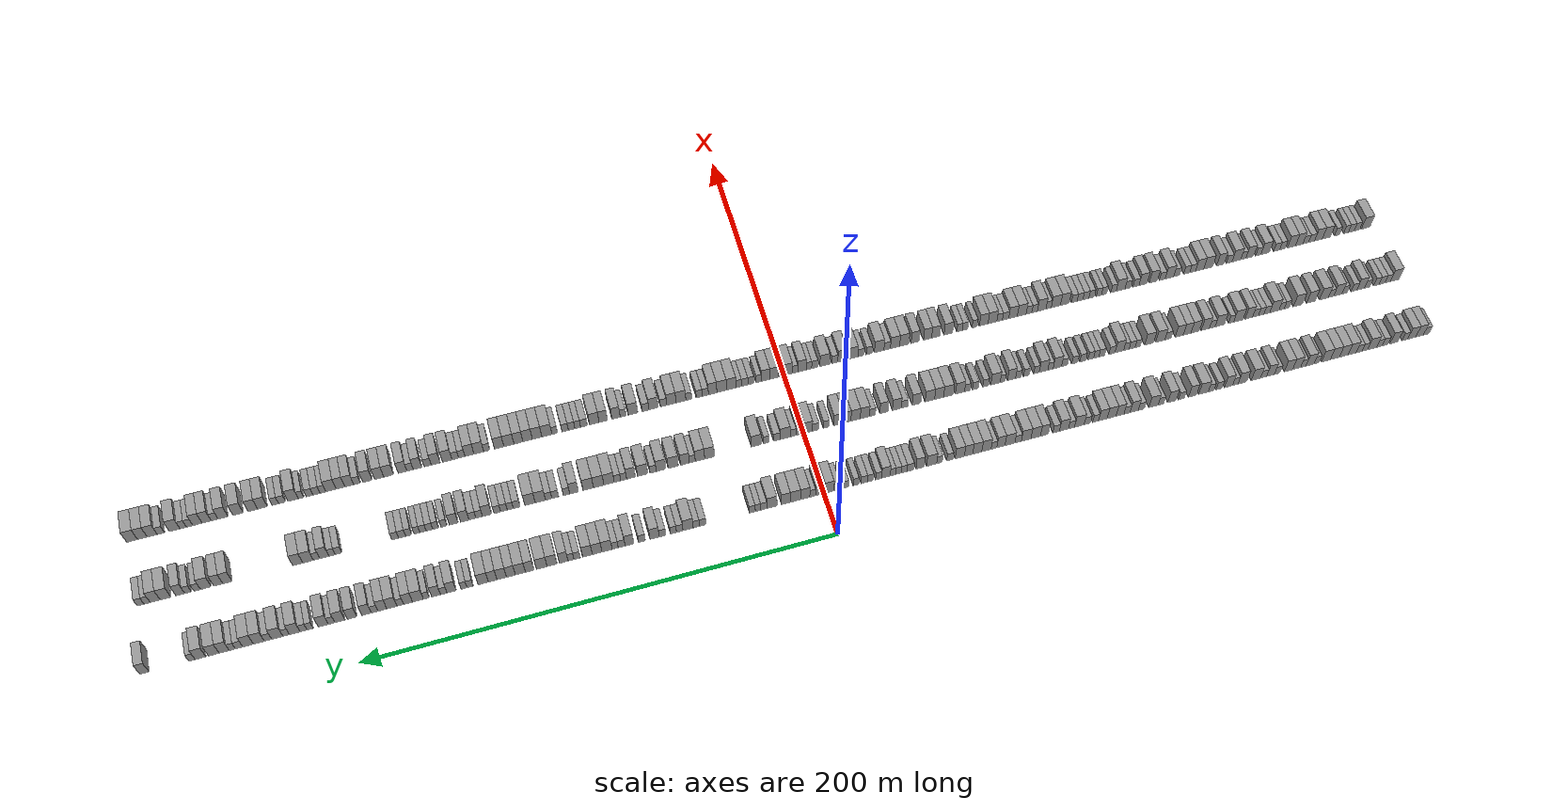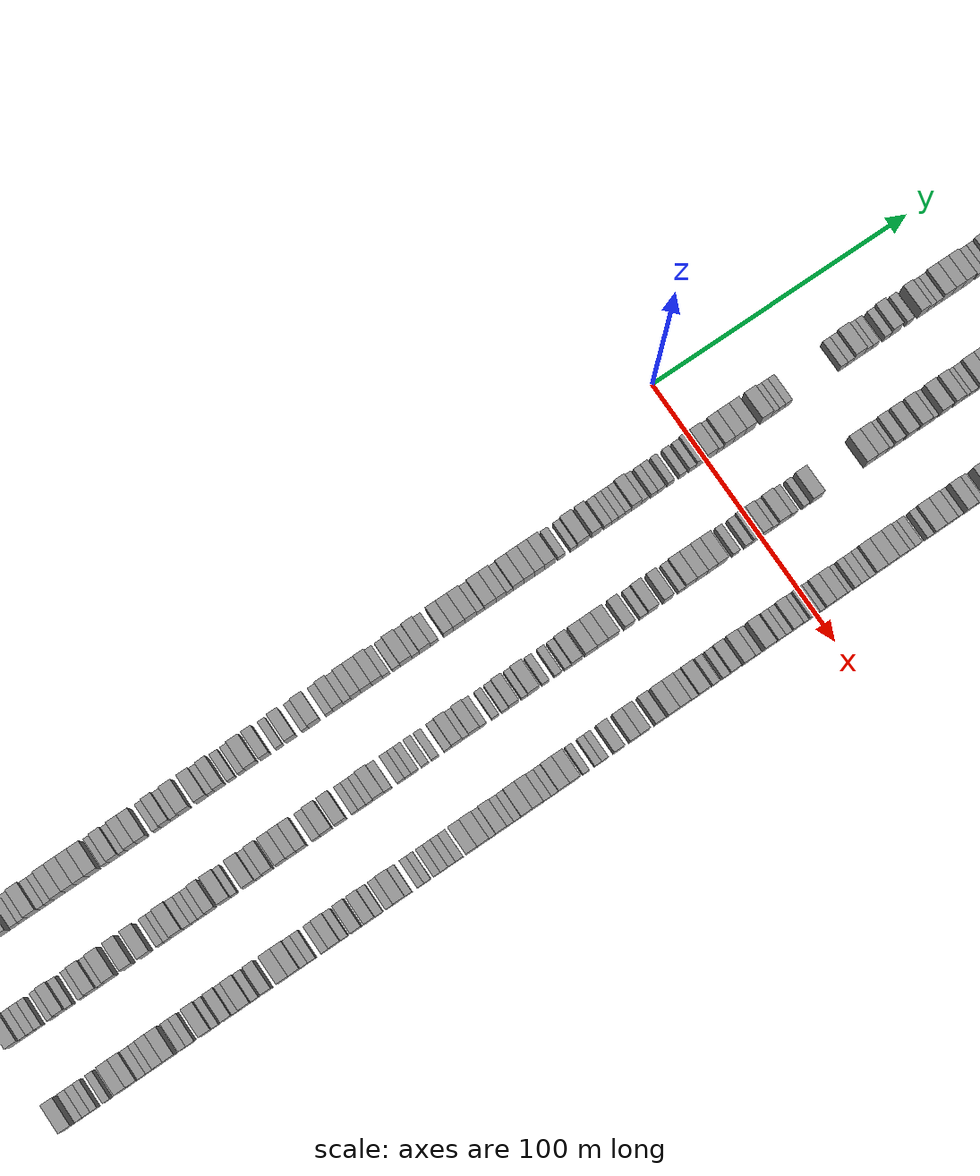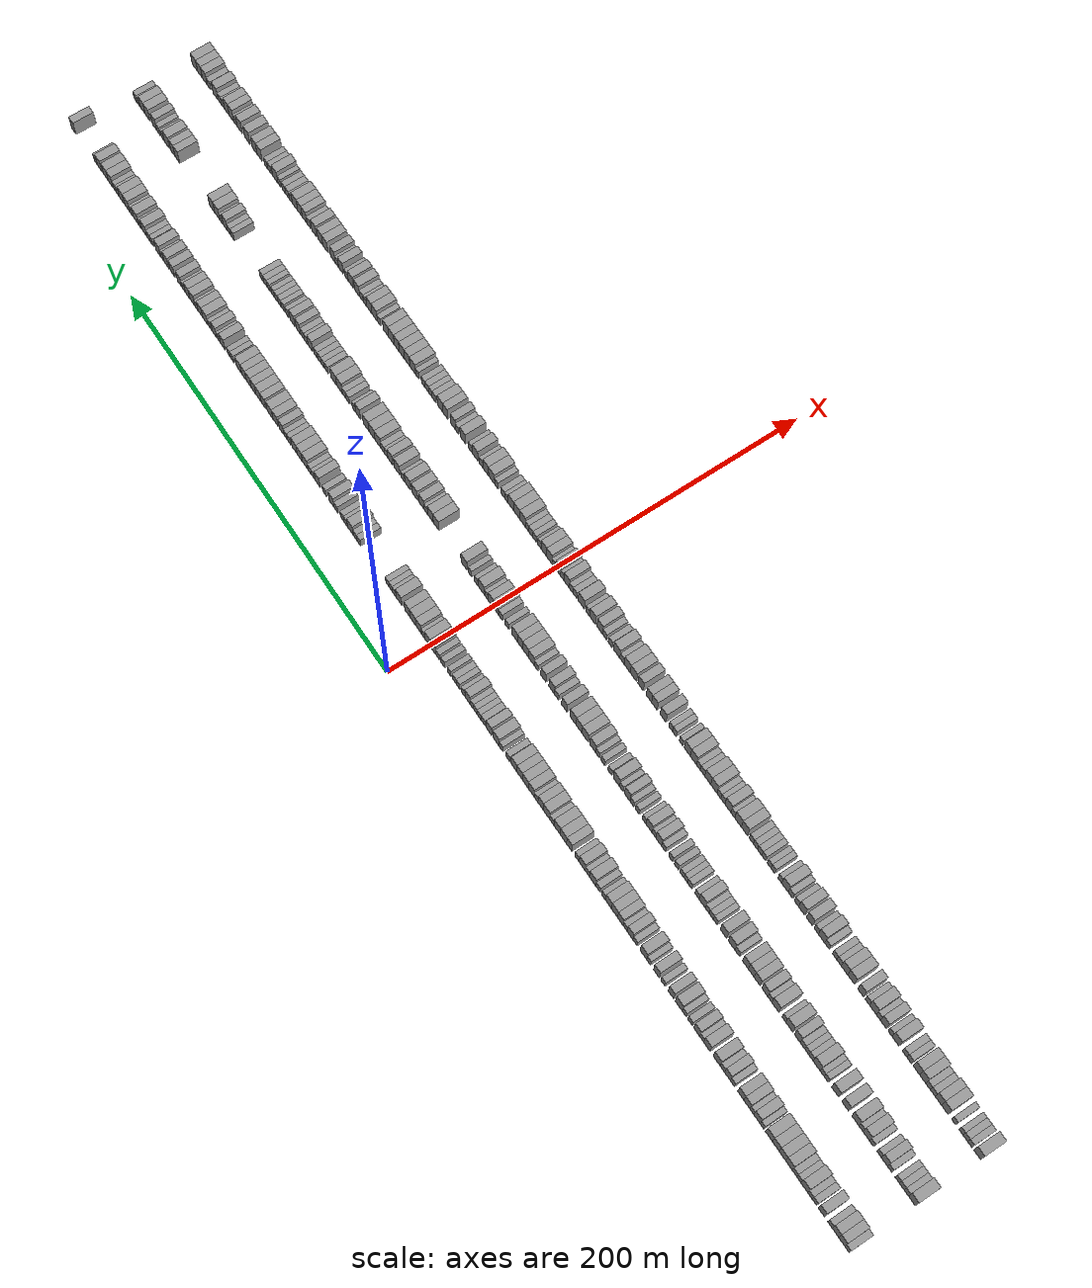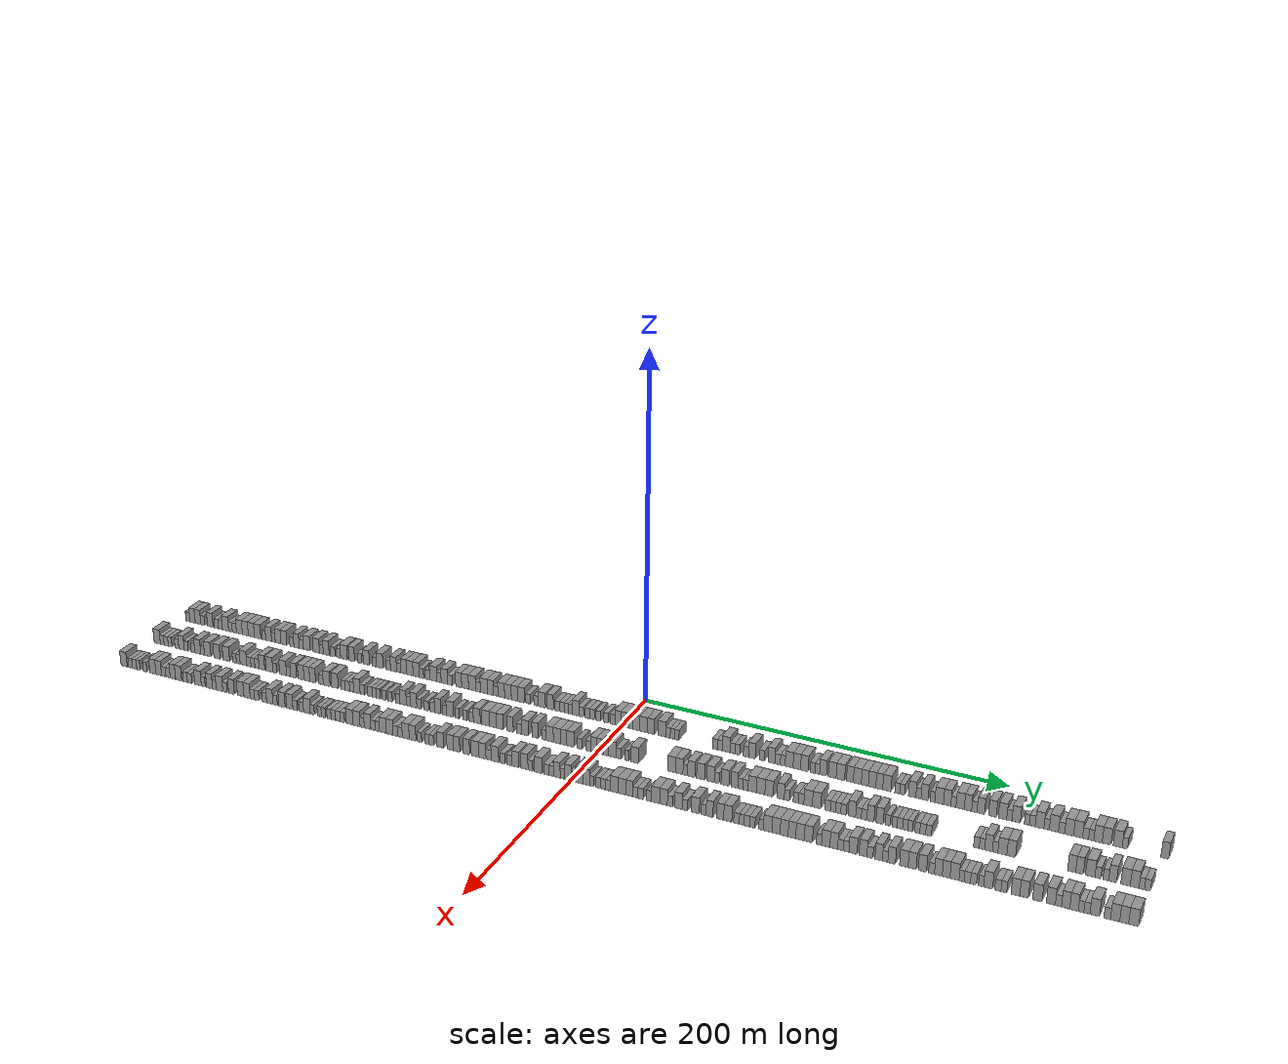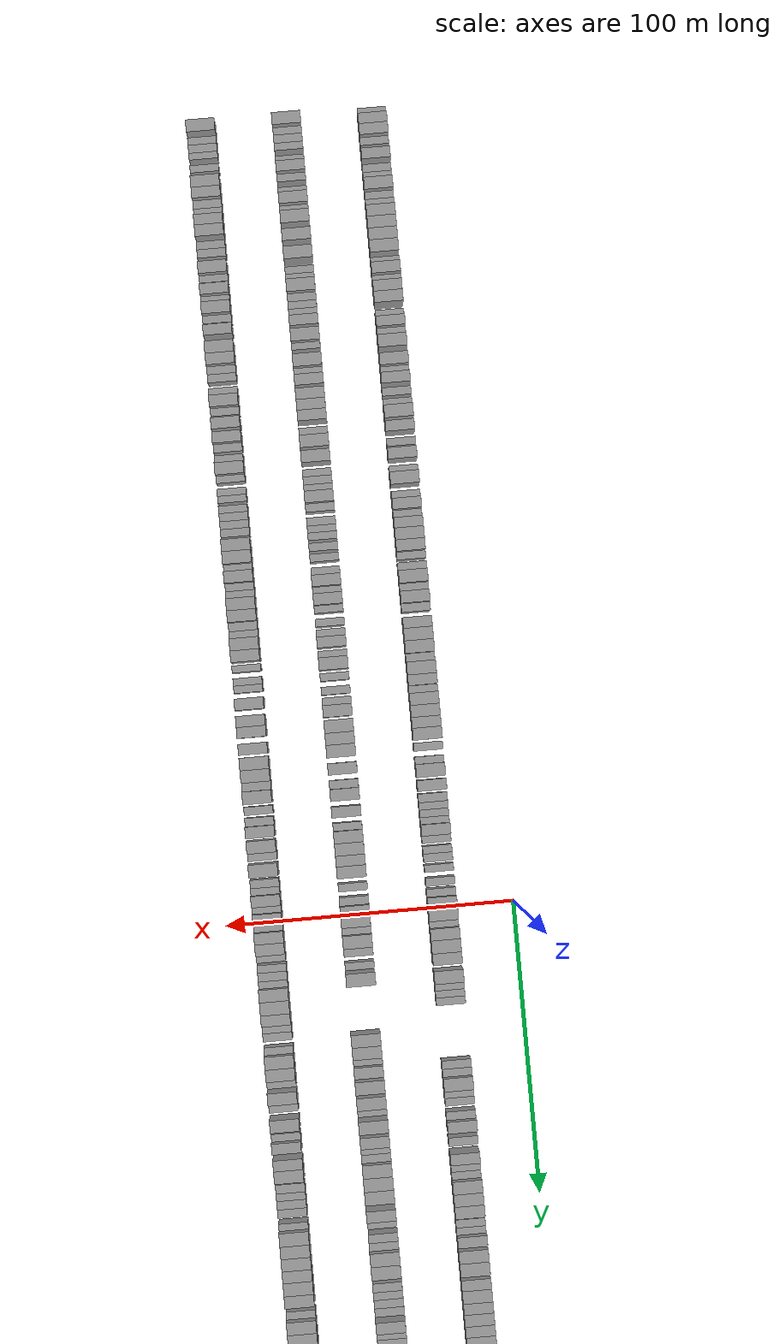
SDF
<sdf version="1.6">
 <world name="default">
  <scene>
   <sky><clouds><speed>12</speed></clouds></sky>
   <ambient>0.4 0.4 0.4 1</ambient>
   <background>0.7 0.7 0.7 1</background>
   <shadows>1</shadows>
  </scene>
  <gravity>0 0 -9.8066</gravity>
  <magnetic_field>6e-06 2.3e-05 -4.2e-05</magnetic_field>
  <physics default="0" name="default_physics" type="ode">
   <ode>
    <solver>
     <type>quick</type>
     <iters>10</iters>
     <sor>1.0</sor>
     <use_dynamic_moi_rescaling>0</use_dynamic_moi_rescaling>
    </solver>
    <constraints>
     <cfm>0</cfm>
     <erp>0.2</erp>
     <contact_max_correcting_vel>100</contact_max_correcting_vel>
     <contact_surface_layer>0.001</contact_surface_layer>
    </constraints>
   </ode>
   <max_step_size>0.004</max_step_size>
   <real_time_factor>1</real_time_factor>
   <real_time_update_rate>250</real_time_update_rate>
  </physics>
  <light name="sun" type="directional">
   <pose>0 0 10 0 0 0</pose>
   <diffuse>0.8 0.8 0.8 1</diffuse>
   <specular>0.2 0.2 0.2 1</specular>
   <attenuation>
    <range>1000</range>
    <constant>0.9</constant>
    <linear>0.01</linear>
    <quadratic>0.001</quadratic>
   </attenuation>
   <direction>-0.5 0.1 -0.9</direction>
  </light>
  <model name="building_1">
   <static>1</static>
   <pose>25.0000 -278.6009 0 0.000000 0.000000 0.000000</pose>
   <link name="link">
    <pose>0 0 3.00 0 0 0</pose>
    <collision name="collision"><geometry><box><size>10.0000 2.7981 6.0000</size></box></geometry></collision>
    <visual name="visual">
     <cast_shadows>0</cast_shadows>
     <geometry><box><size>10.0000 2.7981 6.0000</size></box></geometry>
     <material>
      <script>
       <uri>model://grey_wall/materials/scripts</uri>
       <uri>model://grey_wall/materials/textures</uri>
       <name>vrc/grey_wall</name>
      </script>
     </material>
    </visual>
   </link>
  </model>
  <model name="building_2">
   <static>1</static>
   <pose>25.0000 -275.3410 0 0.000000 0.000000 0.000000</pose>
   <link name="link">
    <pose>0 0 4.50 0 0 0</pose>
    <collision name="collision"><geometry><box><size>10.0000 3.7218 9.0000</size></box></geometry></collision>
    <visual name="visual">
     <cast_shadows>0</cast_shadows>
     <geometry><box><size>10.0000 3.7218 9.0000</size></box></geometry>
     <material>
      <script>
       <uri>model://grey_wall/materials/scripts</uri>
       <uri>model://grey_wall/materials/textures</uri>
       <name>vrc/grey_wall</name>
      </script>
     </material>
    </visual>
   </link>
  </model>
  <model name="building_3">
   <static>1</static>
   <pose>25.0000 -271.5266 0 0.000000 0.000000 0.000000</pose>
   <link name="link">
    <pose>0 0 4.50 0 0 0</pose>
    <collision name="collision"><geometry><box><size>10.0000 3.9069 9.0000</size></box></geometry></collision>
    <visual name="visual">
     <cast_shadows>0</cast_shadows>
     <geometry><box><size>10.0000 3.9069 9.0000</size></box></geometry>
     <material>
      <script>
       <uri>model://grey_wall/materials/scripts</uri>
       <uri>model://grey_wall/materials/textures</uri>
       <name>vrc/grey_wall</name>
      </script>
     </material>
    </visual>
   </link>
  </model>
  <model name="building_4">
   <static>1</static>
   <pose>25.0000 -268.1847 0 0.000000 0.000000 0.000000</pose>
   <link name="link">
    <pose>0 0 3.00 0 0 0</pose>
    <collision name="collision"><geometry><box><size>10.0000 2.7768 6.0000</size></box></geometry></collision>
    <visual name="visual">
     <cast_shadows>0</cast_shadows>
     <geometry><box><size>10.0000 2.7768 6.0000</size></box></geometry>
     <material>
      <script>
       <uri>model://grey_wall/materials/scripts</uri>
       <uri>model://grey_wall/materials/textures</uri>
       <name>vrc/grey_wall</name>
      </script>
     </material>
    </visual>
   </link>
  </model>
  <model name="building_5">
   <static>1</static>
   <pose>25.0000 -262.8816 0 0.000000 0.000000 0.000000</pose>
   <link name="link">
    <pose>0 0 4.50 0 0 0</pose>
    <collision name="collision"><geometry><box><size>10.0000 3.8293 9.0000</size></box></geometry></collision>
    <visual name="visual">
     <cast_shadows>0</cast_shadows>
     <geometry><box><size>10.0000 3.8293 9.0000</size></box></geometry>
     <material>
      <script>
       <uri>model://grey_wall/materials/scripts</uri>
       <uri>model://grey_wall/materials/textures</uri>
       <name>vrc/grey_wall</name>
      </script>
     </material>
    </visual>
   </link>
  </model>
  <model name="building_6">
   <static>1</static>
   <pose>25.0000 -258.5725 0 0.000000 0.000000 0.000000</pose>
   <link name="link">
    <pose>0 0 3.00 0 0 0</pose>
    <collision name="collision"><geometry><box><size>10.0000 2.7889 6.0000</size></box></geometry></collision>
    <visual name="visual">
     <cast_shadows>0</cast_shadows>
     <geometry><box><size>10.0000 2.7889 6.0000</size></box></geometry>
     <material>
      <script>
       <uri>model://grey_wall/materials/scripts</uri>
       <uri>model://grey_wall/materials/textures</uri>
       <name>vrc/grey_wall</name>
      </script>
     </material>
    </visual>
   </link>
  </model>
  <model name="building_7">
   <static>1</static>
   <pose>25.0000 -255.8251 0 0.000000 0.000000 0.000000</pose>
   <link name="link">
    <pose>0 0 3.00 0 0 0</pose>
    <collision name="collision"><geometry><box><size>10.0000 2.7058 6.0000</size></box></geometry></collision>
    <visual name="visual">
     <cast_shadows>0</cast_shadows>
     <geometry><box><size>10.0000 2.7058 6.0000</size></box></geometry>
     <material>
      <script>
       <uri>model://grey_wall/materials/scripts</uri>
       <uri>model://grey_wall/materials/textures</uri>
       <name>vrc/grey_wall</name>
      </script>
     </material>
    </visual>
   </link>
  </model>
  <model name="building_8">
   <static>1</static>
   <pose>25.0000 -252.3370 0 0.000000 0.000000 0.000000</pose>
   <link name="link">
    <pose>0 0 4.50 0 0 0</pose>
    <collision name="collision"><geometry><box><size>10.0000 4.2704 9.0000</size></box></geometry></collision>
    <visual name="visual">
     <cast_shadows>0</cast_shadows>
     <geometry><box><size>10.0000 4.2704 9.0000</size></box></geometry>
     <material>
      <script>
       <uri>model://grey_wall/materials/scripts</uri>
       <uri>model://grey_wall/materials/textures</uri>
       <name>vrc/grey_wall</name>
      </script>
     </material>
    </visual>
   </link>
  </model>
  <model name="building_9">
   <static>1</static>
   <pose>25.0000 -248.8935 0 0.000000 0.000000 0.000000</pose>
   <link name="link">
    <pose>0 0 3.00 0 0 0</pose>
    <collision name="collision"><geometry><box><size>10.0000 2.6167 6.0000</size></box></geometry></collision>
    <visual name="visual">
     <cast_shadows>0</cast_shadows>
     <geometry><box><size>10.0000 2.6167 6.0000</size></box></geometry>
     <material>
      <script>
       <uri>model://grey_wall/materials/scripts</uri>
       <uri>model://grey_wall/materials/textures</uri>
       <name>vrc/grey_wall</name>
      </script>
     </material>
    </visual>
   </link>
  </model>
  <model name="building_10">
   <static>1</static>
   <pose>25.0000 -246.1637 0 0.000000 0.000000 0.000000</pose>
   <link name="link">
    <pose>0 0 3.00 0 0 0</pose>
    <collision name="collision"><geometry><box><size>10.0000 2.8430 6.0000</size></box></geometry></collision>
    <visual name="visual">
     <cast_shadows>0</cast_shadows>
     <geometry><box><size>10.0000 2.8430 6.0000</size></box></geometry>
     <material>
      <script>
       <uri>model://grey_wall/materials/scripts</uri>
       <uri>model://grey_wall/materials/textures</uri>
       <name>vrc/grey_wall</name>
      </script>
     </material>
    </visual>
   </link>
  </model>
  <model name="building_11">
   <static>1</static>
   <pose>25.0000 -242.7154 0 0.000000 0.000000 0.000000</pose>
   <link name="link">
    <pose>0 0 4.50 0 0 0</pose>
    <collision name="collision"><geometry><box><size>10.0000 4.0534 9.0000</size></box></geometry></collision>
    <visual name="visual">
     <cast_shadows>0</cast_shadows>
     <geometry><box><size>10.0000 4.0534 9.0000</size></box></geometry>
     <material>
      <script>
       <uri>model://grey_wall/materials/scripts</uri>
       <uri>model://grey_wall/materials/textures</uri>
       <name>vrc/grey_wall</name>
      </script>
     </material>
    </visual>
   </link>
  </model>
  <model name="building_12">
   <static>1</static>
   <pose>25.0000 -238.6042 0 0.000000 0.000000 0.000000</pose>
   <link name="link">
    <pose>0 0 4.50 0 0 0</pose>
    <collision name="collision"><geometry><box><size>10.0000 4.1691 9.0000</size></box></geometry></collision>
    <visual name="visual">
     <cast_shadows>0</cast_shadows>
     <geometry><box><size>10.0000 4.1691 9.0000</size></box></geometry>
     <material>
      <script>
       <uri>model://grey_wall/materials/scripts</uri>
       <uri>model://grey_wall/materials/textures</uri>
       <name>vrc/grey_wall</name>
      </script>
     </material>
    </visual>
   </link>
  </model>
  <model name="building_13">
   <static>1</static>
   <pose>25.0000 -234.4380 0 0.000000 0.000000 0.000000</pose>
   <link name="link">
    <pose>0 0 4.50 0 0 0</pose>
    <collision name="collision"><geometry><box><size>10.0000 4.1633 9.0000</size></box></geometry></collision>
    <visual name="visual">
     <cast_shadows>0</cast_shadows>
     <geometry><box><size>10.0000 4.1633 9.0000</size></box></geometry>
     <material>
      <script>
       <uri>model://grey_wall/materials/scripts</uri>
       <uri>model://grey_wall/materials/textures</uri>
       <name>vrc/grey_wall</name>
      </script>
     </material>
    </visual>
   </link>
  </model>
  <model name="building_14">
   <static>1</static>
   <pose>25.0000 -230.1711 0 0.000000 0.000000 0.000000</pose>
   <link name="link">
    <pose>0 0 4.50 0 0 0</pose>
    <collision name="collision"><geometry><box><size>10.0000 4.3705 9.0000</size></box></geometry></collision>
    <visual name="visual">
     <cast_shadows>0</cast_shadows>
     <geometry><box><size>10.0000 4.3705 9.0000</size></box></geometry>
     <material>
      <script>
       <uri>model://grey_wall/materials/scripts</uri>
       <uri>model://grey_wall/materials/textures</uri>
       <name>vrc/grey_wall</name>
      </script>
     </material>
    </visual>
   </link>
  </model>
  <model name="building_15">
   <static>1</static>
   <pose>25.0000 -225.7788 0 0.000000 0.000000 0.000000</pose>
   <link name="link">
    <pose>0 0 3.00 0 0 0</pose>
    <collision name="collision"><geometry><box><size>10.0000 2.4141 6.0000</size></box></geometry></collision>
    <visual name="visual">
     <cast_shadows>0</cast_shadows>
     <geometry><box><size>10.0000 2.4141 6.0000</size></box></geometry>
     <material>
      <script>
       <uri>model://grey_wall/materials/scripts</uri>
       <uri>model://grey_wall/materials/textures</uri>
       <name>vrc/grey_wall</name>
      </script>
     </material>
    </visual>
   </link>
  </model>
  <model name="building_16">
   <static>1</static>
   <pose>25.0000 -222.5971 0 0.000000 0.000000 0.000000</pose>
   <link name="link">
    <pose>0 0 4.50 0 0 0</pose>
    <collision name="collision"><geometry><box><size>10.0000 3.9493 9.0000</size></box></geometry></collision>
    <visual name="visual">
     <cast_shadows>0</cast_shadows>
     <geometry><box><size>10.0000 3.9493 9.0000</size></box></geometry>
     <material>
      <script>
       <uri>model://grey_wall/materials/scripts</uri>
       <uri>model://grey_wall/materials/textures</uri>
       <name>vrc/grey_wall</name>
      </script>
     </material>
    </visual>
   </link>
  </model>
  <model name="building_17">
   <static>1</static>
   <pose>25.0000 -219.3799 0 0.000000 0.000000 0.000000</pose>
   <link name="link">
    <pose>0 0 3.00 0 0 0</pose>
    <collision name="collision"><geometry><box><size>10.0000 2.4851 6.0000</size></box></geometry></collision>
    <visual name="visual">
     <cast_shadows>0</cast_shadows>
     <geometry><box><size>10.0000 2.4851 6.0000</size></box></geometry>
     <material>
      <script>
       <uri>model://grey_wall/materials/scripts</uri>
       <uri>model://grey_wall/materials/textures</uri>
       <name>vrc/grey_wall</name>
      </script>
     </material>
    </visual>
   </link>
  </model>
  <model name="building_18">
   <static>1</static>
   <pose>25.0000 -216.2177 0 0.000000 0.000000 0.000000</pose>
   <link name="link">
    <pose>0 0 4.50 0 0 0</pose>
    <collision name="collision"><geometry><box><size>10.0000 3.8392 9.0000</size></box></geometry></collision>
    <visual name="visual">
     <cast_shadows>0</cast_shadows>
     <geometry><box><size>10.0000 3.8392 9.0000</size></box></geometry>
     <material>
      <script>
       <uri>model://grey_wall/materials/scripts</uri>
       <uri>model://grey_wall/materials/textures</uri>
       <name>vrc/grey_wall</name>
      </script>
     </material>
    </visual>
   </link>
  </model>
  <model name="building_19">
   <static>1</static>
   <pose>25.0000 -212.3028 0 0.000000 0.000000 0.000000</pose>
   <link name="link">
    <pose>0 0 4.50 0 0 0</pose>
    <collision name="collision"><geometry><box><size>10.0000 3.9905 9.0000</size></box></geometry></collision>
    <visual name="visual">
     <cast_shadows>0</cast_shadows>
     <geometry><box><size>10.0000 3.9905 9.0000</size></box></geometry>
     <material>
      <script>
       <uri>model://grey_wall/materials/scripts</uri>
       <uri>model://grey_wall/materials/textures</uri>
       <name>vrc/grey_wall</name>
      </script>
     </material>
    </visual>
   </link>
  </model>
  <model name="building_20">
   <static>1</static>
   <pose>25.0000 -206.9433 0 0.000000 0.000000 0.000000</pose>
   <link name="link">
    <pose>0 0 3.00 0 0 0</pose>
    <collision name="collision"><geometry><box><size>10.0000 2.7284 6.0000</size></box></geometry></collision>
    <visual name="visual">
     <cast_shadows>0</cast_shadows>
     <geometry><box><size>10.0000 2.7284 6.0000</size></box></geometry>
     <material>
      <script>
       <uri>model://grey_wall/materials/scripts</uri>
       <uri>model://grey_wall/materials/textures</uri>
       <name>vrc/grey_wall</name>
      </script>
     </material>
    </visual>
   </link>
  </model>
  <model name="building_21">
   <static>1</static>
   <pose>25.0000 -203.7636 0 0.000000 0.000000 0.000000</pose>
   <link name="link">
    <pose>0 0 4.50 0 0 0</pose>
    <collision name="collision"><geometry><box><size>10.0000 3.6311 9.0000</size></box></geometry></collision>
    <visual name="visual">
     <cast_shadows>0</cast_shadows>
     <geometry><box><size>10.0000 3.6311 9.0000</size></box></geometry>
     <material>
      <script>
       <uri>model://grey_wall/materials/scripts</uri>
       <uri>model://grey_wall/materials/textures</uri>
       <name>vrc/grey_wall</name>
      </script>
     </material>
    </visual>
   </link>
  </model>
  <model name="building_22">
   <static>1</static>
   <pose>25.0000 -200.5274 0 0.000000 0.000000 0.000000</pose>
   <link name="link">
    <pose>0 0 3.00 0 0 0</pose>
    <collision name="collision"><geometry><box><size>10.0000 2.8412 6.0000</size></box></geometry></collision>
    <visual name="visual">
     <cast_shadows>0</cast_shadows>
     <geometry><box><size>10.0000 2.8412 6.0000</size></box></geometry>
     <material>
      <script>
       <uri>model://grey_wall/materials/scripts</uri>
       <uri>model://grey_wall/materials/textures</uri>
       <name>vrc/grey_wall</name>
      </script>
     </material>
    </visual>
   </link>
  </model>
  <model name="building_23">
   <static>1</static>
   <pose>25.0000 -196.8837 0 0.000000 0.000000 0.000000</pose>
   <link name="link">
    <pose>0 0 4.50 0 0 0</pose>
    <collision name="collision"><geometry><box><size>10.0000 4.4463 9.0000</size></box></geometry></collision>
    <visual name="visual">
     <cast_shadows>0</cast_shadows>
     <geometry><box><size>10.0000 4.4463 9.0000</size></box></geometry>
     <material>
      <script>
       <uri>model://grey_wall/materials/scripts</uri>
       <uri>model://grey_wall/materials/textures</uri>
       <name>vrc/grey_wall</name>
      </script>
     </material>
    </visual>
   </link>
  </model>
  <model name="building_24">
   <static>1</static>
   <pose>25.0000 -190.5436 0 0.000000 0.000000 0.000000</pose>
   <link name="link">
    <pose>0 0 4.50 0 0 0</pose>
    <collision name="collision"><geometry><box><size>10.0000 4.2340 9.0000</size></box></geometry></collision>
    <visual name="visual">
     <cast_shadows>0</cast_shadows>
     <geometry><box><size>10.0000 4.2340 9.0000</size></box></geometry>
     <material>
      <script>
       <uri>model://grey_wall/materials/scripts</uri>
       <uri>model://grey_wall/materials/textures</uri>
       <name>vrc/grey_wall</name>
      </script>
     </material>
    </visual>
   </link>
  </model>
  <model name="building_25">
   <static>1</static>
   <pose>25.0000 -187.1409 0 0.000000 0.000000 0.000000</pose>
   <link name="link">
    <pose>0 0 3.00 0 0 0</pose>
    <collision name="collision"><geometry><box><size>10.0000 2.5713 6.0000</size></box></geometry></collision>
    <visual name="visual">
     <cast_shadows>0</cast_shadows>
     <geometry><box><size>10.0000 2.5713 6.0000</size></box></geometry>
     <material>
      <script>
       <uri>model://grey_wall/materials/scripts</uri>
       <uri>model://grey_wall/materials/textures</uri>
       <name>vrc/grey_wall</name>
      </script>
     </material>
    </visual>
   </link>
  </model>
  <model name="building_26">
   <static>1</static>
   <pose>25.0000 -183.9391 0 0.000000 0.000000 0.000000</pose>
   <link name="link">
    <pose>0 0 4.50 0 0 0</pose>
    <collision name="collision"><geometry><box><size>10.0000 3.8322 9.0000</size></box></geometry></collision>
    <visual name="visual">
     <cast_shadows>0</cast_shadows>
     <geometry><box><size>10.0000 3.8322 9.0000</size></box></geometry>
     <material>
      <script>
       <uri>model://grey_wall/materials/scripts</uri>
       <uri>model://grey_wall/materials/textures</uri>
       <name>vrc/grey_wall</name>
      </script>
     </material>
    </visual>
   </link>
  </model>
  <model name="building_27">
   <static>1</static>
   <pose>25.0000 -179.5580 0 0.000000 0.000000 0.000000</pose>
   <link name="link">
    <pose>0 0 3.00 0 0 0</pose>
    <collision name="collision"><geometry><box><size>10.0000 2.9300 6.0000</size></box></geometry></collision>
    <visual name="visual">
     <cast_shadows>0</cast_shadows>
     <geometry><box><size>10.0000 2.9300 6.0000</size></box></geometry>
     <material>
      <script>
       <uri>model://grey_wall/materials/scripts</uri>
       <uri>model://grey_wall/materials/textures</uri>
       <name>vrc/grey_wall</name>
      </script>
     </material>
    </visual>
   </link>
  </model>
  <model name="building_28">
   <static>1</static>
   <pose>25.0000 -175.7674 0 0.000000 0.000000 0.000000</pose>
   <link name="link">
    <pose>0 0 3.00 0 0 0</pose>
    <collision name="collision"><geometry><box><size>10.0000 2.6513 6.0000</size></box></geometry></collision>
    <visual name="visual">
     <cast_shadows>0</cast_shadows>
     <geometry><box><size>10.0000 2.6513 6.0000</size></box></geometry>
     <material>
      <script>
       <uri>model://grey_wall/materials/scripts</uri>
       <uri>model://grey_wall/materials/textures</uri>
       <name>vrc/grey_wall</name>
      </script>
     </material>
    </visual>
   </link>
  </model>
  <model name="building_29">
   <static>1</static>
   <pose>25.0000 -172.1973 0 0.000000 0.000000 0.000000</pose>
   <link name="link">
    <pose>0 0 4.50 0 0 0</pose>
    <collision name="collision"><geometry><box><size>10.0000 4.4889 9.0000</size></box></geometry></collision>
    <visual name="visual">
     <cast_shadows>0</cast_shadows>
     <geometry><box><size>10.0000 4.4889 9.0000</size></box></geometry>
     <material>
      <script>
       <uri>model://grey_wall/materials/scripts</uri>
       <uri>model://grey_wall/materials/textures</uri>
       <name>vrc/grey_wall</name>
      </script>
     </material>
    </visual>
   </link>
  </model>
  <model name="building_30">
   <static>1</static>
   <pose>25.0000 -167.0907 0 0.000000 0.000000 0.000000</pose>
   <link name="link">
    <pose>0 0 4.50 0 0 0</pose>
    <collision name="collision"><geometry><box><size>10.0000 3.7242 9.0000</size></box></geometry></collision>
    <visual name="visual">
     <cast_shadows>0</cast_shadows>
     <geometry><box><size>10.0000 3.7242 9.0000</size></box></geometry>
     <material>
      <script>
       <uri>model://grey_wall/materials/scripts</uri>
       <uri>model://grey_wall/materials/textures</uri>
       <name>vrc/grey_wall</name>
      </script>
     </material>
    </visual>
   </link>
  </model>
  <model name="building_31">
   <static>1</static>
   <pose>25.0000 -161.8653 0 0.000000 0.000000 0.000000</pose>
   <link name="link">
    <pose>0 0 3.00 0 0 0</pose>
    <collision name="collision"><geometry><box><size>10.0000 2.7267 6.0000</size></box></geometry></collision>
    <visual name="visual">
     <cast_shadows>0</cast_shadows>
     <geometry><box><size>10.0000 2.7267 6.0000</size></box></geometry>
     <material>
      <script>
       <uri>model://grey_wall/materials/scripts</uri>
       <uri>model://grey_wall/materials/textures</uri>
       <name>vrc/grey_wall</name>
      </script>
     </material>
    </visual>
   </link>
  </model>
  <model name="building_32">
   <static>1</static>
   <pose>25.0000 -157.5328 0 0.000000 0.000000 0.000000</pose>
   <link name="link">
    <pose>0 0 4.50 0 0 0</pose>
    <collision name="collision"><geometry><box><size>10.0000 3.9383 9.0000</size></box></geometry></collision>
    <visual name="visual">
     <cast_shadows>0</cast_shadows>
     <geometry><box><size>10.0000 3.9383 9.0000</size></box></geometry>
     <material>
      <script>
       <uri>model://grey_wall/materials/scripts</uri>
       <uri>model://grey_wall/materials/textures</uri>
       <name>vrc/grey_wall</name>
      </script>
     </material>
    </visual>
   </link>
  </model>
  <model name="building_33">
   <static>1</static>
   <pose>25.0000 -152.3261 0 0.000000 0.000000 0.000000</pose>
   <link name="link">
    <pose>0 0 3.00 0 0 0</pose>
    <collision name="collision"><geometry><box><size>10.0000 2.4749 6.0000</size></box></geometry></collision>
    <visual name="visual">
     <cast_shadows>0</cast_shadows>
     <geometry><box><size>10.0000 2.4749 6.0000</size></box></geometry>
     <material>
      <script>
       <uri>model://grey_wall/materials/scripts</uri>
       <uri>model://grey_wall/materials/textures</uri>
       <name>vrc/grey_wall</name>
      </script>
     </material>
    </visual>
   </link>
  </model>
  <model name="building_34">
   <static>1</static>
   <pose>25.0000 -148.9063 0 0.000000 0.000000 0.000000</pose>
   <link name="link">
    <pose>0 0 4.50 0 0 0</pose>
    <collision name="collision"><geometry><box><size>10.0000 4.3647 9.0000</size></box></geometry></collision>
    <visual name="visual">
     <cast_shadows>0</cast_shadows>
     <geometry><box><size>10.0000 4.3647 9.0000</size></box></geometry>
     <material>
      <script>
       <uri>model://grey_wall/materials/scripts</uri>
       <uri>model://grey_wall/materials/textures</uri>
       <name>vrc/grey_wall</name>
      </script>
     </material>
    </visual>
   </link>
  </model>
  <model name="building_35">
   <static>1</static>
   <pose>25.0000 -143.3129 0 0.000000 0.000000 0.000000</pose>
   <link name="link">
    <pose>0 0 3.00 0 0 0</pose>
    <collision name="collision"><geometry><box><size>10.0000 2.8221 6.0000</size></box></geometry></collision>
    <visual name="visual">
     <cast_shadows>0</cast_shadows>
     <geometry><box><size>10.0000 2.8221 6.0000</size></box></geometry>
     <material>
      <script>
       <uri>model://grey_wall/materials/scripts</uri>
       <uri>model://grey_wall/materials/textures</uri>
       <name>vrc/grey_wall</name>
      </script>
     </material>
    </visual>
   </link>
  </model>
  <model name="building_36">
   <static>1</static>
   <pose>25.0000 -139.9711 0 0.000000 0.000000 0.000000</pose>
   <link name="link">
    <pose>0 0 4.50 0 0 0</pose>
    <collision name="collision"><geometry><box><size>10.0000 3.8617 9.0000</size></box></geometry></collision>
    <visual name="visual">
     <cast_shadows>0</cast_shadows>
     <geometry><box><size>10.0000 3.8617 9.0000</size></box></geometry>
     <material>
      <script>
       <uri>model://grey_wall/materials/scripts</uri>
       <uri>model://grey_wall/materials/textures</uri>
       <name>vrc/grey_wall</name>
      </script>
     </material>
    </visual>
   </link>
  </model>
  <model name="building_37">
   <static>1</static>
   <pose>25.0000 -136.6339 0 0.000000 0.000000 0.000000</pose>
   <link name="link">
    <pose>0 0 3.00 0 0 0</pose>
    <collision name="collision"><geometry><box><size>10.0000 2.8127 6.0000</size></box></geometry></collision>
    <visual name="visual">
     <cast_shadows>0</cast_shadows>
     <geometry><box><size>10.0000 2.8127 6.0000</size></box></geometry>
     <material>
      <script>
       <uri>model://grey_wall/materials/scripts</uri>
       <uri>model://grey_wall/materials/textures</uri>
       <name>vrc/grey_wall</name>
      </script>
     </material>
    </visual>
   </link>
  </model>
  <model name="building_38">
   <static>1</static>
   <pose>25.0000 -133.4051 0 0.000000 0.000000 0.000000</pose>
   <link name="link">
    <pose>0 0 4.50 0 0 0</pose>
    <collision name="collision"><geometry><box><size>10.0000 3.6448 9.0000</size></box></geometry></collision>
    <visual name="visual">
     <cast_shadows>0</cast_shadows>
     <geometry><box><size>10.0000 3.6448 9.0000</size></box></geometry>
     <material>
      <script>
       <uri>model://grey_wall/materials/scripts</uri>
       <uri>model://grey_wall/materials/textures</uri>
       <name>vrc/grey_wall</name>
      </script>
     </material>
    </visual>
   </link>
  </model>
  <model name="building_39">
   <static>1</static>
   <pose>25.0000 -129.5176 0 0.000000 0.000000 0.000000</pose>
   <link name="link">
    <pose>0 0 4.50 0 0 0</pose>
    <collision name="collision"><geometry><box><size>10.0000 4.1303 9.0000</size></box></geometry></collision>
    <visual name="visual">
     <cast_shadows>0</cast_shadows>
     <geometry><box><size>10.0000 4.1303 9.0000</size></box></geometry>
     <material>
      <script>
       <uri>model://grey_wall/materials/scripts</uri>
       <uri>model://grey_wall/materials/textures</uri>
       <name>vrc/grey_wall</name>
      </script>
     </material>
    </visual>
   </link>
  </model>
  <model name="building_40">
   <static>1</static>
   <pose>25.0000 -125.4707 0 0.000000 0.000000 0.000000</pose>
   <link name="link">
    <pose>0 0 4.50 0 0 0</pose>
    <collision name="collision"><geometry><box><size>10.0000 3.9636 9.0000</size></box></geometry></collision>
    <visual name="visual">
     <cast_shadows>0</cast_shadows>
     <geometry><box><size>10.0000 3.9636 9.0000</size></box></geometry>
     <material>
      <script>
       <uri>model://grey_wall/materials/scripts</uri>
       <uri>model://grey_wall/materials/textures</uri>
       <name>vrc/grey_wall</name>
      </script>
     </material>
    </visual>
   </link>
  </model>
  <model name="building_41">
   <static>1</static>
   <pose>25.0000 -122.1347 0 0.000000 0.000000 0.000000</pose>
   <link name="link">
    <pose>0 0 3.00 0 0 0</pose>
    <collision name="collision"><geometry><box><size>10.0000 2.7084 6.0000</size></box></geometry></collision>
    <visual name="visual">
     <cast_shadows>0</cast_shadows>
     <geometry><box><size>10.0000 2.7084 6.0000</size></box></geometry>
     <material>
      <script>
       <uri>model://grey_wall/materials/scripts</uri>
       <uri>model://grey_wall/materials/textures</uri>
       <name>vrc/grey_wall</name>
      </script>
     </material>
    </visual>
   </link>
  </model>
  <model name="building_42">
   <static>1</static>
   <pose>25.0000 -118.3318 0 0.000000 0.000000 0.000000</pose>
   <link name="link">
    <pose>0 0 3.00 0 0 0</pose>
    <collision name="collision"><geometry><box><size>10.0000 2.8973 6.0000</size></box></geometry></collision>
    <visual name="visual">
     <cast_shadows>0</cast_shadows>
     <geometry><box><size>10.0000 2.8973 6.0000</size></box></geometry>
     <material>
      <script>
       <uri>model://grey_wall/materials/scripts</uri>
       <uri>model://grey_wall/materials/textures</uri>
       <name>vrc/grey_wall</name>
      </script>
     </material>
    </visual>
   </link>
  </model>
  <model name="building_43">
   <static>1</static>
   <pose>25.0000 -114.6785 0 0.000000 0.000000 0.000000</pose>
   <link name="link">
    <pose>0 0 4.50 0 0 0</pose>
    <collision name="collision"><geometry><box><size>10.0000 4.4093 9.0000</size></box></geometry></collision>
    <visual name="visual">
     <cast_shadows>0</cast_shadows>
     <geometry><box><size>10.0000 4.4093 9.0000</size></box></geometry>
     <material>
      <script>
       <uri>model://grey_wall/materials/scripts</uri>
       <uri>model://grey_wall/materials/textures</uri>
       <name>vrc/grey_wall</name>
      </script>
     </material>
    </visual>
   </link>
  </model>
  <model name="building_44">
   <static>1</static>
   <pose>25.0000 -111.0731 0 0.000000 0.000000 0.000000</pose>
   <link name="link">
    <pose>0 0 3.00 0 0 0</pose>
    <collision name="collision"><geometry><box><size>10.0000 2.8014 6.0000</size></box></geometry></collision>
    <visual name="visual">
     <cast_shadows>0</cast_shadows>
     <geometry><box><size>10.0000 2.8014 6.0000</size></box></geometry>
     <material>
      <script>
       <uri>model://grey_wall/materials/scripts</uri>
       <uri>model://grey_wall/materials/textures</uri>
       <name>vrc/grey_wall</name>
      </script>
     </material>
    </visual>
   </link>
  </model>
  <model name="building_45">
   <static>1</static>
   <pose>25.0000 -107.6007 0 0.000000 0.000000 0.000000</pose>
   <link name="link">
    <pose>0 0 4.50 0 0 0</pose>
    <collision name="collision"><geometry><box><size>10.0000 4.1434 9.0000</size></box></geometry></collision>
    <visual name="visual">
     <cast_shadows>0</cast_shadows>
     <geometry><box><size>10.0000 4.1434 9.0000</size></box></geometry>
     <material>
      <script>
       <uri>model://grey_wall/materials/scripts</uri>
       <uri>model://grey_wall/materials/textures</uri>
       <name>vrc/grey_wall</name>
      </script>
     </material>
    </visual>
   </link>
  </model>
  <model name="building_46">
   <static>1</static>
   <pose>25.0000 -104.0345 0 0.000000 0.000000 0.000000</pose>
   <link name="link">
    <pose>0 0 3.00 0 0 0</pose>
    <collision name="collision"><geometry><box><size>10.0000 2.9891 6.0000</size></box></geometry></collision>
    <visual name="visual">
     <cast_shadows>0</cast_shadows>
     <geometry><box><size>10.0000 2.9891 6.0000</size></box></geometry>
     <material>
      <script>
       <uri>model://grey_wall/materials/scripts</uri>
       <uri>model://grey_wall/materials/textures</uri>
       <name>vrc/grey_wall</name>
      </script>
     </material>
    </visual>
   </link>
  </model>
  <model name="building_47">
   <static>1</static>
   <pose>25.0000 -98.6809 0 0.000000 0.000000 0.000000</pose>
   <link name="link">
    <pose>0 0 4.50 0 0 0</pose>
    <collision name="collision"><geometry><box><size>10.0000 3.7179 9.0000</size></box></geometry></collision>
    <visual name="visual">
     <cast_shadows>0</cast_shadows>
     <geometry><box><size>10.0000 3.7179 9.0000</size></box></geometry>
     <material>
      <script>
       <uri>model://grey_wall/materials/scripts</uri>
       <uri>model://grey_wall/materials/textures</uri>
       <name>vrc/grey_wall</name>
      </script>
     </material>
    </visual>
   </link>
  </model>
  <model name="building_48">
   <static>1</static>
   <pose>25.0000 -94.6709 0 0.000000 0.000000 0.000000</pose>
   <link name="link">
    <pose>0 0 4.50 0 0 0</pose>
    <collision name="collision"><geometry><box><size>10.0000 4.3020 9.0000</size></box></geometry></collision>
    <visual name="visual">
     <cast_shadows>0</cast_shadows>
     <geometry><box><size>10.0000 4.3020 9.0000</size></box></geometry>
     <material>
      <script>
       <uri>model://grey_wall/materials/scripts</uri>
       <uri>model://grey_wall/materials/textures</uri>
       <name>vrc/grey_wall</name>
      </script>
     </material>
    </visual>
   </link>
  </model>
  <model name="building_49">
   <static>1</static>
   <pose>25.0000 -90.3469 0 0.000000 0.000000 0.000000</pose>
   <link name="link">
    <pose>0 0 4.50 0 0 0</pose>
    <collision name="collision"><geometry><box><size>10.0000 4.3460 9.0000</size></box></geometry></collision>
    <visual name="visual">
     <cast_shadows>0</cast_shadows>
     <geometry><box><size>10.0000 4.3460 9.0000</size></box></geometry>
     <material>
      <script>
       <uri>model://grey_wall/materials/scripts</uri>
       <uri>model://grey_wall/materials/textures</uri>
       <name>vrc/grey_wall</name>
      </script>
     </material>
    </visual>
   </link>
  </model>
  <model name="building_50">
   <static>1</static>
   <pose>25.0000 -86.6981 0 0.000000 0.000000 0.000000</pose>
   <link name="link">
    <pose>0 0 3.00 0 0 0</pose>
    <collision name="collision"><geometry><box><size>10.0000 2.9517 6.0000</size></box></geometry></collision>
    <visual name="visual">
     <cast_shadows>0</cast_shadows>
     <geometry><box><size>10.0000 2.9517 6.0000</size></box></geometry>
     <material>
      <script>
       <uri>model://grey_wall/materials/scripts</uri>
       <uri>model://grey_wall/materials/textures</uri>
       <name>vrc/grey_wall</name>
      </script>
     </material>
    </visual>
   </link>
  </model>
  <model name="building_51">
   <static>1</static>
   <pose>25.0000 -82.9940 0 0.000000 0.000000 0.000000</pose>
   <link name="link">
    <pose>0 0 4.50 0 0 0</pose>
    <collision name="collision"><geometry><box><size>10.0000 4.4566 9.0000</size></box></geometry></collision>
    <visual name="visual">
     <cast_shadows>0</cast_shadows>
     <geometry><box><size>10.0000 4.4566 9.0000</size></box></geometry>
     <material>
      <script>
       <uri>model://grey_wall/materials/scripts</uri>
       <uri>model://grey_wall/materials/textures</uri>
       <name>vrc/grey_wall</name>
      </script>
     </material>
    </visual>
   </link>
  </model>
  <model name="building_52">
   <static>1</static>
   <pose>25.0000 -78.9220 0 0.000000 0.000000 0.000000</pose>
   <link name="link">
    <pose>0 0 4.50 0 0 0</pose>
    <collision name="collision"><geometry><box><size>10.0000 3.6874 9.0000</size></box></geometry></collision>
    <visual name="visual">
     <cast_shadows>0</cast_shadows>
     <geometry><box><size>10.0000 3.6874 9.0000</size></box></geometry>
     <material>
      <script>
       <uri>model://grey_wall/materials/scripts</uri>
       <uri>model://grey_wall/materials/textures</uri>
       <name>vrc/grey_wall</name>
      </script>
     </material>
    </visual>
   </link>
  </model>
  <model name="building_53">
   <static>1</static>
   <pose>25.0000 -75.7535 0 0.000000 0.000000 0.000000</pose>
   <link name="link">
    <pose>0 0 3.00 0 0 0</pose>
    <collision name="collision"><geometry><box><size>10.0000 2.6494 6.0000</size></box></geometry></collision>
    <visual name="visual">
     <cast_shadows>0</cast_shadows>
     <geometry><box><size>10.0000 2.6494 6.0000</size></box></geometry>
     <material>
      <script>
       <uri>model://grey_wall/materials/scripts</uri>
       <uri>model://grey_wall/materials/textures</uri>
       <name>vrc/grey_wall</name>
      </script>
     </material>
    </visual>
   </link>
  </model>
  <model name="building_54">
   <static>1</static>
   <pose>25.0000 -72.3578 0 0.000000 0.000000 0.000000</pose>
   <link name="link">
    <pose>0 0 4.50 0 0 0</pose>
    <collision name="collision"><geometry><box><size>10.0000 4.1422 9.0000</size></box></geometry></collision>
    <visual name="visual">
     <cast_shadows>0</cast_shadows>
     <geometry><box><size>10.0000 4.1422 9.0000</size></box></geometry>
     <material>
      <script>
       <uri>model://grey_wall/materials/scripts</uri>
       <uri>model://grey_wall/materials/textures</uri>
       <name>vrc/grey_wall</name>
      </script>
     </material>
    </visual>
   </link>
  </model>
  <model name="building_55">
   <static>1</static>
   <pose>25.0000 -68.2261 0 0.000000 0.000000 0.000000</pose>
   <link name="link">
    <pose>0 0 4.50 0 0 0</pose>
    <collision name="collision"><geometry><box><size>10.0000 4.1212 9.0000</size></box></geometry></collision>
    <visual name="visual">
     <cast_shadows>0</cast_shadows>
     <geometry><box><size>10.0000 4.1212 9.0000</size></box></geometry>
     <material>
      <script>
       <uri>model://grey_wall/materials/scripts</uri>
       <uri>model://grey_wall/materials/textures</uri>
       <name>vrc/grey_wall</name>
      </script>
     </material>
    </visual>
   </link>
  </model>
  <model name="building_56">
   <static>1</static>
   <pose>25.0000 -64.2971 0 0.000000 0.000000 0.000000</pose>
   <link name="link">
    <pose>0 0 4.50 0 0 0</pose>
    <collision name="collision"><geometry><box><size>10.0000 3.7368 9.0000</size></box></geometry></collision>
    <visual name="visual">
     <cast_shadows>0</cast_shadows>
     <geometry><box><size>10.0000 3.7368 9.0000</size></box></geometry>
     <material>
      <script>
       <uri>model://grey_wall/materials/scripts</uri>
       <uri>model://grey_wall/materials/textures</uri>
       <name>vrc/grey_wall</name>
      </script>
     </material>
    </visual>
   </link>
  </model>
  <model name="building_57">
   <static>1</static>
   <pose>25.0000 -60.3658 0 0.000000 0.000000 0.000000</pose>
   <link name="link">
    <pose>0 0 4.50 0 0 0</pose>
    <collision name="collision"><geometry><box><size>10.0000 4.1258 9.0000</size></box></geometry></collision>
    <visual name="visual">
     <cast_shadows>0</cast_shadows>
     <geometry><box><size>10.0000 4.1258 9.0000</size></box></geometry>
     <material>
      <script>
       <uri>model://grey_wall/materials/scripts</uri>
       <uri>model://grey_wall/materials/textures</uri>
       <name>vrc/grey_wall</name>
      </script>
     </material>
    </visual>
   </link>
  </model>
  <model name="building_58">
   <static>1</static>
   <pose>25.0000 -55.9128 0 0.000000 0.000000 0.000000</pose>
   <link name="link">
    <pose>0 0 3.00 0 0 0</pose>
    <collision name="collision"><geometry><box><size>10.0000 2.7802 6.0000</size></box></geometry></collision>
    <visual name="visual">
     <cast_shadows>0</cast_shadows>
     <geometry><box><size>10.0000 2.7802 6.0000</size></box></geometry>
     <material>
      <script>
       <uri>model://grey_wall/materials/scripts</uri>
       <uri>model://grey_wall/materials/textures</uri>
       <name>vrc/grey_wall</name>
      </script>
     </material>
    </visual>
   </link>
  </model>
  <model name="building_59">
   <static>1</static>
   <pose>25.0000 -51.2507 0 0.000000 0.000000 0.000000</pose>
   <link name="link">
    <pose>0 0 3.00 0 0 0</pose>
    <collision name="collision"><geometry><box><size>10.0000 2.5441 6.0000</size></box></geometry></collision>
    <visual name="visual">
     <cast_shadows>0</cast_shadows>
     <geometry><box><size>10.0000 2.5441 6.0000</size></box></geometry>
     <material>
      <script>
       <uri>model://grey_wall/materials/scripts</uri>
       <uri>model://grey_wall/materials/textures</uri>
       <name>vrc/grey_wall</name>
      </script>
     </material>
    </visual>
   </link>
  </model>
  <model name="building_60">
   <static>1</static>
   <pose>25.0000 -47.7324 0 0.000000 0.000000 0.000000</pose>
   <link name="link">
    <pose>0 0 4.50 0 0 0</pose>
    <collision name="collision"><geometry><box><size>10.0000 4.4926 9.0000</size></box></geometry></collision>
    <visual name="visual">
     <cast_shadows>0</cast_shadows>
     <geometry><box><size>10.0000 4.4926 9.0000</size></box></geometry>
     <material>
      <script>
       <uri>model://grey_wall/materials/scripts</uri>
       <uri>model://grey_wall/materials/textures</uri>
       <name>vrc/grey_wall</name>
      </script>
     </material>
    </visual>
   </link>
  </model>
  <model name="building_61">
   <static>1</static>
   <pose>25.0000 -42.6167 0 0.000000 0.000000 0.000000</pose>
   <link name="link">
    <pose>0 0 4.50 0 0 0</pose>
    <collision name="collision"><geometry><box><size>10.0000 3.7388 9.0000</size></box></geometry></collision>
    <visual name="visual">
     <cast_shadows>0</cast_shadows>
     <geometry><box><size>10.0000 3.7388 9.0000</size></box></geometry>
     <material>
      <script>
       <uri>model://grey_wall/materials/scripts</uri>
       <uri>model://grey_wall/materials/textures</uri>
       <name>vrc/grey_wall</name>
      </script>
     </material>
    </visual>
   </link>
  </model>
  <model name="building_62">
   <static>1</static>
   <pose>25.0000 -38.2618 0 0.000000 0.000000 0.000000</pose>
   <link name="link">
    <pose>0 0 3.00 0 0 0</pose>
    <collision name="collision"><geometry><box><size>10.0000 2.9709 6.0000</size></box></geometry></collision>
    <visual name="visual">
     <cast_shadows>0</cast_shadows>
     <geometry><box><size>10.0000 2.9709 6.0000</size></box></geometry>
     <material>
      <script>
       <uri>model://grey_wall/materials/scripts</uri>
       <uri>model://grey_wall/materials/textures</uri>
       <name>vrc/grey_wall</name>
      </script>
     </material>
    </visual>
   </link>
  </model>
  <model name="building_63">
   <static>1</static>
   <pose>25.0000 -35.5204 0 0.000000 0.000000 0.000000</pose>
   <link name="link">
    <pose>0 0 3.00 0 0 0</pose>
    <collision name="collision"><geometry><box><size>10.0000 2.5118 6.0000</size></box></geometry></collision>
    <visual name="visual">
     <cast_shadows>0</cast_shadows>
     <geometry><box><size>10.0000 2.5118 6.0000</size></box></geometry>
     <material>
      <script>
       <uri>model://grey_wall/materials/scripts</uri>
       <uri>model://grey_wall/materials/textures</uri>
       <name>vrc/grey_wall</name>
      </script>
     </material>
    </visual>
   </link>
  </model>
  <model name="building_64">
   <static>1</static>
   <pose>25.0000 -32.9837 0 0.000000 0.000000 0.000000</pose>
   <link name="link">
    <pose>0 0 3.00 0 0 0</pose>
    <collision name="collision"><geometry><box><size>10.0000 2.5616 6.0000</size></box></geometry></collision>
    <visual name="visual">
     <cast_shadows>0</cast_shadows>
     <geometry><box><size>10.0000 2.5616 6.0000</size></box></geometry>
     <material>
      <script>
       <uri>model://grey_wall/materials/scripts</uri>
       <uri>model://grey_wall/materials/textures</uri>
       <name>vrc/grey_wall</name>
      </script>
     </material>
    </visual>
   </link>
  </model>
  <model name="building_65">
   <static>1</static>
   <pose>25.0000 -30.4996 0 0.000000 0.000000 0.000000</pose>
   <link name="link">
    <pose>0 0 3.00 0 0 0</pose>
    <collision name="collision"><geometry><box><size>10.0000 2.4065 6.0000</size></box></geometry></collision>
    <visual name="visual">
     <cast_shadows>0</cast_shadows>
     <geometry><box><size>10.0000 2.4065 6.0000</size></box></geometry>
     <material>
      <script>
       <uri>model://grey_wall/materials/scripts</uri>
       <uri>model://grey_wall/materials/textures</uri>
       <name>vrc/grey_wall</name>
      </script>
     </material>
    </visual>
   </link>
  </model>
  <model name="building_66">
   <static>1</static>
   <pose>25.0000 -27.3746 0 0.000000 0.000000 0.000000</pose>
   <link name="link">
    <pose>0 0 4.50 0 0 0</pose>
    <collision name="collision"><geometry><box><size>10.0000 3.8436 9.0000</size></box></geometry></collision>
    <visual name="visual">
     <cast_shadows>0</cast_shadows>
     <geometry><box><size>10.0000 3.8436 9.0000</size></box></geometry>
     <material>
      <script>
       <uri>model://grey_wall/materials/scripts</uri>
       <uri>model://grey_wall/materials/textures</uri>
       <name>vrc/grey_wall</name>
      </script>
     </material>
    </visual>
   </link>
  </model>
  <model name="building_67">
   <static>1</static>
   <pose>25.0000 -24.1192 0 0.000000 0.000000 0.000000</pose>
   <link name="link">
    <pose>0 0 3.00 0 0 0</pose>
    <collision name="collision"><geometry><box><size>10.0000 2.6672 6.0000</size></box></geometry></collision>
    <visual name="visual">
     <cast_shadows>0</cast_shadows>
     <geometry><box><size>10.0000 2.6672 6.0000</size></box></geometry>
     <material>
      <script>
       <uri>model://grey_wall/materials/scripts</uri>
       <uri>model://grey_wall/materials/textures</uri>
       <name>vrc/grey_wall</name>
      </script>
     </material>
    </visual>
   </link>
  </model>
  <model name="building_68">
   <static>1</static>
   <pose>25.0000 -20.4829 0 0.000000 0.000000 0.000000</pose>
   <link name="link">
    <pose>0 0 3.00 0 0 0</pose>
    <collision name="collision"><geometry><box><size>10.0000 2.6054 6.0000</size></box></geometry></collision>
    <visual name="visual">
     <cast_shadows>0</cast_shadows>
     <geometry><box><size>10.0000 2.6054 6.0000</size></box></geometry>
     <material>
      <script>
       <uri>model://grey_wall/materials/scripts</uri>
       <uri>model://grey_wall/materials/textures</uri>
       <name>vrc/grey_wall</name>
      </script>
     </material>
    </visual>
   </link>
  </model>
  <model name="building_69">
   <static>1</static>
   <pose>25.0000 -17.7630 0 0.000000 0.000000 0.000000</pose>
   <link name="link">
    <pose>0 0 3.00 0 0 0</pose>
    <collision name="collision"><geometry><box><size>10.0000 2.8343 6.0000</size></box></geometry></collision>
    <visual name="visual">
     <cast_shadows>0</cast_shadows>
     <geometry><box><size>10.0000 2.8343 6.0000</size></box></geometry>
     <material>
      <script>
       <uri>model://grey_wall/materials/scripts</uri>
       <uri>model://grey_wall/materials/textures</uri>
       <name>vrc/grey_wall</name>
      </script>
     </material>
    </visual>
   </link>
  </model>
  <model name="building_70">
   <static>1</static>
   <pose>25.0000 -14.1140 0 0.000000 0.000000 0.000000</pose>
   <link name="link">
    <pose>0 0 3.00 0 0 0</pose>
    <collision name="collision"><geometry><box><size>10.0000 2.4637 6.0000</size></box></geometry></collision>
    <visual name="visual">
     <cast_shadows>0</cast_shadows>
     <geometry><box><size>10.0000 2.4637 6.0000</size></box></geometry>
     <material>
      <script>
       <uri>model://grey_wall/materials/scripts</uri>
       <uri>model://grey_wall/materials/textures</uri>
       <name>vrc/grey_wall</name>
      </script>
     </material>
    </visual>
   </link>
  </model>
  <model name="building_71">
   <static>1</static>
   <pose>25.0000 -9.4948 0 0.000000 0.000000 0.000000</pose>
   <link name="link">
    <pose>0 0 3.00 0 0 0</pose>
    <collision name="collision"><geometry><box><size>10.0000 2.7748 6.0000</size></box></geometry></collision>
    <visual name="visual">
     <cast_shadows>0</cast_shadows>
     <geometry><box><size>10.0000 2.7748 6.0000</size></box></geometry>
     <material>
      <script>
       <uri>model://grey_wall/materials/scripts</uri>
       <uri>model://grey_wall/materials/textures</uri>
       <name>vrc/grey_wall</name>
      </script>
     </material>
    </visual>
   </link>
  </model>
  <model name="building_72">
   <static>1</static>
   <pose>25.0000 -5.7592 0 0.000000 0.000000 0.000000</pose>
   <link name="link">
    <pose>0 0 3.00 0 0 0</pose>
    <collision name="collision"><geometry><box><size>10.0000 2.6963 6.0000</size></box></geometry></collision>
    <visual name="visual">
     <cast_shadows>0</cast_shadows>
     <geometry><box><size>10.0000 2.6963 6.0000</size></box></geometry>
     <material>
      <script>
       <uri>model://grey_wall/materials/scripts</uri>
       <uri>model://grey_wall/materials/textures</uri>
       <name>vrc/grey_wall</name>
      </script>
     </material>
    </visual>
   </link>
  </model>
  <model name="building_73">
   <static>1</static>
   <pose>25.0000 -2.4676 0 0.000000 0.000000 0.000000</pose>
   <link name="link">
    <pose>0 0 4.50 0 0 0</pose>
    <collision name="collision"><geometry><box><size>10.0000 3.8871 9.0000</size></box></geometry></collision>
    <visual name="visual">
     <cast_shadows>0</cast_shadows>
     <geometry><box><size>10.0000 3.8871 9.0000</size></box></geometry>
     <material>
      <script>
       <uri>model://grey_wall/materials/scripts</uri>
       <uri>model://grey_wall/materials/textures</uri>
       <name>vrc/grey_wall</name>
      </script>
     </material>
    </visual>
   </link>
  </model>
  <model name="building_74">
   <static>1</static>
   <pose>25.0000 1.5703 0 0.000000 0.000000 0.000000</pose>
   <link name="link">
    <pose>0 0 4.50 0 0 0</pose>
    <collision name="collision"><geometry><box><size>10.0000 4.1886 9.0000</size></box></geometry></collision>
    <visual name="visual">
     <cast_shadows>0</cast_shadows>
     <geometry><box><size>10.0000 4.1886 9.0000</size></box></geometry>
     <material>
      <script>
       <uri>model://grey_wall/materials/scripts</uri>
       <uri>model://grey_wall/materials/textures</uri>
       <name>vrc/grey_wall</name>
      </script>
     </material>
    </visual>
   </link>
  </model>
  <model name="building_75">
   <static>1</static>
   <pose>25.0000 4.9468 0 0.000000 0.000000 0.000000</pose>
   <link name="link">
    <pose>0 0 3.00 0 0 0</pose>
    <collision name="collision"><geometry><box><size>10.0000 2.5645 6.0000</size></box></geometry></collision>
    <visual name="visual">
     <cast_shadows>0</cast_shadows>
     <geometry><box><size>10.0000 2.5645 6.0000</size></box></geometry>
     <material>
      <script>
       <uri>model://grey_wall/materials/scripts</uri>
       <uri>model://grey_wall/materials/textures</uri>
       <name>vrc/grey_wall</name>
      </script>
     </material>
    </visual>
   </link>
  </model>
  <model name="building_76">
   <static>1</static>
   <pose>25.0000 8.2102 0 0.000000 0.000000 0.000000</pose>
   <link name="link">
    <pose>0 0 4.50 0 0 0</pose>
    <collision name="collision"><geometry><box><size>10.0000 3.9624 9.0000</size></box></geometry></collision>
    <visual name="visual">
     <cast_shadows>0</cast_shadows>
     <geometry><box><size>10.0000 3.9624 9.0000</size></box></geometry>
     <material>
      <script>
       <uri>model://grey_wall/materials/scripts</uri>
       <uri>model://grey_wall/materials/textures</uri>
       <name>vrc/grey_wall</name>
      </script>
     </material>
    </visual>
   </link>
  </model>
  <model name="building_77">
   <static>1</static>
   <pose>25.0000 12.4152 0 0.000000 0.000000 0.000000</pose>
   <link name="link">
    <pose>0 0 4.50 0 0 0</pose>
    <collision name="collision"><geometry><box><size>10.0000 4.4475 9.0000</size></box></geometry></collision>
    <visual name="visual">
     <cast_shadows>0</cast_shadows>
     <geometry><box><size>10.0000 4.4475 9.0000</size></box></geometry>
     <material>
      <script>
       <uri>model://grey_wall/materials/scripts</uri>
       <uri>model://grey_wall/materials/textures</uri>
       <name>vrc/grey_wall</name>
      </script>
     </material>
    </visual>
   </link>
  </model>
  <model name="building_78">
   <static>1</static>
   <pose>25.0000 16.6009 0 0.000000 0.000000 0.000000</pose>
   <link name="link">
    <pose>0 0 4.50 0 0 0</pose>
    <collision name="collision"><geometry><box><size>10.0000 3.9240 9.0000</size></box></geometry></collision>
    <visual name="visual">
     <cast_shadows>0</cast_shadows>
     <geometry><box><size>10.0000 3.9240 9.0000</size></box></geometry>
     <material>
      <script>
       <uri>model://grey_wall/materials/scripts</uri>
       <uri>model://grey_wall/materials/textures</uri>
       <name>vrc/grey_wall</name>
      </script>
     </material>
    </visual>
   </link>
  </model>
  <model name="building_79">
   <static>1</static>
   <pose>25.0000 22.7558 0 0.000000 0.000000 0.000000</pose>
   <link name="link">
    <pose>0 0 4.50 0 0 0</pose>
    <collision name="collision"><geometry><box><size>10.0000 4.3857 9.0000</size></box></geometry></collision>
    <visual name="visual">
     <cast_shadows>0</cast_shadows>
     <geometry><box><size>10.0000 4.3857 9.0000</size></box></geometry>
     <material>
      <script>
       <uri>model://grey_wall/materials/scripts</uri>
       <uri>model://grey_wall/materials/textures</uri>
       <name>vrc/grey_wall</name>
      </script>
     </material>
    </visual>
   </link>
  </model>
  <model name="building_80">
   <static>1</static>
   <pose>25.0000 26.2696 0 0.000000 0.000000 0.000000</pose>
   <link name="link">
    <pose>0 0 3.00 0 0 0</pose>
    <collision name="collision"><geometry><box><size>10.0000 2.6419 6.0000</size></box></geometry></collision>
    <visual name="visual">
     <cast_shadows>0</cast_shadows>
     <geometry><box><size>10.0000 2.6419 6.0000</size></box></geometry>
     <material>
      <script>
       <uri>model://grey_wall/materials/scripts</uri>
       <uri>model://grey_wall/materials/textures</uri>
       <name>vrc/grey_wall</name>
      </script>
     </material>
    </visual>
   </link>
  </model>
  <model name="building_81">
   <static>1</static>
   <pose>25.0000 28.7924 0 0.000000 0.000000 0.000000</pose>
   <link name="link">
    <pose>0 0 3.00 0 0 0</pose>
    <collision name="collision"><geometry><box><size>10.0000 2.4036 6.0000</size></box></geometry></collision>
    <visual name="visual">
     <cast_shadows>0</cast_shadows>
     <geometry><box><size>10.0000 2.4036 6.0000</size></box></geometry>
     <material>
      <script>
       <uri>model://grey_wall/materials/scripts</uri>
       <uri>model://grey_wall/materials/textures</uri>
       <name>vrc/grey_wall</name>
      </script>
     </material>
    </visual>
   </link>
  </model>
  <model name="building_82">
   <static>1</static>
   <pose>25.0000 31.2790 0 0.000000 0.000000 0.000000</pose>
   <link name="link">
    <pose>0 0 3.00 0 0 0</pose>
    <collision name="collision"><geometry><box><size>10.0000 2.5698 6.0000</size></box></geometry></collision>
    <visual name="visual">
     <cast_shadows>0</cast_shadows>
     <geometry><box><size>10.0000 2.5698 6.0000</size></box></geometry>
     <material>
      <script>
       <uri>model://grey_wall/materials/scripts</uri>
       <uri>model://grey_wall/materials/textures</uri>
       <name>vrc/grey_wall</name>
      </script>
     </material>
    </visual>
   </link>
  </model>
  <model name="building_83">
   <static>1</static>
   <pose>25.0000 52.7685 0 0.000000 0.000000 0.000000</pose>
   <link name="link">
    <pose>0 0 3.00 0 0 0</pose>
    <collision name="collision"><geometry><box><size>10.0000 2.8031 6.0000</size></box></geometry></collision>
    <visual name="visual">
     <cast_shadows>0</cast_shadows>
     <geometry><box><size>10.0000 2.8031 6.0000</size></box></geometry>
     <material>
      <script>
       <uri>model://grey_wall/materials/scripts</uri>
       <uri>model://grey_wall/materials/textures</uri>
       <name>vrc/grey_wall</name>
      </script>
     </material>
    </visual>
   </link>
  </model>
  <model name="building_84">
   <static>1</static>
   <pose>25.0000 55.5158 0 0.000000 0.000000 0.000000</pose>
   <link name="link">
    <pose>0 0 3.00 0 0 0</pose>
    <collision name="collision"><geometry><box><size>10.0000 2.6915 6.0000</size></box></geometry></collision>
    <visual name="visual">
     <cast_shadows>0</cast_shadows>
     <geometry><box><size>10.0000 2.6915 6.0000</size></box></geometry>
     <material>
      <script>
       <uri>model://grey_wall/materials/scripts</uri>
       <uri>model://grey_wall/materials/textures</uri>
       <name>vrc/grey_wall</name>
      </script>
     </material>
    </visual>
   </link>
  </model>
  <model name="building_85">
   <static>1</static>
   <pose>25.0000 59.0555 0 0.000000 0.000000 0.000000</pose>
   <link name="link">
    <pose>0 0 4.50 0 0 0</pose>
    <collision name="collision"><geometry><box><size>10.0000 4.3878 9.0000</size></box></geometry></collision>
    <visual name="visual">
     <cast_shadows>0</cast_shadows>
     <geometry><box><size>10.0000 4.3878 9.0000</size></box></geometry>
     <material>
      <script>
       <uri>model://grey_wall/materials/scripts</uri>
       <uri>model://grey_wall/materials/textures</uri>
       <name>vrc/grey_wall</name>
      </script>
     </material>
    </visual>
   </link>
  </model>
  <model name="building_86">
   <static>1</static>
   <pose>25.0000 62.6441 0 0.000000 0.000000 0.000000</pose>
   <link name="link">
    <pose>0 0 3.00 0 0 0</pose>
    <collision name="collision"><geometry><box><size>10.0000 2.7894 6.0000</size></box></geometry></collision>
    <visual name="visual">
     <cast_shadows>0</cast_shadows>
     <geometry><box><size>10.0000 2.7894 6.0000</size></box></geometry>
     <material>
      <script>
       <uri>model://grey_wall/materials/scripts</uri>
       <uri>model://grey_wall/materials/textures</uri>
       <name>vrc/grey_wall</name>
      </script>
     </material>
    </visual>
   </link>
  </model>
  <model name="building_87">
   <static>1</static>
   <pose>25.0000 65.3398 0 0.000000 0.000000 0.000000</pose>
   <link name="link">
    <pose>0 0 3.00 0 0 0</pose>
    <collision name="collision"><geometry><box><size>10.0000 2.6021 6.0000</size></box></geometry></collision>
    <visual name="visual">
     <cast_shadows>0</cast_shadows>
     <geometry><box><size>10.0000 2.6021 6.0000</size></box></geometry>
     <material>
      <script>
       <uri>model://grey_wall/materials/scripts</uri>
       <uri>model://grey_wall/materials/textures</uri>
       <name>vrc/grey_wall</name>
      </script>
     </material>
    </visual>
   </link>
  </model>
  <model name="building_88">
   <static>1</static>
   <pose>25.0000 70.0481 0 0.000000 0.000000 0.000000</pose>
   <link name="link">
    <pose>0 0 3.00 0 0 0</pose>
    <collision name="collision"><geometry><box><size>10.0000 2.8144 6.0000</size></box></geometry></collision>
    <visual name="visual">
     <cast_shadows>0</cast_shadows>
     <geometry><box><size>10.0000 2.8144 6.0000</size></box></geometry>
     <material>
      <script>
       <uri>model://grey_wall/materials/scripts</uri>
       <uri>model://grey_wall/materials/textures</uri>
       <name>vrc/grey_wall</name>
      </script>
     </material>
    </visual>
   </link>
  </model>
  <model name="building_89">
   <static>1</static>
   <pose>25.0000 73.4214 0 0.000000 0.000000 0.000000</pose>
   <link name="link">
    <pose>0 0 4.50 0 0 0</pose>
    <collision name="collision"><geometry><box><size>10.0000 3.9324 9.0000</size></box></geometry></collision>
    <visual name="visual">
     <cast_shadows>0</cast_shadows>
     <geometry><box><size>10.0000 3.9324 9.0000</size></box></geometry>
     <material>
      <script>
       <uri>model://grey_wall/materials/scripts</uri>
       <uri>model://grey_wall/materials/textures</uri>
       <name>vrc/grey_wall</name>
      </script>
     </material>
    </visual>
   </link>
  </model>
  <model name="building_90">
   <static>1</static>
   <pose>25.0000 78.8305 0 0.000000 0.000000 0.000000</pose>
   <link name="link">
    <pose>0 0 3.00 0 0 0</pose>
    <collision name="collision"><geometry><box><size>10.0000 2.8858 6.0000</size></box></geometry></collision>
    <visual name="visual">
     <cast_shadows>0</cast_shadows>
     <geometry><box><size>10.0000 2.8858 6.0000</size></box></geometry>
     <material>
      <script>
       <uri>model://grey_wall/materials/scripts</uri>
       <uri>model://grey_wall/materials/textures</uri>
       <name>vrc/grey_wall</name>
      </script>
     </material>
    </visual>
   </link>
  </model>
  <model name="building_91">
   <static>1</static>
   <pose>25.0000 84.1403 0 0.000000 0.000000 0.000000</pose>
   <link name="link">
    <pose>0 0 4.50 0 0 0</pose>
    <collision name="collision"><geometry><box><size>10.0000 3.7338 9.0000</size></box></geometry></collision>
    <visual name="visual">
     <cast_shadows>0</cast_shadows>
     <geometry><box><size>10.0000 3.7338 9.0000</size></box></geometry>
     <material>
      <script>
       <uri>model://grey_wall/materials/scripts</uri>
       <uri>model://grey_wall/materials/textures</uri>
       <name>vrc/grey_wall</name>
      </script>
     </material>
    </visual>
   </link>
  </model>
  <model name="building_92">
   <static>1</static>
   <pose>25.0000 87.4700 0 0.000000 0.000000 0.000000</pose>
   <link name="link">
    <pose>0 0 3.00 0 0 0</pose>
    <collision name="collision"><geometry><box><size>10.0000 2.9255 6.0000</size></box></geometry></collision>
    <visual name="visual">
     <cast_shadows>0</cast_shadows>
     <geometry><box><size>10.0000 2.9255 6.0000</size></box></geometry>
     <material>
      <script>
       <uri>model://grey_wall/materials/scripts</uri>
       <uri>model://grey_wall/materials/textures</uri>
       <name>vrc/grey_wall</name>
      </script>
     </material>
    </visual>
   </link>
  </model>
  <model name="building_93">
   <static>1</static>
   <pose>25.0000 90.2426 0 0.000000 0.000000 0.000000</pose>
   <link name="link">
    <pose>0 0 3.00 0 0 0</pose>
    <collision name="collision"><geometry><box><size>10.0000 2.6197 6.0000</size></box></geometry></collision>
    <visual name="visual">
     <cast_shadows>0</cast_shadows>
     <geometry><box><size>10.0000 2.6197 6.0000</size></box></geometry>
     <material>
      <script>
       <uri>model://grey_wall/materials/scripts</uri>
       <uri>model://grey_wall/materials/textures</uri>
       <name>vrc/grey_wall</name>
      </script>
     </material>
    </visual>
   </link>
  </model>
  <model name="building_94">
   <static>1</static>
   <pose>25.0000 93.7012 0 0.000000 0.000000 0.000000</pose>
   <link name="link">
    <pose>0 0 4.50 0 0 0</pose>
    <collision name="collision"><geometry><box><size>10.0000 4.2974 9.0000</size></box></geometry></collision>
    <visual name="visual">
     <cast_shadows>0</cast_shadows>
     <geometry><box><size>10.0000 4.2974 9.0000</size></box></geometry>
     <material>
      <script>
       <uri>model://grey_wall/materials/scripts</uri>
       <uri>model://grey_wall/materials/textures</uri>
       <name>vrc/grey_wall</name>
      </script>
     </material>
    </visual>
   </link>
  </model>
  <model name="building_95">
   <static>1</static>
   <pose>25.0000 97.8898 0 0.000000 0.000000 0.000000</pose>
   <link name="link">
    <pose>0 0 4.50 0 0 0</pose>
    <collision name="collision"><geometry><box><size>10.0000 4.0798 9.0000</size></box></geometry></collision>
    <visual name="visual">
     <cast_shadows>0</cast_shadows>
     <geometry><box><size>10.0000 4.0798 9.0000</size></box></geometry>
     <material>
      <script>
       <uri>model://grey_wall/materials/scripts</uri>
       <uri>model://grey_wall/materials/textures</uri>
       <name>vrc/grey_wall</name>
      </script>
     </material>
    </visual>
   </link>
  </model>
  <model name="building_96">
   <static>1</static>
   <pose>25.0000 101.9727 0 0.000000 0.000000 0.000000</pose>
   <link name="link">
    <pose>0 0 4.50 0 0 0</pose>
    <collision name="collision"><geometry><box><size>10.0000 4.0860 9.0000</size></box></geometry></collision>
    <visual name="visual">
     <cast_shadows>0</cast_shadows>
     <geometry><box><size>10.0000 4.0860 9.0000</size></box></geometry>
     <material>
      <script>
       <uri>model://grey_wall/materials/scripts</uri>
       <uri>model://grey_wall/materials/textures</uri>
       <name>vrc/grey_wall</name>
      </script>
     </material>
    </visual>
   </link>
  </model>
  <model name="building_97">
   <static>1</static>
   <pose>25.0000 106.3597 0 0.000000 0.000000 0.000000</pose>
   <link name="link">
    <pose>0 0 3.00 0 0 0</pose>
    <collision name="collision"><geometry><box><size>10.0000 2.6880 6.0000</size></box></geometry></collision>
    <visual name="visual">
     <cast_shadows>0</cast_shadows>
     <geometry><box><size>10.0000 2.6880 6.0000</size></box></geometry>
     <material>
      <script>
       <uri>model://grey_wall/materials/scripts</uri>
       <uri>model://grey_wall/materials/textures</uri>
       <name>vrc/grey_wall</name>
      </script>
     </material>
    </visual>
   </link>
  </model>
  <model name="building_98">
   <static>1</static>
   <pose>25.0000 108.9286 0 0.000000 0.000000 0.000000</pose>
   <link name="link">
    <pose>0 0 3.00 0 0 0</pose>
    <collision name="collision"><geometry><box><size>10.0000 2.4498 6.0000</size></box></geometry></collision>
    <visual name="visual">
     <cast_shadows>0</cast_shadows>
     <geometry><box><size>10.0000 2.4498 6.0000</size></box></geometry>
     <material>
      <script>
       <uri>model://grey_wall/materials/scripts</uri>
       <uri>model://grey_wall/materials/textures</uri>
       <name>vrc/grey_wall</name>
      </script>
     </material>
    </visual>
   </link>
  </model>
  <model name="building_99">
   <static>1</static>
   <pose>25.0000 111.9615 0 0.000000 0.000000 0.000000</pose>
   <link name="link">
    <pose>0 0 4.50 0 0 0</pose>
    <collision name="collision"><geometry><box><size>10.0000 3.6160 9.0000</size></box></geometry></collision>
    <visual name="visual">
     <cast_shadows>0</cast_shadows>
     <geometry><box><size>10.0000 3.6160 9.0000</size></box></geometry>
     <material>
      <script>
       <uri>model://grey_wall/materials/scripts</uri>
       <uri>model://grey_wall/materials/textures</uri>
       <name>vrc/grey_wall</name>
      </script>
     </material>
    </visual>
   </link>
  </model>
  <model name="building_100">
   <static>1</static>
   <pose>25.0000 116.8692 0 0.000000 0.000000 0.000000</pose>
   <link name="link">
    <pose>0 0 4.50 0 0 0</pose>
    <collision name="collision"><geometry><box><size>10.0000 4.1995 9.0000</size></box></geometry></collision>
    <visual name="visual">
     <cast_shadows>0</cast_shadows>
     <geometry><box><size>10.0000 4.1995 9.0000</size></box></geometry>
     <material>
      <script>
       <uri>model://grey_wall/materials/scripts</uri>
       <uri>model://grey_wall/materials/textures</uri>
       <name>vrc/grey_wall</name>
      </script>
     </material>
    </visual>
   </link>
  </model>
  <model name="building_101">
   <static>1</static>
   <pose>25.0000 121.2153 0 0.000000 0.000000 0.000000</pose>
   <link name="link">
    <pose>0 0 4.50 0 0 0</pose>
    <collision name="collision"><geometry><box><size>10.0000 4.4926 9.0000</size></box></geometry></collision>
    <visual name="visual">
     <cast_shadows>0</cast_shadows>
     <geometry><box><size>10.0000 4.4926 9.0000</size></box></geometry>
     <material>
      <script>
       <uri>model://grey_wall/materials/scripts</uri>
       <uri>model://grey_wall/materials/textures</uri>
       <name>vrc/grey_wall</name>
      </script>
     </material>
    </visual>
   </link>
  </model>
  <model name="building_102">
   <static>1</static>
   <pose>25.0000 126.2646 0 0.000000 0.000000 0.000000</pose>
   <link name="link">
    <pose>0 0 4.50 0 0 0</pose>
    <collision name="collision"><geometry><box><size>10.0000 3.6060 9.0000</size></box></geometry></collision>
    <visual name="visual">
     <cast_shadows>0</cast_shadows>
     <geometry><box><size>10.0000 3.6060 9.0000</size></box></geometry>
     <material>
      <script>
       <uri>model://grey_wall/materials/scripts</uri>
       <uri>model://grey_wall/materials/textures</uri>
       <name>vrc/grey_wall</name>
      </script>
     </material>
    </visual>
   </link>
  </model>
  <model name="building_103">
   <static>1</static>
   <pose>25.0000 130.1817 0 0.000000 0.000000 0.000000</pose>
   <link name="link">
    <pose>0 0 4.50 0 0 0</pose>
    <collision name="collision"><geometry><box><size>10.0000 4.2282 9.0000</size></box></geometry></collision>
    <visual name="visual">
     <cast_shadows>0</cast_shadows>
     <geometry><box><size>10.0000 4.2282 9.0000</size></box></geometry>
     <material>
      <script>
       <uri>model://grey_wall/materials/scripts</uri>
       <uri>model://grey_wall/materials/textures</uri>
       <name>vrc/grey_wall</name>
      </script>
     </material>
    </visual>
   </link>
  </model>
  <model name="building_104">
   <static>1</static>
   <pose>25.0000 134.1335 0 0.000000 0.000000 0.000000</pose>
   <link name="link">
    <pose>0 0 4.50 0 0 0</pose>
    <collision name="collision"><geometry><box><size>10.0000 3.6755 9.0000</size></box></geometry></collision>
    <visual name="visual">
     <cast_shadows>0</cast_shadows>
     <geometry><box><size>10.0000 3.6755 9.0000</size></box></geometry>
     <material>
      <script>
       <uri>model://grey_wall/materials/scripts</uri>
       <uri>model://grey_wall/materials/textures</uri>
       <name>vrc/grey_wall</name>
      </script>
     </material>
    </visual>
   </link>
  </model>
  <model name="building_105">
   <static>1</static>
   <pose>25.0000 137.9393 0 0.000000 0.000000 0.000000</pose>
   <link name="link">
    <pose>0 0 4.50 0 0 0</pose>
    <collision name="collision"><geometry><box><size>10.0000 3.9360 9.0000</size></box></geometry></collision>
    <visual name="visual">
     <cast_shadows>0</cast_shadows>
     <geometry><box><size>10.0000 3.9360 9.0000</size></box></geometry>
     <material>
      <script>
       <uri>model://grey_wall/materials/scripts</uri>
       <uri>model://grey_wall/materials/textures</uri>
       <name>vrc/grey_wall</name>
      </script>
     </material>
    </visual>
   </link>
  </model>
  <model name="building_106">
   <static>1</static>
   <pose>25.0000 141.7201 0 0.000000 0.000000 0.000000</pose>
   <link name="link">
    <pose>0 0 4.50 0 0 0</pose>
    <collision name="collision"><geometry><box><size>10.0000 3.6256 9.0000</size></box></geometry></collision>
    <visual name="visual">
     <cast_shadows>0</cast_shadows>
     <geometry><box><size>10.0000 3.6256 9.0000</size></box></geometry>
     <material>
      <script>
       <uri>model://grey_wall/materials/scripts</uri>
       <uri>model://grey_wall/materials/textures</uri>
       <name>vrc/grey_wall</name>
      </script>
     </material>
    </visual>
   </link>
  </model>
  <model name="building_107">
   <static>1</static>
   <pose>25.0000 145.6723 0 0.000000 0.000000 0.000000</pose>
   <link name="link">
    <pose>0 0 4.50 0 0 0</pose>
    <collision name="collision"><geometry><box><size>10.0000 4.2788 9.0000</size></box></geometry></collision>
    <visual name="visual">
     <cast_shadows>0</cast_shadows>
     <geometry><box><size>10.0000 4.2788 9.0000</size></box></geometry>
     <material>
      <script>
       <uri>model://grey_wall/materials/scripts</uri>
       <uri>model://grey_wall/materials/textures</uri>
       <name>vrc/grey_wall</name>
      </script>
     </material>
    </visual>
   </link>
  </model>
  <model name="building_108">
   <static>1</static>
   <pose>25.0000 151.1024 0 0.000000 0.000000 0.000000</pose>
   <link name="link">
    <pose>0 0 3.00 0 0 0</pose>
    <collision name="collision"><geometry><box><size>10.0000 2.5815 6.0000</size></box></geometry></collision>
    <visual name="visual">
     <cast_shadows>0</cast_shadows>
     <geometry><box><size>10.0000 2.5815 6.0000</size></box></geometry>
     <material>
      <script>
       <uri>model://grey_wall/materials/scripts</uri>
       <uri>model://grey_wall/materials/textures</uri>
       <name>vrc/grey_wall</name>
      </script>
     </material>
    </visual>
   </link>
  </model>
  <model name="building_109">
   <static>1</static>
   <pose>25.0000 153.6370 0 0.000000 0.000000 0.000000</pose>
   <link name="link">
    <pose>0 0 3.00 0 0 0</pose>
    <collision name="collision"><geometry><box><size>10.0000 2.4877 6.0000</size></box></geometry></collision>
    <visual name="visual">
     <cast_shadows>0</cast_shadows>
     <geometry><box><size>10.0000 2.4877 6.0000</size></box></geometry>
     <material>
      <script>
       <uri>model://grey_wall/materials/scripts</uri>
       <uri>model://grey_wall/materials/textures</uri>
       <name>vrc/grey_wall</name>
      </script>
     </material>
    </visual>
   </link>
  </model>
  <model name="building_110">
   <static>1</static>
   <pose>25.0000 158.7950 0 0.000000 0.000000 0.000000</pose>
   <link name="link">
    <pose>0 0 4.50 0 0 0</pose>
    <collision name="collision"><geometry><box><size>10.0000 3.8283 9.0000</size></box></geometry></collision>
    <visual name="visual">
     <cast_shadows>0</cast_shadows>
     <geometry><box><size>10.0000 3.8283 9.0000</size></box></geometry>
     <material>
      <script>
       <uri>model://grey_wall/materials/scripts</uri>
       <uri>model://grey_wall/materials/textures</uri>
       <name>vrc/grey_wall</name>
      </script>
     </material>
    </visual>
   </link>
  </model>
  <model name="building_111">
   <static>1</static>
   <pose>25.0000 162.0467 0 0.000000 0.000000 0.000000</pose>
   <link name="link">
    <pose>0 0 3.00 0 0 0</pose>
    <collision name="collision"><geometry><box><size>10.0000 2.6752 6.0000</size></box></geometry></collision>
    <visual name="visual">
     <cast_shadows>0</cast_shadows>
     <geometry><box><size>10.0000 2.6752 6.0000</size></box></geometry>
     <material>
      <script>
       <uri>model://grey_wall/materials/scripts</uri>
       <uri>model://grey_wall/materials/textures</uri>
       <name>vrc/grey_wall</name>
      </script>
     </material>
    </visual>
   </link>
  </model>
  <model name="building_112">
   <static>1</static>
   <pose>25.0000 165.1947 0 0.000000 0.000000 0.000000</pose>
   <link name="link">
    <pose>0 0 4.50 0 0 0</pose>
    <collision name="collision"><geometry><box><size>10.0000 3.6208 9.0000</size></box></geometry></collision>
    <visual name="visual">
     <cast_shadows>0</cast_shadows>
     <geometry><box><size>10.0000 3.6208 9.0000</size></box></geometry>
     <material>
      <script>
       <uri>model://grey_wall/materials/scripts</uri>
       <uri>model://grey_wall/materials/textures</uri>
       <name>vrc/grey_wall</name>
      </script>
     </material>
    </visual>
   </link>
  </model>
  <model name="building_113">
   <static>1</static>
   <pose>25.0000 169.2252 0 0.000000 0.000000 0.000000</pose>
   <link name="link">
    <pose>0 0 3.00 0 0 0</pose>
    <collision name="collision"><geometry><box><size>10.0000 2.4401 6.0000</size></box></geometry></collision>
    <visual name="visual">
     <cast_shadows>0</cast_shadows>
     <geometry><box><size>10.0000 2.4401 6.0000</size></box></geometry>
     <material>
      <script>
       <uri>model://grey_wall/materials/scripts</uri>
       <uri>model://grey_wall/materials/textures</uri>
       <name>vrc/grey_wall</name>
      </script>
     </material>
    </visual>
   </link>
  </model>
  <model name="building_114">
   <static>1</static>
   <pose>25.0000 172.6649 0 0.000000 0.000000 0.000000</pose>
   <link name="link">
    <pose>0 0 4.50 0 0 0</pose>
    <collision name="collision"><geometry><box><size>10.0000 4.4392 9.0000</size></box></geometry></collision>
    <visual name="visual">
     <cast_shadows>0</cast_shadows>
     <geometry><box><size>10.0000 4.4392 9.0000</size></box></geometry>
     <material>
      <script>
       <uri>model://grey_wall/materials/scripts</uri>
       <uri>model://grey_wall/materials/textures</uri>
       <name>vrc/grey_wall</name>
      </script>
     </material>
    </visual>
   </link>
  </model>
  <model name="building_115">
   <static>1</static>
   <pose>25.0000 176.7372 0 0.000000 0.000000 0.000000</pose>
   <link name="link">
    <pose>0 0 4.50 0 0 0</pose>
    <collision name="collision"><geometry><box><size>10.0000 3.7053 9.0000</size></box></geometry></collision>
    <visual name="visual">
     <cast_shadows>0</cast_shadows>
     <geometry><box><size>10.0000 3.7053 9.0000</size></box></geometry>
     <material>
      <script>
       <uri>model://grey_wall/materials/scripts</uri>
       <uri>model://grey_wall/materials/textures</uri>
       <name>vrc/grey_wall</name>
      </script>
     </material>
    </visual>
   </link>
  </model>
  <model name="building_116">
   <static>1</static>
   <pose>25.0000 179.9274 0 0.000000 0.000000 0.000000</pose>
   <link name="link">
    <pose>0 0 3.00 0 0 0</pose>
    <collision name="collision"><geometry><box><size>10.0000 2.6753 6.0000</size></box></geometry></collision>
    <visual name="visual">
     <cast_shadows>0</cast_shadows>
     <geometry><box><size>10.0000 2.6753 6.0000</size></box></geometry>
     <material>
      <script>
       <uri>model://grey_wall/materials/scripts</uri>
       <uri>model://grey_wall/materials/textures</uri>
       <name>vrc/grey_wall</name>
      </script>
     </material>
    </visual>
   </link>
  </model>
  <model name="building_117">
   <static>1</static>
   <pose>25.0000 183.3475 0 0.000000 0.000000 0.000000</pose>
   <link name="link">
    <pose>0 0 4.50 0 0 0</pose>
    <collision name="collision"><geometry><box><size>10.0000 4.1648 9.0000</size></box></geometry></collision>
    <visual name="visual">
     <cast_shadows>0</cast_shadows>
     <geometry><box><size>10.0000 4.1648 9.0000</size></box></geometry>
     <material>
      <script>
       <uri>model://grey_wall/materials/scripts</uri>
       <uri>model://grey_wall/materials/textures</uri>
       <name>vrc/grey_wall</name>
      </script>
     </material>
    </visual>
   </link>
  </model>
  <model name="building_118">
   <static>1</static>
   <pose>25.0000 187.2790 0 0.000000 0.000000 0.000000</pose>
   <link name="link">
    <pose>0 0 4.50 0 0 0</pose>
    <collision name="collision"><geometry><box><size>10.0000 3.6982 9.0000</size></box></geometry></collision>
    <visual name="visual">
     <cast_shadows>0</cast_shadows>
     <geometry><box><size>10.0000 3.6982 9.0000</size></box></geometry>
     <material>
      <script>
       <uri>model://grey_wall/materials/scripts</uri>
       <uri>model://grey_wall/materials/textures</uri>
       <name>vrc/grey_wall</name>
      </script>
     </material>
    </visual>
   </link>
  </model>
  <model name="building_119">
   <static>1</static>
   <pose>25.0000 190.4783 0 0.000000 0.000000 0.000000</pose>
   <link name="link">
    <pose>0 0 3.00 0 0 0</pose>
    <collision name="collision"><geometry><box><size>10.0000 2.7004 6.0000</size></box></geometry></collision>
    <visual name="visual">
     <cast_shadows>0</cast_shadows>
     <geometry><box><size>10.0000 2.7004 6.0000</size></box></geometry>
     <material>
      <script>
       <uri>model://grey_wall/materials/scripts</uri>
       <uri>model://grey_wall/materials/textures</uri>
       <name>vrc/grey_wall</name>
      </script>
     </material>
    </visual>
   </link>
  </model>
  <model name="building_120">
   <static>1</static>
   <pose>25.0000 193.7305 0 0.000000 0.000000 0.000000</pose>
   <link name="link">
    <pose>0 0 4.50 0 0 0</pose>
    <collision name="collision"><geometry><box><size>10.0000 3.8042 9.0000</size></box></geometry></collision>
    <visual name="visual">
     <cast_shadows>0</cast_shadows>
     <geometry><box><size>10.0000 3.8042 9.0000</size></box></geometry>
     <material>
      <script>
       <uri>model://grey_wall/materials/scripts</uri>
       <uri>model://grey_wall/materials/textures</uri>
       <name>vrc/grey_wall</name>
      </script>
     </material>
    </visual>
   </link>
  </model>
  <model name="building_121">
   <static>1</static>
   <pose>25.0000 199.5805 0 0.000000 0.000000 0.000000</pose>
   <link name="link">
    <pose>0 0 4.50 0 0 0</pose>
    <collision name="collision"><geometry><box><size>10.0000 3.8957 9.0000</size></box></geometry></collision>
    <visual name="visual">
     <cast_shadows>0</cast_shadows>
     <geometry><box><size>10.0000 3.8957 9.0000</size></box></geometry>
     <material>
      <script>
       <uri>model://grey_wall/materials/scripts</uri>
       <uri>model://grey_wall/materials/textures</uri>
       <name>vrc/grey_wall</name>
      </script>
     </material>
    </visual>
   </link>
  </model>
  <model name="building_122">
   <static>1</static>
   <pose>25.0000 204.6065 0 0.000000 0.000000 0.000000</pose>
   <link name="link">
    <pose>0 0 4.50 0 0 0</pose>
    <collision name="collision"><geometry><box><size>10.0000 4.1563 9.0000</size></box></geometry></collision>
    <visual name="visual">
     <cast_shadows>0</cast_shadows>
     <geometry><box><size>10.0000 4.1563 9.0000</size></box></geometry>
     <material>
      <script>
       <uri>model://grey_wall/materials/scripts</uri>
       <uri>model://grey_wall/materials/textures</uri>
       <name>vrc/grey_wall</name>
      </script>
     </material>
    </visual>
   </link>
  </model>
  <model name="building_123">
   <static>1</static>
   <pose>25.0000 207.9919 0 0.000000 0.000000 0.000000</pose>
   <link name="link">
    <pose>0 0 3.00 0 0 0</pose>
    <collision name="collision"><geometry><box><size>10.0000 2.6144 6.0000</size></box></geometry></collision>
    <visual name="visual">
     <cast_shadows>0</cast_shadows>
     <geometry><box><size>10.0000 2.6144 6.0000</size></box></geometry>
     <material>
      <script>
       <uri>model://grey_wall/materials/scripts</uri>
       <uri>model://grey_wall/materials/textures</uri>
       <name>vrc/grey_wall</name>
      </script>
     </material>
    </visual>
   </link>
  </model>
  <model name="building_124">
   <static>1</static>
   <pose>25.0000 211.3640 0 0.000000 0.000000 0.000000</pose>
   <link name="link">
    <pose>0 0 4.50 0 0 0</pose>
    <collision name="collision"><geometry><box><size>10.0000 4.1299 9.0000</size></box></geometry></collision>
    <visual name="visual">
     <cast_shadows>0</cast_shadows>
     <geometry><box><size>10.0000 4.1299 9.0000</size></box></geometry>
     <material>
      <script>
       <uri>model://grey_wall/materials/scripts</uri>
       <uri>model://grey_wall/materials/textures</uri>
       <name>vrc/grey_wall</name>
      </script>
     </material>
    </visual>
   </link>
  </model>
  <model name="building_125">
   <static>1</static>
   <pose>25.0000 216.6712 0 0.000000 0.000000 0.000000</pose>
   <link name="link">
    <pose>0 0 3.00 0 0 0</pose>
    <collision name="collision"><geometry><box><size>10.0000 2.4845 6.0000</size></box></geometry></collision>
    <visual name="visual">
     <cast_shadows>0</cast_shadows>
     <geometry><box><size>10.0000 2.4845 6.0000</size></box></geometry>
     <material>
      <script>
       <uri>model://grey_wall/materials/scripts</uri>
       <uri>model://grey_wall/materials/textures</uri>
       <name>vrc/grey_wall</name>
      </script>
     </material>
    </visual>
   </link>
  </model>
  <model name="building_126">
   <static>1</static>
   <pose>25.0000 219.3397 0 0.000000 0.000000 0.000000</pose>
   <link name="link">
    <pose>0 0 3.00 0 0 0</pose>
    <collision name="collision"><geometry><box><size>10.0000 2.8525 6.0000</size></box></geometry></collision>
    <visual name="visual">
     <cast_shadows>0</cast_shadows>
     <geometry><box><size>10.0000 2.8525 6.0000</size></box></geometry>
     <material>
      <script>
       <uri>model://grey_wall/materials/scripts</uri>
       <uri>model://grey_wall/materials/textures</uri>
       <name>vrc/grey_wall</name>
      </script>
     </material>
    </visual>
   </link>
  </model>
  <model name="building_127">
   <static>1</static>
   <pose>25.0000 222.9014 0 0.000000 0.000000 0.000000</pose>
   <link name="link">
    <pose>0 0 4.50 0 0 0</pose>
    <collision name="collision"><geometry><box><size>10.0000 4.2708 9.0000</size></box></geometry></collision>
    <visual name="visual">
     <cast_shadows>0</cast_shadows>
     <geometry><box><size>10.0000 4.2708 9.0000</size></box></geometry>
     <material>
      <script>
       <uri>model://grey_wall/materials/scripts</uri>
       <uri>model://grey_wall/materials/textures</uri>
       <name>vrc/grey_wall</name>
      </script>
     </material>
    </visual>
   </link>
  </model>
  <model name="building_128">
   <static>1</static>
   <pose>25.0000 226.3530 0 0.000000 0.000000 0.000000</pose>
   <link name="link">
    <pose>0 0 3.00 0 0 0</pose>
    <collision name="collision"><geometry><box><size>10.0000 2.6325 6.0000</size></box></geometry></collision>
    <visual name="visual">
     <cast_shadows>0</cast_shadows>
     <geometry><box><size>10.0000 2.6325 6.0000</size></box></geometry>
     <material>
      <script>
       <uri>model://grey_wall/materials/scripts</uri>
       <uri>model://grey_wall/materials/textures</uri>
       <name>vrc/grey_wall</name>
      </script>
     </material>
    </visual>
   </link>
  </model>
  <model name="building_129">
   <static>1</static>
   <pose>25.0000 229.9183 0 0.000000 0.000000 0.000000</pose>
   <link name="link">
    <pose>0 0 4.50 0 0 0</pose>
    <collision name="collision"><geometry><box><size>10.0000 4.4980 9.0000</size></box></geometry></collision>
    <visual name="visual">
     <cast_shadows>0</cast_shadows>
     <geometry><box><size>10.0000 4.4980 9.0000</size></box></geometry>
     <material>
      <script>
       <uri>model://grey_wall/materials/scripts</uri>
       <uri>model://grey_wall/materials/textures</uri>
       <name>vrc/grey_wall</name>
      </script>
     </material>
    </visual>
   </link>
  </model>
  <model name="building_130">
   <static>1</static>
   <pose>25.0000 233.6587 0 0.000000 0.000000 0.000000</pose>
   <link name="link">
    <pose>0 0 3.00 0 0 0</pose>
    <collision name="collision"><geometry><box><size>10.0000 2.9829 6.0000</size></box></geometry></collision>
    <visual name="visual">
     <cast_shadows>0</cast_shadows>
     <geometry><box><size>10.0000 2.9829 6.0000</size></box></geometry>
     <material>
      <script>
       <uri>model://grey_wall/materials/scripts</uri>
       <uri>model://grey_wall/materials/textures</uri>
       <name>vrc/grey_wall</name>
      </script>
     </material>
    </visual>
   </link>
  </model>
  <model name="building_131">
   <static>1</static>
   <pose>25.0000 237.3212 0 0.000000 0.000000 0.000000</pose>
   <link name="link">
    <pose>0 0 4.50 0 0 0</pose>
    <collision name="collision"><geometry><box><size>10.0000 4.3421 9.0000</size></box></geometry></collision>
    <visual name="visual">
     <cast_shadows>0</cast_shadows>
     <geometry><box><size>10.0000 4.3421 9.0000</size></box></geometry>
     <material>
      <script>
       <uri>model://grey_wall/materials/scripts</uri>
       <uri>model://grey_wall/materials/textures</uri>
       <name>vrc/grey_wall</name>
      </script>
     </material>
    </visual>
   </link>
  </model>
  <model name="building_132">
   <static>1</static>
   <pose>25.0000 241.6521 0 0.000000 0.000000 0.000000</pose>
   <link name="link">
    <pose>0 0 4.50 0 0 0</pose>
    <collision name="collision"><geometry><box><size>10.0000 4.3196 9.0000</size></box></geometry></collision>
    <visual name="visual">
     <cast_shadows>0</cast_shadows>
     <geometry><box><size>10.0000 4.3196 9.0000</size></box></geometry>
     <material>
      <script>
       <uri>model://grey_wall/materials/scripts</uri>
       <uri>model://grey_wall/materials/textures</uri>
       <name>vrc/grey_wall</name>
      </script>
     </material>
    </visual>
   </link>
  </model>
  <model name="building_133">
   <static>1</static>
   <pose>25.0000 245.2762 0 0.000000 0.000000 0.000000</pose>
   <link name="link">
    <pose>0 0 3.00 0 0 0</pose>
    <collision name="collision"><geometry><box><size>10.0000 2.9286 6.0000</size></box></geometry></collision>
    <visual name="visual">
     <cast_shadows>0</cast_shadows>
     <geometry><box><size>10.0000 2.9286 6.0000</size></box></geometry>
     <material>
      <script>
       <uri>model://grey_wall/materials/scripts</uri>
       <uri>model://grey_wall/materials/textures</uri>
       <name>vrc/grey_wall</name>
      </script>
     </material>
    </visual>
   </link>
  </model>
  <model name="building_134">
   <static>1</static>
   <pose>25.0000 247.9698 0 0.000000 0.000000 0.000000</pose>
   <link name="link">
    <pose>0 0 3.00 0 0 0</pose>
    <collision name="collision"><geometry><box><size>10.0000 2.4585 6.0000</size></box></geometry></collision>
    <visual name="visual">
     <cast_shadows>0</cast_shadows>
     <geometry><box><size>10.0000 2.4585 6.0000</size></box></geometry>
     <material>
      <script>
       <uri>model://grey_wall/materials/scripts</uri>
       <uri>model://grey_wall/materials/textures</uri>
       <name>vrc/grey_wall</name>
      </script>
     </material>
    </visual>
   </link>
  </model>
  <model name="building_135">
   <static>1</static>
   <pose>25.0000 251.2332 0 0.000000 0.000000 0.000000</pose>
   <link name="link">
    <pose>0 0 4.50 0 0 0</pose>
    <collision name="collision"><geometry><box><size>10.0000 4.0683 9.0000</size></box></geometry></collision>
    <visual name="visual">
     <cast_shadows>0</cast_shadows>
     <geometry><box><size>10.0000 4.0683 9.0000</size></box></geometry>
     <material>
      <script>
       <uri>model://grey_wall/materials/scripts</uri>
       <uri>model://grey_wall/materials/textures</uri>
       <name>vrc/grey_wall</name>
      </script>
     </material>
    </visual>
   </link>
  </model>
  <model name="building_136">
   <static>1</static>
   <pose>25.0000 255.3887 0 0.000000 0.000000 0.000000</pose>
   <link name="link">
    <pose>0 0 4.50 0 0 0</pose>
    <collision name="collision"><geometry><box><size>10.0000 4.2428 9.0000</size></box></geometry></collision>
    <visual name="visual">
     <cast_shadows>0</cast_shadows>
     <geometry><box><size>10.0000 4.2428 9.0000</size></box></geometry>
     <material>
      <script>
       <uri>model://grey_wall/materials/scripts</uri>
       <uri>model://grey_wall/materials/textures</uri>
       <name>vrc/grey_wall</name>
      </script>
     </material>
    </visual>
   </link>
  </model>
  <model name="building_137">
   <static>1</static>
   <pose>25.0000 260.6428 0 0.000000 0.000000 0.000000</pose>
   <link name="link">
    <pose>0 0 4.50 0 0 0</pose>
    <collision name="collision"><geometry><box><size>10.0000 4.2654 9.0000</size></box></geometry></collision>
    <visual name="visual">
     <cast_shadows>0</cast_shadows>
     <geometry><box><size>10.0000 4.2654 9.0000</size></box></geometry>
     <material>
      <script>
       <uri>model://grey_wall/materials/scripts</uri>
       <uri>model://grey_wall/materials/textures</uri>
       <name>vrc/grey_wall</name>
      </script>
     </material>
    </visual>
   </link>
  </model>
  <model name="building_138">
   <static>1</static>
   <pose>25.0000 264.0768 0 0.000000 0.000000 0.000000</pose>
   <link name="link">
    <pose>0 0 3.00 0 0 0</pose>
    <collision name="collision"><geometry><box><size>10.0000 2.6024 6.0000</size></box></geometry></collision>
    <visual name="visual">
     <cast_shadows>0</cast_shadows>
     <geometry><box><size>10.0000 2.6024 6.0000</size></box></geometry>
     <material>
      <script>
       <uri>model://grey_wall/materials/scripts</uri>
       <uri>model://grey_wall/materials/textures</uri>
       <name>vrc/grey_wall</name>
      </script>
     </material>
    </visual>
   </link>
  </model>
  <model name="building_139">
   <static>1</static>
   <pose>25.0000 282.8961 0 0.000000 0.000000 0.000000</pose>
   <link name="link">
    <pose>0 0 4.50 0 0 0</pose>
    <collision name="collision"><geometry><box><size>10.0000 3.6788 9.0000</size></box></geometry></collision>
    <visual name="visual">
     <cast_shadows>0</cast_shadows>
     <geometry><box><size>10.0000 3.6788 9.0000</size></box></geometry>
     <material>
      <script>
       <uri>model://grey_wall/materials/scripts</uri>
       <uri>model://grey_wall/materials/textures</uri>
       <name>vrc/grey_wall</name>
      </script>
     </material>
    </visual>
   </link>
  </model>
  <model name="building_140">
   <static>1</static>
   <pose>55.0000 -277.8601 0 0.000000 0.000000 0.000000</pose>
   <link name="link">
    <pose>0 0 4.50 0 0 0</pose>
    <collision name="collision"><geometry><box><size>10.0000 4.2798 9.0000</size></box></geometry></collision>
    <visual name="visual">
     <cast_shadows>0</cast_shadows>
     <geometry><box><size>10.0000 4.2798 9.0000</size></box></geometry>
     <material>
      <script>
       <uri>model://grey_wall/materials/scripts</uri>
       <uri>model://grey_wall/materials/textures</uri>
       <name>vrc/grey_wall</name>
      </script>
     </material>
    </visual>
   </link>
  </model>
  <model name="building_141">
   <static>1</static>
   <pose>55.0000 -274.4155 0 0.000000 0.000000 0.000000</pose>
   <link name="link">
    <pose>0 0 3.00 0 0 0</pose>
    <collision name="collision"><geometry><box><size>10.0000 2.6095 6.0000</size></box></geometry></collision>
    <visual name="visual">
     <cast_shadows>0</cast_shadows>
     <geometry><box><size>10.0000 2.6095 6.0000</size></box></geometry>
     <material>
      <script>
       <uri>model://grey_wall/materials/scripts</uri>
       <uri>model://grey_wall/materials/textures</uri>
       <name>vrc/grey_wall</name>
      </script>
     </material>
    </visual>
   </link>
  </model>
  <model name="building_142">
   <static>1</static>
   <pose>55.0000 -271.6515 0 0.000000 0.000000 0.000000</pose>
   <link name="link">
    <pose>0 0 3.00 0 0 0</pose>
    <collision name="collision"><geometry><box><size>10.0000 2.9184 6.0000</size></box></geometry></collision>
    <visual name="visual">
     <cast_shadows>0</cast_shadows>
     <geometry><box><size>10.0000 2.9184 6.0000</size></box></geometry>
     <material>
      <script>
       <uri>model://grey_wall/materials/scripts</uri>
       <uri>model://grey_wall/materials/textures</uri>
       <name>vrc/grey_wall</name>
      </script>
     </material>
    </visual>
   </link>
  </model>
  <model name="building_143">
   <static>1</static>
   <pose>55.0000 -268.8861 0 0.000000 0.000000 0.000000</pose>
   <link name="link">
    <pose>0 0 3.00 0 0 0</pose>
    <collision name="collision"><geometry><box><size>10.0000 2.6125 6.0000</size></box></geometry></collision>
    <visual name="visual">
     <cast_shadows>0</cast_shadows>
     <geometry><box><size>10.0000 2.6125 6.0000</size></box></geometry>
     <material>
      <script>
       <uri>model://grey_wall/materials/scripts</uri>
       <uri>model://grey_wall/materials/textures</uri>
       <name>vrc/grey_wall</name>
      </script>
     </material>
    </visual>
   </link>
  </model>
  <model name="building_144">
   <static>1</static>
   <pose>55.0000 -264.2519 0 0.000000 0.000000 0.000000</pose>
   <link name="link">
    <pose>0 0 3.00 0 0 0</pose>
    <collision name="collision"><geometry><box><size>10.0000 2.6558 6.0000</size></box></geometry></collision>
    <visual name="visual">
     <cast_shadows>0</cast_shadows>
     <geometry><box><size>10.0000 2.6558 6.0000</size></box></geometry>
     <material>
      <script>
       <uri>model://grey_wall/materials/scripts</uri>
       <uri>model://grey_wall/materials/textures</uri>
       <name>vrc/grey_wall</name>
      </script>
     </material>
    </visual>
   </link>
  </model>
  <model name="building_145">
   <static>1</static>
   <pose>55.0000 -261.0487 0 0.000000 0.000000 0.000000</pose>
   <link name="link">
    <pose>0 0 4.50 0 0 0</pose>
    <collision name="collision"><geometry><box><size>10.0000 3.7507 9.0000</size></box></geometry></collision>
    <visual name="visual">
     <cast_shadows>0</cast_shadows>
     <geometry><box><size>10.0000 3.7507 9.0000</size></box></geometry>
     <material>
      <script>
       <uri>model://grey_wall/materials/scripts</uri>
       <uri>model://grey_wall/materials/textures</uri>
       <name>vrc/grey_wall</name>
      </script>
     </material>
    </visual>
   </link>
  </model>
  <model name="building_146">
   <static>1</static>
   <pose>55.0000 -257.8070 0 0.000000 0.000000 0.000000</pose>
   <link name="link">
    <pose>0 0 3.00 0 0 0</pose>
    <collision name="collision"><geometry><box><size>10.0000 2.7328 6.0000</size></box></geometry></collision>
    <visual name="visual">
     <cast_shadows>0</cast_shadows>
     <geometry><box><size>10.0000 2.7328 6.0000</size></box></geometry>
     <material>
      <script>
       <uri>model://grey_wall/materials/scripts</uri>
       <uri>model://grey_wall/materials/textures</uri>
       <name>vrc/grey_wall</name>
      </script>
     </material>
    </visual>
   </link>
  </model>
  <model name="building_147">
   <static>1</static>
   <pose>55.0000 -253.1611 0 0.000000 0.000000 0.000000</pose>
   <link name="link">
    <pose>0 0 3.00 0 0 0</pose>
    <collision name="collision"><geometry><box><size>10.0000 2.5590 6.0000</size></box></geometry></collision>
    <visual name="visual">
     <cast_shadows>0</cast_shadows>
     <geometry><box><size>10.0000 2.5590 6.0000</size></box></geometry>
     <material>
      <script>
       <uri>model://grey_wall/materials/scripts</uri>
       <uri>model://grey_wall/materials/textures</uri>
       <name>vrc/grey_wall</name>
      </script>
     </material>
    </visual>
   </link>
  </model>
  <model name="building_148">
   <static>1</static>
   <pose>55.0000 -249.8534 0 0.000000 0.000000 0.000000</pose>
   <link name="link">
    <pose>0 0 4.50 0 0 0</pose>
    <collision name="collision"><geometry><box><size>10.0000 4.0565 9.0000</size></box></geometry></collision>
    <visual name="visual">
     <cast_shadows>0</cast_shadows>
     <geometry><box><size>10.0000 4.0565 9.0000</size></box></geometry>
     <material>
      <script>
       <uri>model://grey_wall/materials/scripts</uri>
       <uri>model://grey_wall/materials/textures</uri>
       <name>vrc/grey_wall</name>
      </script>
     </material>
    </visual>
   </link>
  </model>
  <model name="building_149">
   <static>1</static>
   <pose>55.0000 -246.5834 0 0.000000 0.000000 0.000000</pose>
   <link name="link">
    <pose>0 0 3.00 0 0 0</pose>
    <collision name="collision"><geometry><box><size>10.0000 2.4835 6.0000</size></box></geometry></collision>
    <visual name="visual">
     <cast_shadows>0</cast_shadows>
     <geometry><box><size>10.0000 2.4835 6.0000</size></box></geometry>
     <material>
      <script>
       <uri>model://grey_wall/materials/scripts</uri>
       <uri>model://grey_wall/materials/textures</uri>
       <name>vrc/grey_wall</name>
      </script>
     </material>
    </visual>
   </link>
  </model>
  <model name="building_150">
   <static>1</static>
   <pose>55.0000 -243.1252 0 0.000000 0.000000 0.000000</pose>
   <link name="link">
    <pose>0 0 4.50 0 0 0</pose>
    <collision name="collision"><geometry><box><size>10.0000 4.4330 9.0000</size></box></geometry></collision>
    <visual name="visual">
     <cast_shadows>0</cast_shadows>
     <geometry><box><size>10.0000 4.4330 9.0000</size></box></geometry>
     <material>
      <script>
       <uri>model://grey_wall/materials/scripts</uri>
       <uri>model://grey_wall/materials/textures</uri>
       <name>vrc/grey_wall</name>
      </script>
     </material>
    </visual>
   </link>
  </model>
  <model name="building_151">
   <static>1</static>
   <pose>55.0000 -236.7962 0 0.000000 0.000000 0.000000</pose>
   <link name="link">
    <pose>0 0 4.50 0 0 0</pose>
    <collision name="collision"><geometry><box><size>10.0000 4.2250 9.0000</size></box></geometry></collision>
    <visual name="visual">
     <cast_shadows>0</cast_shadows>
     <geometry><box><size>10.0000 4.2250 9.0000</size></box></geometry>
     <material>
      <script>
       <uri>model://grey_wall/materials/scripts</uri>
       <uri>model://grey_wall/materials/textures</uri>
       <name>vrc/grey_wall</name>
      </script>
     </material>
    </visual>
   </link>
  </model>
  <model name="building_152">
   <static>1</static>
   <pose>55.0000 -230.4719 0 0.000000 0.000000 0.000000</pose>
   <link name="link">
    <pose>0 0 4.50 0 0 0</pose>
    <collision name="collision"><geometry><box><size>10.0000 4.4236 9.0000</size></box></geometry></collision>
    <visual name="visual">
     <cast_shadows>0</cast_shadows>
     <geometry><box><size>10.0000 4.4236 9.0000</size></box></geometry>
     <material>
      <script>
       <uri>model://grey_wall/materials/scripts</uri>
       <uri>model://grey_wall/materials/textures</uri>
       <name>vrc/grey_wall</name>
      </script>
     </material>
    </visual>
   </link>
  </model>
  <model name="building_153">
   <static>1</static>
   <pose>55.0000 -224.9802 0 0.000000 0.000000 0.000000</pose>
   <link name="link">
    <pose>0 0 3.00 0 0 0</pose>
    <collision name="collision"><geometry><box><size>10.0000 2.5598 6.0000</size></box></geometry></collision>
    <visual name="visual">
     <cast_shadows>0</cast_shadows>
     <geometry><box><size>10.0000 2.5598 6.0000</size></box></geometry>
     <material>
      <script>
       <uri>model://grey_wall/materials/scripts</uri>
       <uri>model://grey_wall/materials/textures</uri>
       <name>vrc/grey_wall</name>
      </script>
     </material>
    </visual>
   </link>
  </model>
  <model name="building_154">
   <static>1</static>
   <pose>55.0000 -222.4591 0 0.000000 0.000000 0.000000</pose>
   <link name="link">
    <pose>0 0 3.00 0 0 0</pose>
    <collision name="collision"><geometry><box><size>10.0000 2.4824 6.0000</size></box></geometry></collision>
    <visual name="visual">
     <cast_shadows>0</cast_shadows>
     <geometry><box><size>10.0000 2.4824 6.0000</size></box></geometry>
     <material>
      <script>
       <uri>model://grey_wall/materials/scripts</uri>
       <uri>model://grey_wall/materials/textures</uri>
       <name>vrc/grey_wall</name>
      </script>
     </material>
    </visual>
   </link>
  </model>
  <model name="building_155">
   <static>1</static>
   <pose>55.0000 -218.9857 0 0.000000 0.000000 0.000000</pose>
   <link name="link">
    <pose>0 0 4.50 0 0 0</pose>
    <collision name="collision"><geometry><box><size>10.0000 4.4643 9.0000</size></box></geometry></collision>
    <visual name="visual">
     <cast_shadows>0</cast_shadows>
     <geometry><box><size>10.0000 4.4643 9.0000</size></box></geometry>
     <material>
      <script>
       <uri>model://grey_wall/materials/scripts</uri>
       <uri>model://grey_wall/materials/textures</uri>
       <name>vrc/grey_wall</name>
      </script>
     </material>
    </visual>
   </link>
  </model>
  <model name="building_156">
   <static>1</static>
   <pose>55.0000 -215.3492 0 0.000000 0.000000 0.000000</pose>
   <link name="link">
    <pose>0 0 3.00 0 0 0</pose>
    <collision name="collision"><geometry><box><size>10.0000 2.8088 6.0000</size></box></geometry></collision>
    <visual name="visual">
     <cast_shadows>0</cast_shadows>
     <geometry><box><size>10.0000 2.8088 6.0000</size></box></geometry>
     <material>
      <script>
       <uri>model://grey_wall/materials/scripts</uri>
       <uri>model://grey_wall/materials/textures</uri>
       <name>vrc/grey_wall</name>
      </script>
     </material>
    </visual>
   </link>
  </model>
  <model name="building_157">
   <static>1</static>
   <pose>55.0000 -212.6414 0 0.000000 0.000000 0.000000</pose>
   <link name="link">
    <pose>0 0 3.00 0 0 0</pose>
    <collision name="collision"><geometry><box><size>10.0000 2.6068 6.0000</size></box></geometry></collision>
    <visual name="visual">
     <cast_shadows>0</cast_shadows>
     <geometry><box><size>10.0000 2.6068 6.0000</size></box></geometry>
     <material>
      <script>
       <uri>model://grey_wall/materials/scripts</uri>
       <uri>model://grey_wall/materials/textures</uri>
       <name>vrc/grey_wall</name>
      </script>
     </material>
    </visual>
   </link>
  </model>
  <model name="building_158">
   <static>1</static>
   <pose>55.0000 -209.9213 0 0.000000 0.000000 0.000000</pose>
   <link name="link">
    <pose>0 0 3.00 0 0 0</pose>
    <collision name="collision"><geometry><box><size>10.0000 2.8333 6.0000</size></box></geometry></collision>
    <visual name="visual">
     <cast_shadows>0</cast_shadows>
     <geometry><box><size>10.0000 2.8333 6.0000</size></box></geometry>
     <material>
      <script>
       <uri>model://grey_wall/materials/scripts</uri>
       <uri>model://grey_wall/materials/textures</uri>
       <name>vrc/grey_wall</name>
      </script>
     </material>
    </visual>
   </link>
  </model>
  <model name="building_159">
   <static>1</static>
   <pose>55.0000 -206.6636 0 0.000000 0.000000 0.000000</pose>
   <link name="link">
    <pose>0 0 4.50 0 0 0</pose>
    <collision name="collision"><geometry><box><size>10.0000 3.6821 9.0000</size></box></geometry></collision>
    <visual name="visual">
     <cast_shadows>0</cast_shadows>
     <geometry><box><size>10.0000 3.6821 9.0000</size></box></geometry>
     <material>
      <script>
       <uri>model://grey_wall/materials/scripts</uri>
       <uri>model://grey_wall/materials/textures</uri>
       <name>vrc/grey_wall</name>
      </script>
     </material>
    </visual>
   </link>
  </model>
  <model name="building_160">
   <static>1</static>
   <pose>55.0000 -201.5835 0 0.000000 0.000000 0.000000</pose>
   <link name="link">
    <pose>0 0 4.50 0 0 0</pose>
    <collision name="collision"><geometry><box><size>10.0000 4.4781 9.0000</size></box></geometry></collision>
    <visual name="visual">
     <cast_shadows>0</cast_shadows>
     <geometry><box><size>10.0000 4.4781 9.0000</size></box></geometry>
     <material>
      <script>
       <uri>model://grey_wall/materials/scripts</uri>
       <uri>model://grey_wall/materials/textures</uri>
       <name>vrc/grey_wall</name>
      </script>
     </material>
    </visual>
   </link>
  </model>
  <model name="building_161">
   <static>1</static>
   <pose>55.0000 -198.1288 0 0.000000 0.000000 0.000000</pose>
   <link name="link">
    <pose>0 0 3.00 0 0 0</pose>
    <collision name="collision"><geometry><box><size>10.0000 2.4314 6.0000</size></box></geometry></collision>
    <visual name="visual">
     <cast_shadows>0</cast_shadows>
     <geometry><box><size>10.0000 2.4314 6.0000</size></box></geometry>
     <material>
      <script>
       <uri>model://grey_wall/materials/scripts</uri>
       <uri>model://grey_wall/materials/textures</uri>
       <name>vrc/grey_wall</name>
      </script>
     </material>
    </visual>
   </link>
  </model>
  <model name="building_162">
   <static>1</static>
   <pose>55.0000 -192.6689 0 0.000000 0.000000 0.000000</pose>
   <link name="link">
    <pose>0 0 4.50 0 0 0</pose>
    <collision name="collision"><geometry><box><size>10.0000 4.4884 9.0000</size></box></geometry></collision>
    <visual name="visual">
     <cast_shadows>0</cast_shadows>
     <geometry><box><size>10.0000 4.4884 9.0000</size></box></geometry>
     <material>
      <script>
       <uri>model://grey_wall/materials/scripts</uri>
       <uri>model://grey_wall/materials/textures</uri>
       <name>vrc/grey_wall</name>
      </script>
     </material>
    </visual>
   </link>
  </model>
  <model name="building_163">
   <static>1</static>
   <pose>55.0000 -189.0923 0 0.000000 0.000000 0.000000</pose>
   <link name="link">
    <pose>0 0 3.00 0 0 0</pose>
    <collision name="collision"><geometry><box><size>10.0000 2.6649 6.0000</size></box></geometry></collision>
    <visual name="visual">
     <cast_shadows>0</cast_shadows>
     <geometry><box><size>10.0000 2.6649 6.0000</size></box></geometry>
     <material>
      <script>
       <uri>model://grey_wall/materials/scripts</uri>
       <uri>model://grey_wall/materials/textures</uri>
       <name>vrc/grey_wall</name>
      </script>
     </material>
    </visual>
   </link>
  </model>
  <model name="building_164">
   <static>1</static>
   <pose>55.0000 -185.8208 0 0.000000 0.000000 0.000000</pose>
   <link name="link">
    <pose>0 0 4.50 0 0 0</pose>
    <collision name="collision"><geometry><box><size>10.0000 3.8782 9.0000</size></box></geometry></collision>
    <visual name="visual">
     <cast_shadows>0</cast_shadows>
     <geometry><box><size>10.0000 3.8782 9.0000</size></box></geometry>
     <material>
      <script>
       <uri>model://grey_wall/materials/scripts</uri>
       <uri>model://grey_wall/materials/textures</uri>
       <name>vrc/grey_wall</name>
      </script>
     </material>
    </visual>
   </link>
  </model>
  <model name="building_165">
   <static>1</static>
   <pose>55.0000 -180.9092 0 0.000000 0.000000 0.000000</pose>
   <link name="link">
    <pose>0 0 4.50 0 0 0</pose>
    <collision name="collision"><geometry><box><size>10.0000 3.9450 9.0000</size></box></geometry></collision>
    <visual name="visual">
     <cast_shadows>0</cast_shadows>
     <geometry><box><size>10.0000 3.9450 9.0000</size></box></geometry>
     <material>
      <script>
       <uri>model://grey_wall/materials/scripts</uri>
       <uri>model://grey_wall/materials/textures</uri>
       <name>vrc/grey_wall</name>
      </script>
     </material>
    </visual>
   </link>
  </model>
  <model name="building_166">
   <static>1</static>
   <pose>55.0000 -177.0762 0 0.000000 0.000000 0.000000</pose>
   <link name="link">
    <pose>0 0 4.50 0 0 0</pose>
    <collision name="collision"><geometry><box><size>10.0000 3.7209 9.0000</size></box></geometry></collision>
    <visual name="visual">
     <cast_shadows>0</cast_shadows>
     <geometry><box><size>10.0000 3.7209 9.0000</size></box></geometry>
     <material>
      <script>
       <uri>model://grey_wall/materials/scripts</uri>
       <uri>model://grey_wall/materials/textures</uri>
       <name>vrc/grey_wall</name>
      </script>
     </material>
    </visual>
   </link>
  </model>
  <model name="building_167">
   <static>1</static>
   <pose>55.0000 -173.3343 0 0.000000 0.000000 0.000000</pose>
   <link name="link">
    <pose>0 0 4.50 0 0 0</pose>
    <collision name="collision"><geometry><box><size>10.0000 3.7628 9.0000</size></box></geometry></collision>
    <visual name="visual">
     <cast_shadows>0</cast_shadows>
     <geometry><box><size>10.0000 3.7628 9.0000</size></box></geometry>
     <material>
      <script>
       <uri>model://grey_wall/materials/scripts</uri>
       <uri>model://grey_wall/materials/textures</uri>
       <name>vrc/grey_wall</name>
      </script>
     </material>
    </visual>
   </link>
  </model>
  <model name="building_168">
   <static>1</static>
   <pose>55.0000 -167.9664 0 0.000000 0.000000 0.000000</pose>
   <link name="link">
    <pose>0 0 3.00 0 0 0</pose>
    <collision name="collision"><geometry><box><size>10.0000 2.9730 6.0000</size></box></geometry></collision>
    <visual name="visual">
     <cast_shadows>0</cast_shadows>
     <geometry><box><size>10.0000 2.9730 6.0000</size></box></geometry>
     <material>
      <script>
       <uri>model://grey_wall/materials/scripts</uri>
       <uri>model://grey_wall/materials/textures</uri>
       <name>vrc/grey_wall</name>
      </script>
     </material>
    </visual>
   </link>
  </model>
  <model name="building_169">
   <static>1</static>
   <pose>55.0000 -164.3091 0 0.000000 0.000000 0.000000</pose>
   <link name="link">
    <pose>0 0 4.50 0 0 0</pose>
    <collision name="collision"><geometry><box><size>10.0000 4.3416 9.0000</size></box></geometry></collision>
    <visual name="visual">
     <cast_shadows>0</cast_shadows>
     <geometry><box><size>10.0000 4.3416 9.0000</size></box></geometry>
     <material>
      <script>
       <uri>model://grey_wall/materials/scripts</uri>
       <uri>model://grey_wall/materials/textures</uri>
       <name>vrc/grey_wall</name>
      </script>
     </material>
    </visual>
   </link>
  </model>
  <model name="building_170">
   <static>1</static>
   <pose>55.0000 -159.0096 0 0.000000 0.000000 0.000000</pose>
   <link name="link">
    <pose>0 0 4.50 0 0 0</pose>
    <collision name="collision"><geometry><box><size>10.0000 4.2576 9.0000</size></box></geometry></collision>
    <visual name="visual">
     <cast_shadows>0</cast_shadows>
     <geometry><box><size>10.0000 4.2576 9.0000</size></box></geometry>
     <material>
      <script>
       <uri>model://grey_wall/materials/scripts</uri>
       <uri>model://grey_wall/materials/textures</uri>
       <name>vrc/grey_wall</name>
      </script>
     </material>
    </visual>
   </link>
  </model>
  <model name="building_171">
   <static>1</static>
   <pose>55.0000 -153.6266 0 0.000000 0.000000 0.000000</pose>
   <link name="link">
    <pose>0 0 3.00 0 0 0</pose>
    <collision name="collision"><geometry><box><size>10.0000 2.5083 6.0000</size></box></geometry></collision>
    <visual name="visual">
     <cast_shadows>0</cast_shadows>
     <geometry><box><size>10.0000 2.5083 6.0000</size></box></geometry>
     <material>
      <script>
       <uri>model://grey_wall/materials/scripts</uri>
       <uri>model://grey_wall/materials/textures</uri>
       <name>vrc/grey_wall</name>
      </script>
     </material>
    </visual>
   </link>
  </model>
  <model name="building_172">
   <static>1</static>
   <pose>55.0000 -150.9759 0 0.000000 0.000000 0.000000</pose>
   <link name="link">
    <pose>0 0 3.00 0 0 0</pose>
    <collision name="collision"><geometry><box><size>10.0000 2.7932 6.0000</size></box></geometry></collision>
    <visual name="visual">
     <cast_shadows>0</cast_shadows>
     <geometry><box><size>10.0000 2.7932 6.0000</size></box></geometry>
     <material>
      <script>
       <uri>model://grey_wall/materials/scripts</uri>
       <uri>model://grey_wall/materials/textures</uri>
       <name>vrc/grey_wall</name>
      </script>
     </material>
    </visual>
   </link>
  </model>
  <model name="building_173">
   <static>1</static>
   <pose>55.0000 -148.2786 0 0.000000 0.000000 0.000000</pose>
   <link name="link">
    <pose>0 0 3.00 0 0 0</pose>
    <collision name="collision"><geometry><box><size>10.0000 2.6013 6.0000</size></box></geometry></collision>
    <visual name="visual">
     <cast_shadows>0</cast_shadows>
     <geometry><box><size>10.0000 2.6013 6.0000</size></box></geometry>
     <material>
      <script>
       <uri>model://grey_wall/materials/scripts</uri>
       <uri>model://grey_wall/materials/textures</uri>
       <name>vrc/grey_wall</name>
      </script>
     </material>
    </visual>
   </link>
  </model>
  <model name="building_174">
   <static>1</static>
   <pose>55.0000 -144.9453 0 0.000000 0.000000 0.000000</pose>
   <link name="link">
    <pose>0 0 4.50 0 0 0</pose>
    <collision name="collision"><geometry><box><size>10.0000 4.0654 9.0000</size></box></geometry></collision>
    <visual name="visual">
     <cast_shadows>0</cast_shadows>
     <geometry><box><size>10.0000 4.0654 9.0000</size></box></geometry>
     <material>
      <script>
       <uri>model://grey_wall/materials/scripts</uri>
       <uri>model://grey_wall/materials/textures</uri>
       <name>vrc/grey_wall</name>
      </script>
     </material>
    </visual>
   </link>
  </model>
  <model name="building_175">
   <static>1</static>
   <pose>55.0000 -141.4797 0 0.000000 0.000000 0.000000</pose>
   <link name="link">
    <pose>0 0 3.00 0 0 0</pose>
    <collision name="collision"><geometry><box><size>10.0000 2.8658 6.0000</size></box></geometry></collision>
    <visual name="visual">
     <cast_shadows>0</cast_shadows>
     <geometry><box><size>10.0000 2.8658 6.0000</size></box></geometry>
     <material>
      <script>
       <uri>model://grey_wall/materials/scripts</uri>
       <uri>model://grey_wall/materials/textures</uri>
       <name>vrc/grey_wall</name>
      </script>
     </material>
    </visual>
   </link>
  </model>
  <model name="building_176">
   <static>1</static>
   <pose>55.0000 -136.6403 0 0.000000 0.000000 0.000000</pose>
   <link name="link">
    <pose>0 0 3.00 0 0 0</pose>
    <collision name="collision"><geometry><box><size>10.0000 2.8130 6.0000</size></box></geometry></collision>
    <visual name="visual">
     <cast_shadows>0</cast_shadows>
     <geometry><box><size>10.0000 2.8130 6.0000</size></box></geometry>
     <material>
      <script>
       <uri>model://grey_wall/materials/scripts</uri>
       <uri>model://grey_wall/materials/textures</uri>
       <name>vrc/grey_wall</name>
      </script>
     </material>
    </visual>
   </link>
  </model>
  <model name="building_177">
   <static>1</static>
   <pose>55.0000 -134.0268 0 0.000000 0.000000 0.000000</pose>
   <link name="link">
    <pose>0 0 3.00 0 0 0</pose>
    <collision name="collision"><geometry><box><size>10.0000 2.4140 6.0000</size></box></geometry></collision>
    <visual name="visual">
     <cast_shadows>0</cast_shadows>
     <geometry><box><size>10.0000 2.4140 6.0000</size></box></geometry>
     <material>
      <script>
       <uri>model://grey_wall/materials/scripts</uri>
       <uri>model://grey_wall/materials/textures</uri>
       <name>vrc/grey_wall</name>
      </script>
     </material>
    </visual>
   </link>
  </model>
  <model name="building_178">
   <static>1</static>
   <pose>55.0000 -131.4965 0 0.000000 0.000000 0.000000</pose>
   <link name="link">
    <pose>0 0 3.00 0 0 0</pose>
    <collision name="collision"><geometry><box><size>10.0000 2.6467 6.0000</size></box></geometry></collision>
    <visual name="visual">
     <cast_shadows>0</cast_shadows>
     <geometry><box><size>10.0000 2.6467 6.0000</size></box></geometry>
     <material>
      <script>
       <uri>model://grey_wall/materials/scripts</uri>
       <uri>model://grey_wall/materials/textures</uri>
       <name>vrc/grey_wall</name>
      </script>
     </material>
    </visual>
   </link>
  </model>
  <model name="building_179">
   <static>1</static>
   <pose>55.0000 -127.7722 0 0.000000 0.000000 0.000000</pose>
   <link name="link">
    <pose>0 0 3.00 0 0 0</pose>
    <collision name="collision"><geometry><box><size>10.0000 2.8018 6.0000</size></box></geometry></collision>
    <visual name="visual">
     <cast_shadows>0</cast_shadows>
     <geometry><box><size>10.0000 2.8018 6.0000</size></box></geometry>
     <material>
      <script>
       <uri>model://grey_wall/materials/scripts</uri>
       <uri>model://grey_wall/materials/textures</uri>
       <name>vrc/grey_wall</name>
      </script>
     </material>
    </visual>
   </link>
  </model>
  <model name="building_180">
   <static>1</static>
   <pose>55.0000 -123.9971 0 0.000000 0.000000 0.000000</pose>
   <link name="link">
    <pose>0 0 3.00 0 0 0</pose>
    <collision name="collision"><geometry><box><size>10.0000 2.7485 6.0000</size></box></geometry></collision>
    <visual name="visual">
     <cast_shadows>0</cast_shadows>
     <geometry><box><size>10.0000 2.7485 6.0000</size></box></geometry>
     <material>
      <script>
       <uri>model://grey_wall/materials/scripts</uri>
       <uri>model://grey_wall/materials/textures</uri>
       <name>vrc/grey_wall</name>
      </script>
     </material>
    </visual>
   </link>
  </model>
  <model name="building_181">
   <static>1</static>
   <pose>55.0000 -119.2290 0 0.000000 0.000000 0.000000</pose>
   <link name="link">
    <pose>0 0 3.00 0 0 0</pose>
    <collision name="collision"><geometry><box><size>10.0000 2.7877 6.0000</size></box></geometry></collision>
    <visual name="visual">
     <cast_shadows>0</cast_shadows>
     <geometry><box><size>10.0000 2.7877 6.0000</size></box></geometry>
     <material>
      <script>
       <uri>model://grey_wall/materials/scripts</uri>
       <uri>model://grey_wall/materials/textures</uri>
       <name>vrc/grey_wall</name>
      </script>
     </material>
    </visual>
   </link>
  </model>
  <model name="building_182">
   <static>1</static>
   <pose>55.0000 -115.8578 0 0.000000 0.000000 0.000000</pose>
   <link name="link">
    <pose>0 0 4.50 0 0 0</pose>
    <collision name="collision"><geometry><box><size>10.0000 3.9546 9.0000</size></box></geometry></collision>
    <visual name="visual">
     <cast_shadows>0</cast_shadows>
     <geometry><box><size>10.0000 3.9546 9.0000</size></box></geometry>
     <material>
      <script>
       <uri>model://grey_wall/materials/scripts</uri>
       <uri>model://grey_wall/materials/textures</uri>
       <name>vrc/grey_wall</name>
      </script>
     </material>
    </visual>
   </link>
  </model>
  <model name="building_183">
   <static>1</static>
   <pose>55.0000 -112.6442 0 0.000000 0.000000 0.000000</pose>
   <link name="link">
    <pose>0 0 3.00 0 0 0</pose>
    <collision name="collision"><geometry><box><size>10.0000 2.4728 6.0000</size></box></geometry></collision>
    <visual name="visual">
     <cast_shadows>0</cast_shadows>
     <geometry><box><size>10.0000 2.4728 6.0000</size></box></geometry>
     <material>
      <script>
       <uri>model://grey_wall/materials/scripts</uri>
       <uri>model://grey_wall/materials/textures</uri>
       <name>vrc/grey_wall</name>
      </script>
     </material>
    </visual>
   </link>
  </model>
  <model name="building_184">
   <static>1</static>
   <pose>55.0000 -109.4047 0 0.000000 0.000000 0.000000</pose>
   <link name="link">
    <pose>0 0 4.50 0 0 0</pose>
    <collision name="collision"><geometry><box><size>10.0000 4.0061 9.0000</size></box></geometry></collision>
    <visual name="visual">
     <cast_shadows>0</cast_shadows>
     <geometry><box><size>10.0000 4.0061 9.0000</size></box></geometry>
     <material>
      <script>
       <uri>model://grey_wall/materials/scripts</uri>
       <uri>model://grey_wall/materials/textures</uri>
       <name>vrc/grey_wall</name>
      </script>
     </material>
    </visual>
   </link>
  </model>
  <model name="building_185">
   <static>1</static>
   <pose>55.0000 -106.0993 0 0.000000 0.000000 0.000000</pose>
   <link name="link">
    <pose>0 0 3.00 0 0 0</pose>
    <collision name="collision"><geometry><box><size>10.0000 2.6047 6.0000</size></box></geometry></collision>
    <visual name="visual">
     <cast_shadows>0</cast_shadows>
     <geometry><box><size>10.0000 2.6047 6.0000</size></box></geometry>
     <material>
      <script>
       <uri>model://grey_wall/materials/scripts</uri>
       <uri>model://grey_wall/materials/textures</uri>
       <name>vrc/grey_wall</name>
      </script>
     </material>
    </visual>
   </link>
  </model>
  <model name="building_186">
   <static>1</static>
   <pose>55.0000 -101.4500 0 0.000000 0.000000 0.000000</pose>
   <link name="link">
    <pose>0 0 3.00 0 0 0</pose>
    <collision name="collision"><geometry><box><size>10.0000 2.6939 6.0000</size></box></geometry></collision>
    <visual name="visual">
     <cast_shadows>0</cast_shadows>
     <geometry><box><size>10.0000 2.6939 6.0000</size></box></geometry>
     <material>
      <script>
       <uri>model://grey_wall/materials/scripts</uri>
       <uri>model://grey_wall/materials/textures</uri>
       <name>vrc/grey_wall</name>
      </script>
     </material>
    </visual>
   </link>
  </model>
  <model name="building_187">
   <static>1</static>
   <pose>55.0000 -97.7652 0 0.000000 0.000000 0.000000</pose>
   <link name="link">
    <pose>0 0 3.00 0 0 0</pose>
    <collision name="collision"><geometry><box><size>10.0000 2.6757 6.0000</size></box></geometry></collision>
    <visual name="visual">
     <cast_shadows>0</cast_shadows>
     <geometry><box><size>10.0000 2.6757 6.0000</size></box></geometry>
     <material>
      <script>
       <uri>model://grey_wall/materials/scripts</uri>
       <uri>model://grey_wall/materials/textures</uri>
       <name>vrc/grey_wall</name>
      </script>
     </material>
    </visual>
   </link>
  </model>
  <model name="building_188">
   <static>1</static>
   <pose>55.0000 -94.5531 0 0.000000 0.000000 0.000000</pose>
   <link name="link">
    <pose>0 0 4.50 0 0 0</pose>
    <collision name="collision"><geometry><box><size>10.0000 3.7484 9.0000</size></box></geometry></collision>
    <visual name="visual">
     <cast_shadows>0</cast_shadows>
     <geometry><box><size>10.0000 3.7484 9.0000</size></box></geometry>
     <material>
      <script>
       <uri>model://grey_wall/materials/scripts</uri>
       <uri>model://grey_wall/materials/textures</uri>
       <name>vrc/grey_wall</name>
      </script>
     </material>
    </visual>
   </link>
  </model>
  <model name="building_189">
   <static>1</static>
   <pose>55.0000 -90.4781 0 0.000000 0.000000 0.000000</pose>
   <link name="link">
    <pose>0 0 3.00 0 0 0</pose>
    <collision name="collision"><geometry><box><size>10.0000 2.4016 6.0000</size></box></geometry></collision>
    <visual name="visual">
     <cast_shadows>0</cast_shadows>
     <geometry><box><size>10.0000 2.4016 6.0000</size></box></geometry>
     <material>
      <script>
       <uri>model://grey_wall/materials/scripts</uri>
       <uri>model://grey_wall/materials/textures</uri>
       <name>vrc/grey_wall</name>
      </script>
     </material>
    </visual>
   </link>
  </model>
  <model name="building_190">
   <static>1</static>
   <pose>55.0000 -87.1109 0 0.000000 0.000000 0.000000</pose>
   <link name="link">
    <pose>0 0 4.50 0 0 0</pose>
    <collision name="collision"><geometry><box><size>10.0000 4.3329 9.0000</size></box></geometry></collision>
    <visual name="visual">
     <cast_shadows>0</cast_shadows>
     <geometry><box><size>10.0000 4.3329 9.0000</size></box></geometry>
     <material>
      <script>
       <uri>model://grey_wall/materials/scripts</uri>
       <uri>model://grey_wall/materials/textures</uri>
       <name>vrc/grey_wall</name>
      </script>
     </material>
    </visual>
   </link>
  </model>
  <model name="building_191">
   <static>1</static>
   <pose>55.0000 -82.5904 0 0.000000 0.000000 0.000000</pose>
   <link name="link">
    <pose>0 0 3.00 0 0 0</pose>
    <collision name="collision"><geometry><box><size>10.0000 2.7079 6.0000</size></box></geometry></collision>
    <visual name="visual">
     <cast_shadows>0</cast_shadows>
     <geometry><box><size>10.0000 2.7079 6.0000</size></box></geometry>
     <material>
      <script>
       <uri>model://grey_wall/materials/scripts</uri>
       <uri>model://grey_wall/materials/textures</uri>
       <name>vrc/grey_wall</name>
      </script>
     </material>
    </visual>
   </link>
  </model>
  <model name="building_192">
   <static>1</static>
   <pose>55.0000 -77.8563 0 0.000000 0.000000 0.000000</pose>
   <link name="link">
    <pose>0 0 3.00 0 0 0</pose>
    <collision name="collision"><geometry><box><size>10.0000 2.7604 6.0000</size></box></geometry></collision>
    <visual name="visual">
     <cast_shadows>0</cast_shadows>
     <geometry><box><size>10.0000 2.7604 6.0000</size></box></geometry>
     <material>
      <script>
       <uri>model://grey_wall/materials/scripts</uri>
       <uri>model://grey_wall/materials/textures</uri>
       <name>vrc/grey_wall</name>
      </script>
     </material>
    </visual>
   </link>
  </model>
  <model name="building_193">
   <static>1</static>
   <pose>55.0000 -74.1628 0 0.000000 0.000000 0.000000</pose>
   <link name="link">
    <pose>0 0 3.00 0 0 0</pose>
    <collision name="collision"><geometry><box><size>10.0000 2.6265 6.0000</size></box></geometry></collision>
    <visual name="visual">
     <cast_shadows>0</cast_shadows>
     <geometry><box><size>10.0000 2.6265 6.0000</size></box></geometry>
     <material>
      <script>
       <uri>model://grey_wall/materials/scripts</uri>
       <uri>model://grey_wall/materials/textures</uri>
       <name>vrc/grey_wall</name>
      </script>
     </material>
    </visual>
   </link>
  </model>
  <model name="building_194">
   <static>1</static>
   <pose>55.0000 -70.7684 0 0.000000 0.000000 0.000000</pose>
   <link name="link">
    <pose>0 0 4.50 0 0 0</pose>
    <collision name="collision"><geometry><box><size>10.0000 4.1622 9.0000</size></box></geometry></collision>
    <visual name="visual">
     <cast_shadows>0</cast_shadows>
     <geometry><box><size>10.0000 4.1622 9.0000</size></box></geometry>
     <material>
      <script>
       <uri>model://grey_wall/materials/scripts</uri>
       <uri>model://grey_wall/materials/textures</uri>
       <name>vrc/grey_wall</name>
      </script>
     </material>
    </visual>
   </link>
  </model>
  <model name="building_195">
   <static>1</static>
   <pose>55.0000 -65.4732 0 0.000000 0.000000 0.000000</pose>
   <link name="link">
    <pose>0 0 4.50 0 0 0</pose>
    <collision name="collision"><geometry><box><size>10.0000 4.4281 9.0000</size></box></geometry></collision>
    <visual name="visual">
     <cast_shadows>0</cast_shadows>
     <geometry><box><size>10.0000 4.4281 9.0000</size></box></geometry>
     <material>
      <script>
       <uri>model://grey_wall/materials/scripts</uri>
       <uri>model://grey_wall/materials/textures</uri>
       <name>vrc/grey_wall</name>
      </script>
     </material>
    </visual>
   </link>
  </model>
  <model name="building_196">
   <static>1</static>
   <pose>55.0000 -61.2111 0 0.000000 0.000000 0.000000</pose>
   <link name="link">
    <pose>0 0 4.50 0 0 0</pose>
    <collision name="collision"><geometry><box><size>10.0000 4.0962 9.0000</size></box></geometry></collision>
    <visual name="visual">
     <cast_shadows>0</cast_shadows>
     <geometry><box><size>10.0000 4.0962 9.0000</size></box></geometry>
     <material>
      <script>
       <uri>model://grey_wall/materials/scripts</uri>
       <uri>model://grey_wall/materials/textures</uri>
       <name>vrc/grey_wall</name>
      </script>
     </material>
    </visual>
   </link>
  </model>
  <model name="building_197">
   <static>1</static>
   <pose>55.0000 -57.0002 0 0.000000 0.000000 0.000000</pose>
   <link name="link">
    <pose>0 0 4.50 0 0 0</pose>
    <collision name="collision"><geometry><box><size>10.0000 4.3257 9.0000</size></box></geometry></collision>
    <visual name="visual">
     <cast_shadows>0</cast_shadows>
     <geometry><box><size>10.0000 4.3257 9.0000</size></box></geometry>
     <material>
      <script>
       <uri>model://grey_wall/materials/scripts</uri>
       <uri>model://grey_wall/materials/textures</uri>
       <name>vrc/grey_wall</name>
      </script>
     </material>
    </visual>
   </link>
  </model>
  <model name="building_198">
   <static>1</static>
   <pose>55.0000 -50.8904 0 0.000000 0.000000 0.000000</pose>
   <link name="link">
    <pose>0 0 4.50 0 0 0</pose>
    <collision name="collision"><geometry><box><size>10.0000 3.8938 9.0000</size></box></geometry></collision>
    <visual name="visual">
     <cast_shadows>0</cast_shadows>
     <geometry><box><size>10.0000 3.8938 9.0000</size></box></geometry>
     <material>
      <script>
       <uri>model://grey_wall/materials/scripts</uri>
       <uri>model://grey_wall/materials/textures</uri>
       <name>vrc/grey_wall</name>
      </script>
     </material>
    </visual>
   </link>
  </model>
  <model name="building_199">
   <static>1</static>
   <pose>55.0000 -45.4623 0 0.000000 0.000000 0.000000</pose>
   <link name="link">
    <pose>0 0 3.00 0 0 0</pose>
    <collision name="collision"><geometry><box><size>10.0000 2.9624 6.0000</size></box></geometry></collision>
    <visual name="visual">
     <cast_shadows>0</cast_shadows>
     <geometry><box><size>10.0000 2.9624 6.0000</size></box></geometry>
     <material>
      <script>
       <uri>model://grey_wall/materials/scripts</uri>
       <uri>model://grey_wall/materials/textures</uri>
       <name>vrc/grey_wall</name>
      </script>
     </material>
    </visual>
   </link>
  </model>
  <model name="building_200">
   <static>1</static>
   <pose>55.0000 -41.9709 0 0.000000 0.000000 0.000000</pose>
   <link name="link">
    <pose>0 0 4.50 0 0 0</pose>
    <collision name="collision"><geometry><box><size>10.0000 4.0204 9.0000</size></box></geometry></collision>
    <visual name="visual">
     <cast_shadows>0</cast_shadows>
     <geometry><box><size>10.0000 4.0204 9.0000</size></box></geometry>
     <material>
      <script>
       <uri>model://grey_wall/materials/scripts</uri>
       <uri>model://grey_wall/materials/textures</uri>
       <name>vrc/grey_wall</name>
      </script>
     </material>
    </visual>
   </link>
  </model>
  <model name="building_201">
   <static>1</static>
   <pose>55.0000 -36.1220 0 0.000000 0.000000 0.000000</pose>
   <link name="link">
    <pose>0 0 4.50 0 0 0</pose>
    <collision name="collision"><geometry><box><size>10.0000 3.6775 9.0000</size></box></geometry></collision>
    <visual name="visual">
     <cast_shadows>0</cast_shadows>
     <geometry><box><size>10.0000 3.6775 9.0000</size></box></geometry>
     <material>
      <script>
       <uri>model://grey_wall/materials/scripts</uri>
       <uri>model://grey_wall/materials/textures</uri>
       <name>vrc/grey_wall</name>
      </script>
     </material>
    </visual>
   </link>
  </model>
  <model name="building_202">
   <static>1</static>
   <pose>55.0000 -30.9307 0 0.000000 0.000000 0.000000</pose>
   <link name="link">
    <pose>0 0 3.00 0 0 0</pose>
    <collision name="collision"><geometry><box><size>10.0000 2.7050 6.0000</size></box></geometry></collision>
    <visual name="visual">
     <cast_shadows>0</cast_shadows>
     <geometry><box><size>10.0000 2.7050 6.0000</size></box></geometry>
     <material>
      <script>
       <uri>model://grey_wall/materials/scripts</uri>
       <uri>model://grey_wall/materials/textures</uri>
       <name>vrc/grey_wall</name>
      </script>
     </material>
    </visual>
   </link>
  </model>
  <model name="building_203">
   <static>1</static>
   <pose>55.0000 -27.5062 0 0.000000 0.000000 0.000000</pose>
   <link name="link">
    <pose>0 0 4.50 0 0 0</pose>
    <collision name="collision"><geometry><box><size>10.0000 4.1440 9.0000</size></box></geometry></collision>
    <visual name="visual">
     <cast_shadows>0</cast_shadows>
     <geometry><box><size>10.0000 4.1440 9.0000</size></box></geometry>
     <material>
      <script>
       <uri>model://grey_wall/materials/scripts</uri>
       <uri>model://grey_wall/materials/textures</uri>
       <name>vrc/grey_wall</name>
      </script>
     </material>
    </visual>
   </link>
  </model>
  <model name="building_204">
   <static>1</static>
   <pose>55.0000 -23.3338 0 0.000000 0.000000 0.000000</pose>
   <link name="link">
    <pose>0 0 4.50 0 0 0</pose>
    <collision name="collision"><geometry><box><size>10.0000 4.2008 9.0000</size></box></geometry></collision>
    <visual name="visual">
     <cast_shadows>0</cast_shadows>
     <geometry><box><size>10.0000 4.2008 9.0000</size></box></geometry>
     <material>
      <script>
       <uri>model://grey_wall/materials/scripts</uri>
       <uri>model://grey_wall/materials/textures</uri>
       <name>vrc/grey_wall</name>
      </script>
     </material>
    </visual>
   </link>
  </model>
  <model name="building_205">
   <static>1</static>
   <pose>55.0000 -19.4039 0 0.000000 0.000000 0.000000</pose>
   <link name="link">
    <pose>0 0 4.50 0 0 0</pose>
    <collision name="collision"><geometry><box><size>10.0000 3.6589 9.0000</size></box></geometry></collision>
    <visual name="visual">
     <cast_shadows>0</cast_shadows>
     <geometry><box><size>10.0000 3.6589 9.0000</size></box></geometry>
     <material>
      <script>
       <uri>model://grey_wall/materials/scripts</uri>
       <uri>model://grey_wall/materials/textures</uri>
       <name>vrc/grey_wall</name>
      </script>
     </material>
    </visual>
   </link>
  </model>
  <model name="building_206">
   <static>1</static>
   <pose>55.0000 -15.5398 0 0.000000 0.000000 0.000000</pose>
   <link name="link">
    <pose>0 0 4.50 0 0 0</pose>
    <collision name="collision"><geometry><box><size>10.0000 4.0693 9.0000</size></box></geometry></collision>
    <visual name="visual">
     <cast_shadows>0</cast_shadows>
     <geometry><box><size>10.0000 4.0693 9.0000</size></box></geometry>
     <material>
      <script>
       <uri>model://grey_wall/materials/scripts</uri>
       <uri>model://grey_wall/materials/textures</uri>
       <name>vrc/grey_wall</name>
      </script>
     </material>
    </visual>
   </link>
  </model>
  <model name="building_207">
   <static>1</static>
   <pose>55.0000 -10.1651 0 0.000000 0.000000 0.000000</pose>
   <link name="link">
    <pose>0 0 3.00 0 0 0</pose>
    <collision name="collision"><geometry><box><size>10.0000 2.6800 6.0000</size></box></geometry></collision>
    <visual name="visual">
     <cast_shadows>0</cast_shadows>
     <geometry><box><size>10.0000 2.6800 6.0000</size></box></geometry>
     <material>
      <script>
       <uri>model://grey_wall/materials/scripts</uri>
       <uri>model://grey_wall/materials/textures</uri>
       <name>vrc/grey_wall</name>
      </script>
     </material>
    </visual>
   </link>
  </model>
  <model name="building_208">
   <static>1</static>
   <pose>55.0000 -5.3910 0 0.000000 0.000000 0.000000</pose>
   <link name="link">
    <pose>0 0 3.00 0 0 0</pose>
    <collision name="collision"><geometry><box><size>10.0000 2.8683 6.0000</size></box></geometry></collision>
    <visual name="visual">
     <cast_shadows>0</cast_shadows>
     <geometry><box><size>10.0000 2.8683 6.0000</size></box></geometry>
     <material>
      <script>
       <uri>model://grey_wall/materials/scripts</uri>
       <uri>model://grey_wall/materials/textures</uri>
       <name>vrc/grey_wall</name>
      </script>
     </material>
    </visual>
   </link>
  </model>
  <model name="building_209">
   <static>1</static>
   <pose>55.0000 -2.1223 0 0.000000 0.000000 0.000000</pose>
   <link name="link">
    <pose>0 0 4.50 0 0 0</pose>
    <collision name="collision"><geometry><box><size>10.0000 3.6690 9.0000</size></box></geometry></collision>
    <visual name="visual">
     <cast_shadows>0</cast_shadows>
     <geometry><box><size>10.0000 3.6690 9.0000</size></box></geometry>
     <material>
      <script>
       <uri>model://grey_wall/materials/scripts</uri>
       <uri>model://grey_wall/materials/textures</uri>
       <name>vrc/grey_wall</name>
      </script>
     </material>
    </visual>
   </link>
  </model>
  <model name="building_210">
   <static>1</static>
   <pose>55.0000 1.5188 0 0.000000 0.000000 0.000000</pose>
   <link name="link">
    <pose>0 0 4.50 0 0 0</pose>
    <collision name="collision"><geometry><box><size>10.0000 3.6132 9.0000</size></box></geometry></collision>
    <visual name="visual">
     <cast_shadows>0</cast_shadows>
     <geometry><box><size>10.0000 3.6132 9.0000</size></box></geometry>
     <material>
      <script>
       <uri>model://grey_wall/materials/scripts</uri>
       <uri>model://grey_wall/materials/textures</uri>
       <name>vrc/grey_wall</name>
      </script>
     </material>
    </visual>
   </link>
  </model>
  <model name="building_211">
   <static>1</static>
   <pose>55.0000 4.6903 0 0.000000 0.000000 0.000000</pose>
   <link name="link">
    <pose>0 0 3.00 0 0 0</pose>
    <collision name="collision"><geometry><box><size>10.0000 2.7299 6.0000</size></box></geometry></collision>
    <visual name="visual">
     <cast_shadows>0</cast_shadows>
     <geometry><box><size>10.0000 2.7299 6.0000</size></box></geometry>
     <material>
      <script>
       <uri>model://grey_wall/materials/scripts</uri>
       <uri>model://grey_wall/materials/textures</uri>
       <name>vrc/grey_wall</name>
      </script>
     </material>
    </visual>
   </link>
  </model>
  <model name="building_212">
   <static>1</static>
   <pose>55.0000 8.2659 0 0.000000 0.000000 0.000000</pose>
   <link name="link">
    <pose>0 0 4.50 0 0 0</pose>
    <collision name="collision"><geometry><box><size>10.0000 4.4211 9.0000</size></box></geometry></collision>
    <visual name="visual">
     <cast_shadows>0</cast_shadows>
     <geometry><box><size>10.0000 4.4211 9.0000</size></box></geometry>
     <material>
      <script>
       <uri>model://grey_wall/materials/scripts</uri>
       <uri>model://grey_wall/materials/textures</uri>
       <name>vrc/grey_wall</name>
      </script>
     </material>
    </visual>
   </link>
  </model>
  <model name="building_213">
   <static>1</static>
   <pose>55.0000 11.9665 0 0.000000 0.000000 0.000000</pose>
   <link name="link">
    <pose>0 0 3.00 0 0 0</pose>
    <collision name="collision"><geometry><box><size>10.0000 2.9802 6.0000</size></box></geometry></collision>
    <visual name="visual">
     <cast_shadows>0</cast_shadows>
     <geometry><box><size>10.0000 2.9802 6.0000</size></box></geometry>
     <material>
      <script>
       <uri>model://grey_wall/materials/scripts</uri>
       <uri>model://grey_wall/materials/textures</uri>
       <name>vrc/grey_wall</name>
      </script>
     </material>
    </visual>
   </link>
  </model>
  <model name="building_214">
   <static>1</static>
   <pose>55.0000 16.6812 0 0.000000 0.000000 0.000000</pose>
   <link name="link">
    <pose>0 0 3.00 0 0 0</pose>
    <collision name="collision"><geometry><box><size>10.0000 2.4492 6.0000</size></box></geometry></collision>
    <visual name="visual">
     <cast_shadows>0</cast_shadows>
     <geometry><box><size>10.0000 2.4492 6.0000</size></box></geometry>
     <material>
      <script>
       <uri>model://grey_wall/materials/scripts</uri>
       <uri>model://grey_wall/materials/textures</uri>
       <name>vrc/grey_wall</name>
      </script>
     </material>
    </visual>
   </link>
  </model>
  <model name="building_215">
   <static>1</static>
   <pose>55.0000 21.1216 0 0.000000 0.000000 0.000000</pose>
   <link name="link">
    <pose>0 0 4.50 0 0 0</pose>
    <collision name="collision"><geometry><box><size>10.0000 4.4315 9.0000</size></box></geometry></collision>
    <visual name="visual">
     <cast_shadows>0</cast_shadows>
     <geometry><box><size>10.0000 4.4315 9.0000</size></box></geometry>
     <material>
      <script>
       <uri>model://grey_wall/materials/scripts</uri>
       <uri>model://grey_wall/materials/textures</uri>
       <name>vrc/grey_wall</name>
      </script>
     </material>
    </visual>
   </link>
  </model>
  <model name="building_216">
   <static>1</static>
   <pose>55.0000 41.7504 0 0.000000 0.000000 0.000000</pose>
   <link name="link">
    <pose>0 0 4.50 0 0 0</pose>
    <collision name="collision"><geometry><box><size>10.0000 4.2754 9.0000</size></box></geometry></collision>
    <visual name="visual">
     <cast_shadows>0</cast_shadows>
     <geometry><box><size>10.0000 4.2754 9.0000</size></box></geometry>
     <material>
      <script>
       <uri>model://grey_wall/materials/scripts</uri>
       <uri>model://grey_wall/materials/textures</uri>
       <name>vrc/grey_wall</name>
      </script>
     </material>
    </visual>
   </link>
  </model>
  <model name="building_217">
   <static>1</static>
   <pose>55.0000 45.9517 0 0.000000 0.000000 0.000000</pose>
   <link name="link">
    <pose>0 0 4.50 0 0 0</pose>
    <collision name="collision"><geometry><box><size>10.0000 4.1271 9.0000</size></box></geometry></collision>
    <visual name="visual">
     <cast_shadows>0</cast_shadows>
     <geometry><box><size>10.0000 4.1271 9.0000</size></box></geometry>
     <material>
      <script>
       <uri>model://grey_wall/materials/scripts</uri>
       <uri>model://grey_wall/materials/textures</uri>
       <name>vrc/grey_wall</name>
      </script>
     </material>
    </visual>
   </link>
  </model>
  <model name="building_218">
   <static>1</static>
   <pose>55.0000 49.3114 0 0.000000 0.000000 0.000000</pose>
   <link name="link">
    <pose>0 0 3.00 0 0 0</pose>
    <collision name="collision"><geometry><box><size>10.0000 2.5923 6.0000</size></box></geometry></collision>
    <visual name="visual">
     <cast_shadows>0</cast_shadows>
     <geometry><box><size>10.0000 2.5923 6.0000</size></box></geometry>
     <material>
      <script>
       <uri>model://grey_wall/materials/scripts</uri>
       <uri>model://grey_wall/materials/textures</uri>
       <name>vrc/grey_wall</name>
      </script>
     </material>
    </visual>
   </link>
  </model>
  <model name="building_219">
   <static>1</static>
   <pose>55.0000 52.5547 0 0.000000 0.000000 0.000000</pose>
   <link name="link">
    <pose>0 0 4.50 0 0 0</pose>
    <collision name="collision"><geometry><box><size>10.0000 3.8944 9.0000</size></box></geometry></collision>
    <visual name="visual">
     <cast_shadows>0</cast_shadows>
     <geometry><box><size>10.0000 3.8944 9.0000</size></box></geometry>
     <material>
      <script>
       <uri>model://grey_wall/materials/scripts</uri>
       <uri>model://grey_wall/materials/textures</uri>
       <name>vrc/grey_wall</name>
      </script>
     </material>
    </visual>
   </link>
  </model>
  <model name="building_220">
   <static>1</static>
   <pose>55.0000 57.7104 0 0.000000 0.000000 0.000000</pose>
   <link name="link">
    <pose>0 0 4.50 0 0 0</pose>
    <collision name="collision"><geometry><box><size>10.0000 4.4170 9.0000</size></box></geometry></collision>
    <visual name="visual">
     <cast_shadows>0</cast_shadows>
     <geometry><box><size>10.0000 4.4170 9.0000</size></box></geometry>
     <material>
      <script>
       <uri>model://grey_wall/materials/scripts</uri>
       <uri>model://grey_wall/materials/textures</uri>
       <name>vrc/grey_wall</name>
      </script>
     </material>
    </visual>
   </link>
  </model>
  <model name="building_221">
   <static>1</static>
   <pose>55.0000 63.0355 0 0.000000 0.000000 0.000000</pose>
   <link name="link">
    <pose>0 0 4.50 0 0 0</pose>
    <collision name="collision"><geometry><box><size>10.0000 4.2332 9.0000</size></box></geometry></collision>
    <visual name="visual">
     <cast_shadows>0</cast_shadows>
     <geometry><box><size>10.0000 4.2332 9.0000</size></box></geometry>
     <material>
      <script>
       <uri>model://grey_wall/materials/scripts</uri>
       <uri>model://grey_wall/materials/textures</uri>
       <name>vrc/grey_wall</name>
      </script>
     </material>
    </visual>
   </link>
  </model>
  <model name="building_222">
   <static>1</static>
   <pose>55.0000 66.4972 0 0.000000 0.000000 0.000000</pose>
   <link name="link">
    <pose>0 0 3.00 0 0 0</pose>
    <collision name="collision"><geometry><box><size>10.0000 2.6901 6.0000</size></box></geometry></collision>
    <visual name="visual">
     <cast_shadows>0</cast_shadows>
     <geometry><box><size>10.0000 2.6901 6.0000</size></box></geometry>
     <material>
      <script>
       <uri>model://grey_wall/materials/scripts</uri>
       <uri>model://grey_wall/materials/textures</uri>
       <name>vrc/grey_wall</name>
      </script>
     </material>
    </visual>
   </link>
  </model>
  <model name="building_223">
   <static>1</static>
   <pose>55.0000 71.0511 0 0.000000 0.000000 0.000000</pose>
   <link name="link">
    <pose>0 0 4.50 0 0 0</pose>
    <collision name="collision"><geometry><box><size>10.0000 4.4177 9.0000</size></box></geometry></collision>
    <visual name="visual">
     <cast_shadows>0</cast_shadows>
     <geometry><box><size>10.0000 4.4177 9.0000</size></box></geometry>
     <material>
      <script>
       <uri>model://grey_wall/materials/scripts</uri>
       <uri>model://grey_wall/materials/textures</uri>
       <name>vrc/grey_wall</name>
      </script>
     </material>
    </visual>
   </link>
  </model>
  <model name="building_224">
   <static>1</static>
   <pose>55.0000 76.1617 0 0.000000 0.000000 0.000000</pose>
   <link name="link">
    <pose>0 0 4.50 0 0 0</pose>
    <collision name="collision"><geometry><box><size>10.0000 3.8035 9.0000</size></box></geometry></collision>
    <visual name="visual">
     <cast_shadows>0</cast_shadows>
     <geometry><box><size>10.0000 3.8035 9.0000</size></box></geometry>
     <material>
      <script>
       <uri>model://grey_wall/materials/scripts</uri>
       <uri>model://grey_wall/materials/textures</uri>
       <name>vrc/grey_wall</name>
      </script>
     </material>
    </visual>
   </link>
  </model>
  <model name="building_225">
   <static>1</static>
   <pose>55.0000 79.3460 0 0.000000 0.000000 0.000000</pose>
   <link name="link">
    <pose>0 0 3.00 0 0 0</pose>
    <collision name="collision"><geometry><box><size>10.0000 2.5651 6.0000</size></box></geometry></collision>
    <visual name="visual">
     <cast_shadows>0</cast_shadows>
     <geometry><box><size>10.0000 2.5651 6.0000</size></box></geometry>
     <material>
      <script>
       <uri>model://grey_wall/materials/scripts</uri>
       <uri>model://grey_wall/materials/textures</uri>
       <name>vrc/grey_wall</name>
      </script>
     </material>
    </visual>
   </link>
  </model>
  <model name="building_226">
   <static>1</static>
   <pose>55.0000 82.0326 0 0.000000 0.000000 0.000000</pose>
   <link name="link">
    <pose>0 0 3.00 0 0 0</pose>
    <collision name="collision"><geometry><box><size>10.0000 2.8081 6.0000</size></box></geometry></collision>
    <visual name="visual">
     <cast_shadows>0</cast_shadows>
     <geometry><box><size>10.0000 2.8081 6.0000</size></box></geometry>
     <material>
      <script>
       <uri>model://grey_wall/materials/scripts</uri>
       <uri>model://grey_wall/materials/textures</uri>
       <name>vrc/grey_wall</name>
      </script>
     </material>
    </visual>
   </link>
  </model>
  <model name="building_227">
   <static>1</static>
   <pose>55.0000 85.6730 0 0.000000 0.000000 0.000000</pose>
   <link name="link">
    <pose>0 0 4.50 0 0 0</pose>
    <collision name="collision"><geometry><box><size>10.0000 4.4727 9.0000</size></box></geometry></collision>
    <visual name="visual">
     <cast_shadows>0</cast_shadows>
     <geometry><box><size>10.0000 4.4727 9.0000</size></box></geometry>
     <material>
      <script>
       <uri>model://grey_wall/materials/scripts</uri>
       <uri>model://grey_wall/materials/textures</uri>
       <name>vrc/grey_wall</name>
      </script>
     </material>
    </visual>
   </link>
  </model>
  <model name="building_228">
   <static>1</static>
   <pose>55.0000 90.1496 0 0.000000 0.000000 0.000000</pose>
   <link name="link">
    <pose>0 0 4.50 0 0 0</pose>
    <collision name="collision"><geometry><box><size>10.0000 4.4806 9.0000</size></box></geometry></collision>
    <visual name="visual">
     <cast_shadows>0</cast_shadows>
     <geometry><box><size>10.0000 4.4806 9.0000</size></box></geometry>
     <material>
      <script>
       <uri>model://grey_wall/materials/scripts</uri>
       <uri>model://grey_wall/materials/textures</uri>
       <name>vrc/grey_wall</name>
      </script>
     </material>
    </visual>
   </link>
  </model>
  <model name="building_229">
   <static>1</static>
   <pose>55.0000 94.6384 0 0.000000 0.000000 0.000000</pose>
   <link name="link">
    <pose>0 0 4.50 0 0 0</pose>
    <collision name="collision"><geometry><box><size>10.0000 4.4970 9.0000</size></box></geometry></collision>
    <visual name="visual">
     <cast_shadows>0</cast_shadows>
     <geometry><box><size>10.0000 4.4970 9.0000</size></box></geometry>
     <material>
      <script>
       <uri>model://grey_wall/materials/scripts</uri>
       <uri>model://grey_wall/materials/textures</uri>
       <name>vrc/grey_wall</name>
      </script>
     </material>
    </visual>
   </link>
  </model>
  <model name="building_230">
   <static>1</static>
   <pose>55.0000 100.7871 0 0.000000 0.000000 0.000000</pose>
   <link name="link">
    <pose>0 0 4.50 0 0 0</pose>
    <collision name="collision"><geometry><box><size>10.0000 3.8002 9.0000</size></box></geometry></collision>
    <visual name="visual">
     <cast_shadows>0</cast_shadows>
     <geometry><box><size>10.0000 3.8002 9.0000</size></box></geometry>
     <material>
      <script>
       <uri>model://grey_wall/materials/scripts</uri>
       <uri>model://grey_wall/materials/textures</uri>
       <name>vrc/grey_wall</name>
      </script>
     </material>
    </visual>
   </link>
  </model>
  <model name="building_231">
   <static>1</static>
   <pose>55.0000 104.0326 0 0.000000 0.000000 0.000000</pose>
   <link name="link">
    <pose>0 0 3.00 0 0 0</pose>
    <collision name="collision"><geometry><box><size>10.0000 2.6907 6.0000</size></box></geometry></collision>
    <visual name="visual">
     <cast_shadows>0</cast_shadows>
     <geometry><box><size>10.0000 2.6907 6.0000</size></box></geometry>
     <material>
      <script>
       <uri>model://grey_wall/materials/scripts</uri>
       <uri>model://grey_wall/materials/textures</uri>
       <name>vrc/grey_wall</name>
      </script>
     </material>
    </visual>
   </link>
  </model>
  <model name="building_232">
   <static>1</static>
   <pose>55.0000 108.8431 0 0.000000 0.000000 0.000000</pose>
   <link name="link">
    <pose>0 0 3.00 0 0 0</pose>
    <collision name="collision"><geometry><box><size>10.0000 2.9304 6.0000</size></box></geometry></collision>
    <visual name="visual">
     <cast_shadows>0</cast_shadows>
     <geometry><box><size>10.0000 2.9304 6.0000</size></box></geometry>
     <material>
      <script>
       <uri>model://grey_wall/materials/scripts</uri>
       <uri>model://grey_wall/materials/textures</uri>
       <name>vrc/grey_wall</name>
      </script>
     </material>
    </visual>
   </link>
  </model>
  <model name="building_233">
   <static>1</static>
   <pose>55.0000 111.6574 0 0.000000 0.000000 0.000000</pose>
   <link name="link">
    <pose>0 0 3.00 0 0 0</pose>
    <collision name="collision"><geometry><box><size>10.0000 2.6982 6.0000</size></box></geometry></collision>
    <visual name="visual">
     <cast_shadows>0</cast_shadows>
     <geometry><box><size>10.0000 2.6982 6.0000</size></box></geometry>
     <material>
      <script>
       <uri>model://grey_wall/materials/scripts</uri>
       <uri>model://grey_wall/materials/textures</uri>
       <name>vrc/grey_wall</name>
      </script>
     </material>
    </visual>
   </link>
  </model>
  <model name="building_234">
   <static>1</static>
   <pose>55.0000 115.2255 0 0.000000 0.000000 0.000000</pose>
   <link name="link">
    <pose>0 0 4.50 0 0 0</pose>
    <collision name="collision"><geometry><box><size>10.0000 4.4379 9.0000</size></box></geometry></collision>
    <visual name="visual">
     <cast_shadows>0</cast_shadows>
     <geometry><box><size>10.0000 4.4379 9.0000</size></box></geometry>
     <material>
      <script>
       <uri>model://grey_wall/materials/scripts</uri>
       <uri>model://grey_wall/materials/textures</uri>
       <name>vrc/grey_wall</name>
      </script>
     </material>
    </visual>
   </link>
  </model>
  <model name="building_235">
   <static>1</static>
   <pose>55.0000 119.6730 0 0.000000 0.000000 0.000000</pose>
   <link name="link">
    <pose>0 0 4.50 0 0 0</pose>
    <collision name="collision"><geometry><box><size>10.0000 4.4572 9.0000</size></box></geometry></collision>
    <visual name="visual">
     <cast_shadows>0</cast_shadows>
     <geometry><box><size>10.0000 4.4572 9.0000</size></box></geometry>
     <material>
      <script>
       <uri>model://grey_wall/materials/scripts</uri>
       <uri>model://grey_wall/materials/textures</uri>
       <name>vrc/grey_wall</name>
      </script>
     </material>
    </visual>
   </link>
  </model>
  <model name="building_236">
   <static>1</static>
   <pose>55.0000 125.3591 0 0.000000 0.000000 0.000000</pose>
   <link name="link">
    <pose>0 0 3.00 0 0 0</pose>
    <collision name="collision"><geometry><box><size>10.0000 2.9148 6.0000</size></box></geometry></collision>
    <visual name="visual">
     <cast_shadows>0</cast_shadows>
     <geometry><box><size>10.0000 2.9148 6.0000</size></box></geometry>
     <material>
      <script>
       <uri>model://grey_wall/materials/scripts</uri>
       <uri>model://grey_wall/materials/textures</uri>
       <name>vrc/grey_wall</name>
      </script>
     </material>
    </visual>
   </link>
  </model>
  <model name="building_237">
   <static>1</static>
   <pose>55.0000 128.1141 0 0.000000 0.000000 0.000000</pose>
   <link name="link">
    <pose>0 0 3.00 0 0 0</pose>
    <collision name="collision"><geometry><box><size>10.0000 2.5953 6.0000</size></box></geometry></collision>
    <visual name="visual">
     <cast_shadows>0</cast_shadows>
     <geometry><box><size>10.0000 2.5953 6.0000</size></box></geometry>
     <material>
      <script>
       <uri>model://grey_wall/materials/scripts</uri>
       <uri>model://grey_wall/materials/textures</uri>
       <name>vrc/grey_wall</name>
      </script>
     </material>
    </visual>
   </link>
  </model>
  <model name="building_238">
   <static>1</static>
   <pose>55.0000 130.8022 0 0.000000 0.000000 0.000000</pose>
   <link name="link">
    <pose>0 0 3.00 0 0 0</pose>
    <collision name="collision"><geometry><box><size>10.0000 2.7808 6.0000</size></box></geometry></collision>
    <visual name="visual">
     <cast_shadows>0</cast_shadows>
     <geometry><box><size>10.0000 2.7808 6.0000</size></box></geometry>
     <material>
      <script>
       <uri>model://grey_wall/materials/scripts</uri>
       <uri>model://grey_wall/materials/textures</uri>
       <name>vrc/grey_wall</name>
      </script>
     </material>
    </visual>
   </link>
  </model>
  <model name="building_239">
   <static>1</static>
   <pose>55.0000 133.6105 0 0.000000 0.000000 0.000000</pose>
   <link name="link">
    <pose>0 0 3.00 0 0 0</pose>
    <collision name="collision"><geometry><box><size>10.0000 2.8358 6.0000</size></box></geometry></collision>
    <visual name="visual">
     <cast_shadows>0</cast_shadows>
     <geometry><box><size>10.0000 2.8358 6.0000</size></box></geometry>
     <material>
      <script>
       <uri>model://grey_wall/materials/scripts</uri>
       <uri>model://grey_wall/materials/textures</uri>
       <name>vrc/grey_wall</name>
      </script>
     </material>
    </visual>
   </link>
  </model>
  <model name="building_240">
   <static>1</static>
   <pose>55.0000 137.9510 0 0.000000 0.000000 0.000000</pose>
   <link name="link">
    <pose>0 0 4.50 0 0 0</pose>
    <collision name="collision"><geometry><box><size>10.0000 3.8452 9.0000</size></box></geometry></collision>
    <visual name="visual">
     <cast_shadows>0</cast_shadows>
     <geometry><box><size>10.0000 3.8452 9.0000</size></box></geometry>
     <material>
      <script>
       <uri>model://grey_wall/materials/scripts</uri>
       <uri>model://grey_wall/materials/textures</uri>
       <name>vrc/grey_wall</name>
      </script>
     </material>
    </visual>
   </link>
  </model>
  <model name="building_241">
   <static>1</static>
   <pose>55.0000 141.3032 0 0.000000 0.000000 0.000000</pose>
   <link name="link">
    <pose>0 0 3.00 0 0 0</pose>
    <collision name="collision"><geometry><box><size>10.0000 2.8592 6.0000</size></box></geometry></collision>
    <visual name="visual">
     <cast_shadows>0</cast_shadows>
     <geometry><box><size>10.0000 2.8592 6.0000</size></box></geometry>
     <material>
      <script>
       <uri>model://grey_wall/materials/scripts</uri>
       <uri>model://grey_wall/materials/textures</uri>
       <name>vrc/grey_wall</name>
      </script>
     </material>
    </visual>
   </link>
  </model>
  <model name="building_242">
   <static>1</static>
   <pose>55.0000 144.1785 0 0.000000 0.000000 0.000000</pose>
   <link name="link">
    <pose>0 0 3.00 0 0 0</pose>
    <collision name="collision"><geometry><box><size>10.0000 2.8914 6.0000</size></box></geometry></collision>
    <visual name="visual">
     <cast_shadows>0</cast_shadows>
     <geometry><box><size>10.0000 2.8914 6.0000</size></box></geometry>
     <material>
      <script>
       <uri>model://grey_wall/materials/scripts</uri>
       <uri>model://grey_wall/materials/textures</uri>
       <name>vrc/grey_wall</name>
      </script>
     </material>
    </visual>
   </link>
  </model>
  <model name="building_243">
   <static>1</static>
   <pose>55.0000 147.4254 0 0.000000 0.000000 0.000000</pose>
   <link name="link">
    <pose>0 0 4.50 0 0 0</pose>
    <collision name="collision"><geometry><box><size>10.0000 3.6023 9.0000</size></box></geometry></collision>
    <visual name="visual">
     <cast_shadows>0</cast_shadows>
     <geometry><box><size>10.0000 3.6023 9.0000</size></box></geometry>
     <material>
      <script>
       <uri>model://grey_wall/materials/scripts</uri>
       <uri>model://grey_wall/materials/textures</uri>
       <name>vrc/grey_wall</name>
      </script>
     </material>
    </visual>
   </link>
  </model>
  <model name="building_244">
   <static>1</static>
   <pose>55.0000 152.0876 0 0.000000 0.000000 0.000000</pose>
   <link name="link">
    <pose>0 0 4.50 0 0 0</pose>
    <collision name="collision"><geometry><box><size>10.0000 3.7222 9.0000</size></box></geometry></collision>
    <visual name="visual">
     <cast_shadows>0</cast_shadows>
     <geometry><box><size>10.0000 3.7222 9.0000</size></box></geometry>
     <material>
      <script>
       <uri>model://grey_wall/materials/scripts</uri>
       <uri>model://grey_wall/materials/textures</uri>
       <name>vrc/grey_wall</name>
      </script>
     </material>
    </visual>
   </link>
  </model>
  <model name="building_245">
   <static>1</static>
   <pose>55.0000 156.2268 0 0.000000 0.000000 0.000000</pose>
   <link name="link">
    <pose>0 0 3.00 0 0 0</pose>
    <collision name="collision"><geometry><box><size>10.0000 2.5563 6.0000</size></box></geometry></collision>
    <visual name="visual">
     <cast_shadows>0</cast_shadows>
     <geometry><box><size>10.0000 2.5563 6.0000</size></box></geometry>
     <material>
      <script>
       <uri>model://grey_wall/materials/scripts</uri>
       <uri>model://grey_wall/materials/textures</uri>
       <name>vrc/grey_wall</name>
      </script>
     </material>
    </visual>
   </link>
  </model>
  <model name="building_246">
   <static>1</static>
   <pose>55.0000 159.7263 0 0.000000 0.000000 0.000000</pose>
   <link name="link">
    <pose>0 0 3.00 0 0 0</pose>
    <collision name="collision"><geometry><box><size>10.0000 2.4425 6.0000</size></box></geometry></collision>
    <visual name="visual">
     <cast_shadows>0</cast_shadows>
     <geometry><box><size>10.0000 2.4425 6.0000</size></box></geometry>
     <material>
      <script>
       <uri>model://grey_wall/materials/scripts</uri>
       <uri>model://grey_wall/materials/textures</uri>
       <name>vrc/grey_wall</name>
      </script>
     </material>
    </visual>
   </link>
  </model>
  <model name="building_247">
   <static>1</static>
   <pose>55.0000 162.3190 0 0.000000 0.000000 0.000000</pose>
   <link name="link">
    <pose>0 0 3.00 0 0 0</pose>
    <collision name="collision"><geometry><box><size>10.0000 2.7430 6.0000</size></box></geometry></collision>
    <visual name="visual">
     <cast_shadows>0</cast_shadows>
     <geometry><box><size>10.0000 2.7430 6.0000</size></box></geometry>
     <material>
      <script>
       <uri>model://grey_wall/materials/scripts</uri>
       <uri>model://grey_wall/materials/textures</uri>
       <name>vrc/grey_wall</name>
      </script>
     </material>
    </visual>
   </link>
  </model>
  <model name="building_248">
   <static>1</static>
   <pose>55.0000 165.0215 0 0.000000 0.000000 0.000000</pose>
   <link name="link">
    <pose>0 0 3.00 0 0 0</pose>
    <collision name="collision"><geometry><box><size>10.0000 2.6620 6.0000</size></box></geometry></collision>
    <visual name="visual">
     <cast_shadows>0</cast_shadows>
     <geometry><box><size>10.0000 2.6620 6.0000</size></box></geometry>
     <material>
      <script>
       <uri>model://grey_wall/materials/scripts</uri>
       <uri>model://grey_wall/materials/textures</uri>
       <name>vrc/grey_wall</name>
      </script>
     </material>
    </visual>
   </link>
  </model>
  <model name="building_249">
   <static>1</static>
   <pose>55.0000 167.5645 0 0.000000 0.000000 0.000000</pose>
   <link name="link">
    <pose>0 0 3.00 0 0 0</pose>
    <collision name="collision"><geometry><box><size>10.0000 2.4240 6.0000</size></box></geometry></collision>
    <visual name="visual">
     <cast_shadows>0</cast_shadows>
     <geometry><box><size>10.0000 2.4240 6.0000</size></box></geometry>
     <material>
      <script>
       <uri>model://grey_wall/materials/scripts</uri>
       <uri>model://grey_wall/materials/textures</uri>
       <name>vrc/grey_wall</name>
      </script>
     </material>
    </visual>
   </link>
  </model>
  <model name="building_250">
   <static>1</static>
   <pose>55.0000 171.0565 0 0.000000 0.000000 0.000000</pose>
   <link name="link">
    <pose>0 0 3.00 0 0 0</pose>
    <collision name="collision"><geometry><box><size>10.0000 2.5600 6.0000</size></box></geometry></collision>
    <visual name="visual">
     <cast_shadows>0</cast_shadows>
     <geometry><box><size>10.0000 2.5600 6.0000</size></box></geometry>
     <material>
      <script>
       <uri>model://grey_wall/materials/scripts</uri>
       <uri>model://grey_wall/materials/textures</uri>
       <name>vrc/grey_wall</name>
      </script>
     </material>
    </visual>
   </link>
  </model>
  <model name="building_251">
   <static>1</static>
   <pose>55.0000 173.7946 0 0.000000 0.000000 0.000000</pose>
   <link name="link">
    <pose>0 0 3.00 0 0 0</pose>
    <collision name="collision"><geometry><box><size>10.0000 2.9161 6.0000</size></box></geometry></collision>
    <visual name="visual">
     <cast_shadows>0</cast_shadows>
     <geometry><box><size>10.0000 2.9161 6.0000</size></box></geometry>
     <material>
      <script>
       <uri>model://grey_wall/materials/scripts</uri>
       <uri>model://grey_wall/materials/textures</uri>
       <name>vrc/grey_wall</name>
      </script>
     </material>
    </visual>
   </link>
  </model>
  <model name="building_252">
   <static>1</static>
   <pose>55.0000 176.6837 0 0.000000 0.000000 0.000000</pose>
   <link name="link">
    <pose>0 0 3.00 0 0 0</pose>
    <collision name="collision"><geometry><box><size>10.0000 2.8622 6.0000</size></box></geometry></collision>
    <visual name="visual">
     <cast_shadows>0</cast_shadows>
     <geometry><box><size>10.0000 2.8622 6.0000</size></box></geometry>
     <material>
      <script>
       <uri>model://grey_wall/materials/scripts</uri>
       <uri>model://grey_wall/materials/textures</uri>
       <name>vrc/grey_wall</name>
      </script>
     </material>
    </visual>
   </link>
  </model>
  <model name="building_253">
   <static>1</static>
   <pose>55.0000 200.3405 0 0.000000 0.000000 0.000000</pose>
   <link name="link">
    <pose>0 0 3.00 0 0 0</pose>
    <collision name="collision"><geometry><box><size>10.0000 2.8171 6.0000</size></box></geometry></collision>
    <visual name="visual">
     <cast_shadows>0</cast_shadows>
     <geometry><box><size>10.0000 2.8171 6.0000</size></box></geometry>
     <material>
      <script>
       <uri>model://grey_wall/materials/scripts</uri>
       <uri>model://grey_wall/materials/textures</uri>
       <name>vrc/grey_wall</name>
      </script>
     </material>
    </visual>
   </link>
  </model>
  <model name="building_254">
   <static>1</static>
   <pose>55.0000 203.0650 0 0.000000 0.000000 0.000000</pose>
   <link name="link">
    <pose>0 0 3.00 0 0 0</pose>
    <collision name="collision"><geometry><box><size>10.0000 2.6319 6.0000</size></box></geometry></collision>
    <visual name="visual">
     <cast_shadows>0</cast_shadows>
     <geometry><box><size>10.0000 2.6319 6.0000</size></box></geometry>
     <material>
      <script>
       <uri>model://grey_wall/materials/scripts</uri>
       <uri>model://grey_wall/materials/textures</uri>
       <name>vrc/grey_wall</name>
      </script>
     </material>
    </visual>
   </link>
  </model>
  <model name="building_255">
   <static>1</static>
   <pose>55.0000 206.2601 0 0.000000 0.000000 0.000000</pose>
   <link name="link">
    <pose>0 0 4.50 0 0 0</pose>
    <collision name="collision"><geometry><box><size>10.0000 3.7583 9.0000</size></box></geometry></collision>
    <visual name="visual">
     <cast_shadows>0</cast_shadows>
     <geometry><box><size>10.0000 3.7583 9.0000</size></box></geometry>
     <material>
      <script>
       <uri>model://grey_wall/materials/scripts</uri>
       <uri>model://grey_wall/materials/textures</uri>
       <name>vrc/grey_wall</name>
      </script>
     </material>
    </visual>
   </link>
  </model>
  <model name="building_256">
   <static>1</static>
   <pose>55.0000 209.4638 0 0.000000 0.000000 0.000000</pose>
   <link name="link">
    <pose>0 0 3.00 0 0 0</pose>
    <collision name="collision"><geometry><box><size>10.0000 2.6491 6.0000</size></box></geometry></collision>
    <visual name="visual">
     <cast_shadows>0</cast_shadows>
     <geometry><box><size>10.0000 2.6491 6.0000</size></box></geometry>
     <material>
      <script>
       <uri>model://grey_wall/materials/scripts</uri>
       <uri>model://grey_wall/materials/textures</uri>
       <name>vrc/grey_wall</name>
      </script>
     </material>
    </visual>
   </link>
  </model>
  <model name="building_257">
   <static>1</static>
   <pose>55.0000 212.9736 0 0.000000 0.000000 0.000000</pose>
   <link name="link">
    <pose>0 0 4.50 0 0 0</pose>
    <collision name="collision"><geometry><box><size>10.0000 4.3704 9.0000</size></box></geometry></collision>
    <visual name="visual">
     <cast_shadows>0</cast_shadows>
     <geometry><box><size>10.0000 4.3704 9.0000</size></box></geometry>
     <material>
      <script>
       <uri>model://grey_wall/materials/scripts</uri>
       <uri>model://grey_wall/materials/textures</uri>
       <name>vrc/grey_wall</name>
      </script>
     </material>
    </visual>
   </link>
  </model>
  <model name="building_258">
   <static>1</static>
   <pose>55.0000 217.2457 0 0.000000 0.000000 0.000000</pose>
   <link name="link">
    <pose>0 0 4.50 0 0 0</pose>
    <collision name="collision"><geometry><box><size>10.0000 4.1738 9.0000</size></box></geometry></collision>
    <visual name="visual">
     <cast_shadows>0</cast_shadows>
     <geometry><box><size>10.0000 4.1738 9.0000</size></box></geometry>
     <material>
      <script>
       <uri>model://grey_wall/materials/scripts</uri>
       <uri>model://grey_wall/materials/textures</uri>
       <name>vrc/grey_wall</name>
      </script>
     </material>
    </visual>
   </link>
  </model>
  <model name="building_259">
   <static>1</static>
   <pose>55.0000 246.0511 0 0.000000 0.000000 0.000000</pose>
   <link name="link">
    <pose>0 0 4.50 0 0 0</pose>
    <collision name="collision"><geometry><box><size>10.0000 3.8123 9.0000</size></box></geometry></collision>
    <visual name="visual">
     <cast_shadows>0</cast_shadows>
     <geometry><box><size>10.0000 3.8123 9.0000</size></box></geometry>
     <material>
      <script>
       <uri>model://grey_wall/materials/scripts</uri>
       <uri>model://grey_wall/materials/textures</uri>
       <name>vrc/grey_wall</name>
      </script>
     </material>
    </visual>
   </link>
  </model>
  <model name="building_260">
   <static>1</static>
   <pose>55.0000 249.7582 0 0.000000 0.000000 0.000000</pose>
   <link name="link">
    <pose>0 0 4.50 0 0 0</pose>
    <collision name="collision"><geometry><box><size>10.0000 3.6019 9.0000</size></box></geometry></collision>
    <visual name="visual">
     <cast_shadows>0</cast_shadows>
     <geometry><box><size>10.0000 3.6019 9.0000</size></box></geometry>
     <material>
      <script>
       <uri>model://grey_wall/materials/scripts</uri>
       <uri>model://grey_wall/materials/textures</uri>
       <name>vrc/grey_wall</name>
      </script>
     </material>
    </visual>
   </link>
  </model>
  <model name="building_261">
   <static>1</static>
   <pose>55.0000 254.7657 0 0.000000 0.000000 0.000000</pose>
   <link name="link">
    <pose>0 0 4.50 0 0 0</pose>
    <collision name="collision"><geometry><box><size>10.0000 4.4130 9.0000</size></box></geometry></collision>
    <visual name="visual">
     <cast_shadows>0</cast_shadows>
     <geometry><box><size>10.0000 4.4130 9.0000</size></box></geometry>
     <material>
      <script>
       <uri>model://grey_wall/materials/scripts</uri>
       <uri>model://grey_wall/materials/textures</uri>
       <name>vrc/grey_wall</name>
      </script>
     </material>
    </visual>
   </link>
  </model>
  <model name="building_262">
   <static>1</static>
   <pose>55.0000 258.3361 0 0.000000 0.000000 0.000000</pose>
   <link name="link">
    <pose>0 0 3.00 0 0 0</pose>
    <collision name="collision"><geometry><box><size>10.0000 2.7279 6.0000</size></box></geometry></collision>
    <visual name="visual">
     <cast_shadows>0</cast_shadows>
     <geometry><box><size>10.0000 2.7279 6.0000</size></box></geometry>
     <material>
      <script>
       <uri>model://grey_wall/materials/scripts</uri>
       <uri>model://grey_wall/materials/textures</uri>
       <name>vrc/grey_wall</name>
      </script>
     </material>
    </visual>
   </link>
  </model>
  <model name="building_263">
   <static>1</static>
   <pose>55.0000 262.0332 0 0.000000 0.000000 0.000000</pose>
   <link name="link">
    <pose>0 0 3.00 0 0 0</pose>
    <collision name="collision"><geometry><box><size>10.0000 2.6662 6.0000</size></box></geometry></collision>
    <visual name="visual">
     <cast_shadows>0</cast_shadows>
     <geometry><box><size>10.0000 2.6662 6.0000</size></box></geometry>
     <material>
      <script>
       <uri>model://grey_wall/materials/scripts</uri>
       <uri>model://grey_wall/materials/textures</uri>
       <name>vrc/grey_wall</name>
      </script>
     </material>
    </visual>
   </link>
  </model>
  <model name="building_264">
   <static>1</static>
   <pose>55.0000 265.1717 0 0.000000 0.000000 0.000000</pose>
   <link name="link">
    <pose>0 0 4.50 0 0 0</pose>
    <collision name="collision"><geometry><box><size>10.0000 3.6108 9.0000</size></box></geometry></collision>
    <visual name="visual">
     <cast_shadows>0</cast_shadows>
     <geometry><box><size>10.0000 3.6108 9.0000</size></box></geometry>
     <material>
      <script>
       <uri>model://grey_wall/materials/scripts</uri>
       <uri>model://grey_wall/materials/textures</uri>
       <name>vrc/grey_wall</name>
      </script>
     </material>
    </visual>
   </link>
  </model>
  <model name="building_265">
   <static>1</static>
   <pose>55.0000 271.1438 0 0.000000 0.000000 0.000000</pose>
   <link name="link">
    <pose>0 0 4.50 0 0 0</pose>
    <collision name="collision"><geometry><box><size>10.0000 4.3335 9.0000</size></box></geometry></collision>
    <visual name="visual">
     <cast_shadows>0</cast_shadows>
     <geometry><box><size>10.0000 4.3335 9.0000</size></box></geometry>
     <material>
      <script>
       <uri>model://grey_wall/materials/scripts</uri>
       <uri>model://grey_wall/materials/textures</uri>
       <name>vrc/grey_wall</name>
      </script>
     </material>
    </visual>
   </link>
  </model>
  <model name="building_266">
   <static>1</static>
   <pose>55.0000 275.3366 0 0.000000 0.000000 0.000000</pose>
   <link name="link">
    <pose>0 0 4.50 0 0 0</pose>
    <collision name="collision"><geometry><box><size>10.0000 4.0520 9.0000</size></box></geometry></collision>
    <visual name="visual">
     <cast_shadows>0</cast_shadows>
     <geometry><box><size>10.0000 4.0520 9.0000</size></box></geometry>
     <material>
      <script>
       <uri>model://grey_wall/materials/scripts</uri>
       <uri>model://grey_wall/materials/textures</uri>
       <name>vrc/grey_wall</name>
      </script>
     </material>
    </visual>
   </link>
  </model>
  <model name="building_267">
   <static>1</static>
   <pose>55.0000 278.6022 0 0.000000 0.000000 0.000000</pose>
   <link name="link">
    <pose>0 0 3.00 0 0 0</pose>
    <collision name="collision"><geometry><box><size>10.0000 2.4792 6.0000</size></box></geometry></collision>
    <visual name="visual">
     <cast_shadows>0</cast_shadows>
     <geometry><box><size>10.0000 2.4792 6.0000</size></box></geometry>
     <material>
      <script>
       <uri>model://grey_wall/materials/scripts</uri>
       <uri>model://grey_wall/materials/textures</uri>
       <name>vrc/grey_wall</name>
      </script>
     </material>
    </visual>
   </link>
  </model>
  <model name="building_268">
   <static>1</static>
   <pose>55.0000 281.2174 0 0.000000 0.000000 0.000000</pose>
   <link name="link">
    <pose>0 0 3.00 0 0 0</pose>
    <collision name="collision"><geometry><box><size>10.0000 2.7513 6.0000</size></box></geometry></collision>
    <visual name="visual">
     <cast_shadows>0</cast_shadows>
     <geometry><box><size>10.0000 2.7513 6.0000</size></box></geometry>
     <material>
      <script>
       <uri>model://grey_wall/materials/scripts</uri>
       <uri>model://grey_wall/materials/textures</uri>
       <name>vrc/grey_wall</name>
      </script>
     </material>
    </visual>
   </link>
  </model>
  <model name="building_269">
   <static>1</static>
   <pose>85.0000 -277.8572 0 0.000000 0.000000 0.000000</pose>
   <link name="link">
    <pose>0 0 4.50 0 0 0</pose>
    <collision name="collision"><geometry><box><size>10.0000 4.2855 9.0000</size></box></geometry></collision>
    <visual name="visual">
     <cast_shadows>0</cast_shadows>
     <geometry><box><size>10.0000 4.2855 9.0000</size></box></geometry>
     <material>
      <script>
       <uri>model://grey_wall/materials/scripts</uri>
       <uri>model://grey_wall/materials/textures</uri>
       <name>vrc/grey_wall</name>
      </script>
     </material>
    </visual>
   </link>
  </model>
  <model name="building_270">
   <static>1</static>
   <pose>85.0000 -273.4101 0 0.000000 0.000000 0.000000</pose>
   <link name="link">
    <pose>0 0 3.00 0 0 0</pose>
    <collision name="collision"><geometry><box><size>10.0000 2.6087 6.0000</size></box></geometry></collision>
    <visual name="visual">
     <cast_shadows>0</cast_shadows>
     <geometry><box><size>10.0000 2.6087 6.0000</size></box></geometry>
     <material>
      <script>
       <uri>model://grey_wall/materials/scripts</uri>
       <uri>model://grey_wall/materials/textures</uri>
       <name>vrc/grey_wall</name>
      </script>
     </material>
    </visual>
   </link>
  </model>
  <model name="building_271">
   <static>1</static>
   <pose>85.0000 -270.6656 0 0.000000 0.000000 0.000000</pose>
   <link name="link">
    <pose>0 0 3.00 0 0 0</pose>
    <collision name="collision"><geometry><box><size>10.0000 2.8805 6.0000</size></box></geometry></collision>
    <visual name="visual">
     <cast_shadows>0</cast_shadows>
     <geometry><box><size>10.0000 2.8805 6.0000</size></box></geometry>
     <material>
      <script>
       <uri>model://grey_wall/materials/scripts</uri>
       <uri>model://grey_wall/materials/textures</uri>
       <name>vrc/grey_wall</name>
      </script>
     </material>
    </visual>
   </link>
  </model>
  <model name="building_272">
   <static>1</static>
   <pose>85.0000 -268.0228 0 0.000000 0.000000 0.000000</pose>
   <link name="link">
    <pose>0 0 3.00 0 0 0</pose>
    <collision name="collision"><geometry><box><size>10.0000 2.4050 6.0000</size></box></geometry></collision>
    <visual name="visual">
     <cast_shadows>0</cast_shadows>
     <geometry><box><size>10.0000 2.4050 6.0000</size></box></geometry>
     <material>
      <script>
       <uri>model://grey_wall/materials/scripts</uri>
       <uri>model://grey_wall/materials/textures</uri>
       <name>vrc/grey_wall</name>
      </script>
     </material>
    </visual>
   </link>
  </model>
  <model name="building_273">
   <static>1</static>
   <pose>85.0000 -263.5255 0 0.000000 0.000000 0.000000</pose>
   <link name="link">
    <pose>0 0 3.00 0 0 0</pose>
    <collision name="collision"><geometry><box><size>10.0000 2.5896 6.0000</size></box></geometry></collision>
    <visual name="visual">
     <cast_shadows>0</cast_shadows>
     <geometry><box><size>10.0000 2.5896 6.0000</size></box></geometry>
     <material>
      <script>
       <uri>model://grey_wall/materials/scripts</uri>
       <uri>model://grey_wall/materials/textures</uri>
       <name>vrc/grey_wall</name>
      </script>
     </material>
    </visual>
   </link>
  </model>
  <model name="building_274">
   <static>1</static>
   <pose>85.0000 -258.1785 0 0.000000 0.000000 0.000000</pose>
   <link name="link">
    <pose>0 0 4.50 0 0 0</pose>
    <collision name="collision"><geometry><box><size>10.0000 4.1045 9.0000</size></box></geometry></collision>
    <visual name="visual">
     <cast_shadows>0</cast_shadows>
     <geometry><box><size>10.0000 4.1045 9.0000</size></box></geometry>
     <material>
      <script>
       <uri>model://grey_wall/materials/scripts</uri>
       <uri>model://grey_wall/materials/textures</uri>
       <name>vrc/grey_wall</name>
      </script>
     </material>
    </visual>
   </link>
  </model>
  <model name="building_275">
   <static>1</static>
   <pose>85.0000 -254.2249 0 0.000000 0.000000 0.000000</pose>
   <link name="link">
    <pose>0 0 4.50 0 0 0</pose>
    <collision name="collision"><geometry><box><size>10.0000 3.8027 9.0000</size></box></geometry></collision>
    <visual name="visual">
     <cast_shadows>0</cast_shadows>
     <geometry><box><size>10.0000 3.8027 9.0000</size></box></geometry>
     <material>
      <script>
       <uri>model://grey_wall/materials/scripts</uri>
       <uri>model://grey_wall/materials/textures</uri>
       <name>vrc/grey_wall</name>
      </script>
     </material>
    </visual>
   </link>
  </model>
  <model name="building_276">
   <static>1</static>
   <pose>85.0000 -250.8427 0 0.000000 0.000000 0.000000</pose>
   <link name="link">
    <pose>0 0 3.00 0 0 0</pose>
    <collision name="collision"><geometry><box><size>10.0000 2.9617 6.0000</size></box></geometry></collision>
    <visual name="visual">
     <cast_shadows>0</cast_shadows>
     <geometry><box><size>10.0000 2.9617 6.0000</size></box></geometry>
     <material>
      <script>
       <uri>model://grey_wall/materials/scripts</uri>
       <uri>model://grey_wall/materials/textures</uri>
       <name>vrc/grey_wall</name>
      </script>
     </material>
    </visual>
   </link>
  </model>
  <model name="building_277">
   <static>1</static>
   <pose>85.0000 -247.9474 0 0.000000 0.000000 0.000000</pose>
   <link name="link">
    <pose>0 0 3.00 0 0 0</pose>
    <collision name="collision"><geometry><box><size>10.0000 2.8289 6.0000</size></box></geometry></collision>
    <visual name="visual">
     <cast_shadows>0</cast_shadows>
     <geometry><box><size>10.0000 2.8289 6.0000</size></box></geometry>
     <material>
      <script>
       <uri>model://grey_wall/materials/scripts</uri>
       <uri>model://grey_wall/materials/textures</uri>
       <name>vrc/grey_wall</name>
      </script>
     </material>
    </visual>
   </link>
  </model>
  <model name="building_278">
   <static>1</static>
   <pose>85.0000 -244.6923 0 0.000000 0.000000 0.000000</pose>
   <link name="link">
    <pose>0 0 4.50 0 0 0</pose>
    <collision name="collision"><geometry><box><size>10.0000 3.6812 9.0000</size></box></geometry></collision>
    <visual name="visual">
     <cast_shadows>0</cast_shadows>
     <geometry><box><size>10.0000 3.6812 9.0000</size></box></geometry>
     <material>
      <script>
       <uri>model://grey_wall/materials/scripts</uri>
       <uri>model://grey_wall/materials/textures</uri>
       <name>vrc/grey_wall</name>
      </script>
     </material>
    </visual>
   </link>
  </model>
  <model name="building_279">
   <static>1</static>
   <pose>85.0000 -240.8204 0 0.000000 0.000000 0.000000</pose>
   <link name="link">
    <pose>0 0 4.50 0 0 0</pose>
    <collision name="collision"><geometry><box><size>10.0000 4.0627 9.0000</size></box></geometry></collision>
    <visual name="visual">
     <cast_shadows>0</cast_shadows>
     <geometry><box><size>10.0000 4.0627 9.0000</size></box></geometry>
     <material>
      <script>
       <uri>model://grey_wall/materials/scripts</uri>
       <uri>model://grey_wall/materials/textures</uri>
       <name>vrc/grey_wall</name>
      </script>
     </material>
    </visual>
   </link>
  </model>
  <model name="building_280">
   <static>1</static>
   <pose>85.0000 -236.3772 0 0.000000 0.000000 0.000000</pose>
   <link name="link">
    <pose>0 0 3.00 0 0 0</pose>
    <collision name="collision"><geometry><box><size>10.0000 2.8237 6.0000</size></box></geometry></collision>
    <visual name="visual">
     <cast_shadows>0</cast_shadows>
     <geometry><box><size>10.0000 2.8237 6.0000</size></box></geometry>
     <material>
      <script>
       <uri>model://grey_wall/materials/scripts</uri>
       <uri>model://grey_wall/materials/textures</uri>
       <name>vrc/grey_wall</name>
      </script>
     </material>
    </visual>
   </link>
  </model>
  <model name="building_281">
   <static>1</static>
   <pose>85.0000 -233.4839 0 0.000000 0.000000 0.000000</pose>
   <link name="link">
    <pose>0 0 3.00 0 0 0</pose>
    <collision name="collision"><geometry><box><size>10.0000 2.9631 6.0000</size></box></geometry></collision>
    <visual name="visual">
     <cast_shadows>0</cast_shadows>
     <geometry><box><size>10.0000 2.9631 6.0000</size></box></geometry>
     <material>
      <script>
       <uri>model://grey_wall/materials/scripts</uri>
       <uri>model://grey_wall/materials/textures</uri>
       <name>vrc/grey_wall</name>
      </script>
     </material>
    </visual>
   </link>
  </model>
  <model name="building_282">
   <static>1</static>
   <pose>85.0000 -227.8707 0 0.000000 0.000000 0.000000</pose>
   <link name="link">
    <pose>0 0 4.50 0 0 0</pose>
    <collision name="collision"><geometry><box><size>10.0000 4.2632 9.0000</size></box></geometry></collision>
    <visual name="visual">
     <cast_shadows>0</cast_shadows>
     <geometry><box><size>10.0000 4.2632 9.0000</size></box></geometry>
     <material>
      <script>
       <uri>model://grey_wall/materials/scripts</uri>
       <uri>model://grey_wall/materials/textures</uri>
       <name>vrc/grey_wall</name>
      </script>
     </material>
    </visual>
   </link>
  </model>
  <model name="building_283">
   <static>1</static>
   <pose>85.0000 -224.4472 0 0.000000 0.000000 0.000000</pose>
   <link name="link">
    <pose>0 0 3.00 0 0 0</pose>
    <collision name="collision"><geometry><box><size>10.0000 2.5839 6.0000</size></box></geometry></collision>
    <visual name="visual">
     <cast_shadows>0</cast_shadows>
     <geometry><box><size>10.0000 2.5839 6.0000</size></box></geometry>
     <material>
      <script>
       <uri>model://grey_wall/materials/scripts</uri>
       <uri>model://grey_wall/materials/textures</uri>
       <name>vrc/grey_wall</name>
      </script>
     </material>
    </visual>
   </link>
  </model>
  <model name="building_284">
   <static>1</static>
   <pose>85.0000 -220.2574 0 0.000000 0.000000 0.000000</pose>
   <link name="link">
    <pose>0 0 4.50 0 0 0</pose>
    <collision name="collision"><geometry><box><size>10.0000 3.7957 9.0000</size></box></geometry></collision>
    <visual name="visual">
     <cast_shadows>0</cast_shadows>
     <geometry><box><size>10.0000 3.7957 9.0000</size></box></geometry>
     <material>
      <script>
       <uri>model://grey_wall/materials/scripts</uri>
       <uri>model://grey_wall/materials/textures</uri>
       <name>vrc/grey_wall</name>
      </script>
     </material>
    </visual>
   </link>
  </model>
  <model name="building_285">
   <static>1</static>
   <pose>85.0000 -217.0835 0 0.000000 0.000000 0.000000</pose>
   <link name="link">
    <pose>0 0 3.00 0 0 0</pose>
    <collision name="collision"><geometry><box><size>10.0000 2.5522 6.0000</size></box></geometry></collision>
    <visual name="visual">
     <cast_shadows>0</cast_shadows>
     <geometry><box><size>10.0000 2.5522 6.0000</size></box></geometry>
     <material>
      <script>
       <uri>model://grey_wall/materials/scripts</uri>
       <uri>model://grey_wall/materials/textures</uri>
       <name>vrc/grey_wall</name>
      </script>
     </material>
    </visual>
   </link>
  </model>
  <model name="building_286">
   <static>1</static>
   <pose>85.0000 -213.6773 0 0.000000 0.000000 0.000000</pose>
   <link name="link">
    <pose>0 0 4.50 0 0 0</pose>
    <collision name="collision"><geometry><box><size>10.0000 4.2602 9.0000</size></box></geometry></collision>
    <visual name="visual">
     <cast_shadows>0</cast_shadows>
     <geometry><box><size>10.0000 4.2602 9.0000</size></box></geometry>
     <material>
      <script>
       <uri>model://grey_wall/materials/scripts</uri>
       <uri>model://grey_wall/materials/textures</uri>
       <name>vrc/grey_wall</name>
      </script>
     </material>
    </visual>
   </link>
  </model>
  <model name="building_287">
   <static>1</static>
   <pose>85.0000 -210.1547 0 0.000000 0.000000 0.000000</pose>
   <link name="link">
    <pose>0 0 3.00 0 0 0</pose>
    <collision name="collision"><geometry><box><size>10.0000 2.7849 6.0000</size></box></geometry></collision>
    <visual name="visual">
     <cast_shadows>0</cast_shadows>
     <geometry><box><size>10.0000 2.7849 6.0000</size></box></geometry>
     <material>
      <script>
       <uri>model://grey_wall/materials/scripts</uri>
       <uri>model://grey_wall/materials/textures</uri>
       <name>vrc/grey_wall</name>
      </script>
     </material>
    </visual>
   </link>
  </model>
  <model name="building_288">
   <static>1</static>
   <pose>85.0000 -205.8811 0 0.000000 0.000000 0.000000</pose>
   <link name="link">
    <pose>0 0 4.50 0 0 0</pose>
    <collision name="collision"><geometry><box><size>10.0000 3.7625 9.0000</size></box></geometry></collision>
    <visual name="visual">
     <cast_shadows>0</cast_shadows>
     <geometry><box><size>10.0000 3.7625 9.0000</size></box></geometry>
     <material>
      <script>
       <uri>model://grey_wall/materials/scripts</uri>
       <uri>model://grey_wall/materials/textures</uri>
       <name>vrc/grey_wall</name>
      </script>
     </material>
    </visual>
   </link>
  </model>
  <model name="building_289">
   <static>1</static>
   <pose>85.0000 -199.8570 0 0.000000 0.000000 0.000000</pose>
   <link name="link">
    <pose>0 0 4.50 0 0 0</pose>
    <collision name="collision"><geometry><box><size>10.0000 4.2858 9.0000</size></box></geometry></collision>
    <visual name="visual">
     <cast_shadows>0</cast_shadows>
     <geometry><box><size>10.0000 4.2858 9.0000</size></box></geometry>
     <material>
      <script>
       <uri>model://grey_wall/materials/scripts</uri>
       <uri>model://grey_wall/materials/textures</uri>
       <name>vrc/grey_wall</name>
      </script>
     </material>
    </visual>
   </link>
  </model>
  <model name="building_290">
   <static>1</static>
   <pose>85.0000 -195.6907 0 0.000000 0.000000 0.000000</pose>
   <link name="link">
    <pose>0 0 4.50 0 0 0</pose>
    <collision name="collision"><geometry><box><size>10.0000 4.0467 9.0000</size></box></geometry></collision>
    <visual name="visual">
     <cast_shadows>0</cast_shadows>
     <geometry><box><size>10.0000 4.0467 9.0000</size></box></geometry>
     <material>
      <script>
       <uri>model://grey_wall/materials/scripts</uri>
       <uri>model://grey_wall/materials/textures</uri>
       <name>vrc/grey_wall</name>
      </script>
     </material>
    </visual>
   </link>
  </model>
  <model name="building_291">
   <static>1</static>
   <pose>85.0000 -192.2555 0 0.000000 0.000000 0.000000</pose>
   <link name="link">
    <pose>0 0 3.00 0 0 0</pose>
    <collision name="collision"><geometry><box><size>10.0000 2.8239 6.0000</size></box></geometry></collision>
    <visual name="visual">
     <cast_shadows>0</cast_shadows>
     <geometry><box><size>10.0000 2.8239 6.0000</size></box></geometry>
     <material>
      <script>
       <uri>model://grey_wall/materials/scripts</uri>
       <uri>model://grey_wall/materials/textures</uri>
       <name>vrc/grey_wall</name>
      </script>
     </material>
    </visual>
   </link>
  </model>
  <model name="building_292">
   <static>1</static>
   <pose>85.0000 -189.4106 0 0.000000 0.000000 0.000000</pose>
   <link name="link">
    <pose>0 0 3.00 0 0 0</pose>
    <collision name="collision"><geometry><box><size>10.0000 2.8659 6.0000</size></box></geometry></collision>
    <visual name="visual">
     <cast_shadows>0</cast_shadows>
     <geometry><box><size>10.0000 2.8659 6.0000</size></box></geometry>
     <material>
      <script>
       <uri>model://grey_wall/materials/scripts</uri>
       <uri>model://grey_wall/materials/textures</uri>
       <name>vrc/grey_wall</name>
      </script>
     </material>
    </visual>
   </link>
  </model>
  <model name="building_293">
   <static>1</static>
   <pose>85.0000 -184.5219 0 0.000000 0.000000 0.000000</pose>
   <link name="link">
    <pose>0 0 3.00 0 0 0</pose>
    <collision name="collision"><geometry><box><size>10.0000 2.9114 6.0000</size></box></geometry></collision>
    <visual name="visual">
     <cast_shadows>0</cast_shadows>
     <geometry><box><size>10.0000 2.9114 6.0000</size></box></geometry>
     <material>
      <script>
       <uri>model://grey_wall/materials/scripts</uri>
       <uri>model://grey_wall/materials/textures</uri>
       <name>vrc/grey_wall</name>
      </script>
     </material>
    </visual>
   </link>
  </model>
  <model name="building_294">
   <static>1</static>
   <pose>85.0000 -181.0087 0 0.000000 0.000000 0.000000</pose>
   <link name="link">
    <pose>0 0 4.50 0 0 0</pose>
    <collision name="collision"><geometry><box><size>10.0000 4.1152 9.0000</size></box></geometry></collision>
    <visual name="visual">
     <cast_shadows>0</cast_shadows>
     <geometry><box><size>10.0000 4.1152 9.0000</size></box></geometry>
     <material>
      <script>
       <uri>model://grey_wall/materials/scripts</uri>
       <uri>model://grey_wall/materials/textures</uri>
       <name>vrc/grey_wall</name>
      </script>
     </material>
    </visual>
   </link>
  </model>
  <model name="building_295">
   <static>1</static>
   <pose>85.0000 -177.5628 0 0.000000 0.000000 0.000000</pose>
   <link name="link">
    <pose>0 0 3.00 0 0 0</pose>
    <collision name="collision"><geometry><box><size>10.0000 2.7765 6.0000</size></box></geometry></collision>
    <visual name="visual">
     <cast_shadows>0</cast_shadows>
     <geometry><box><size>10.0000 2.7765 6.0000</size></box></geometry>
     <material>
      <script>
       <uri>model://grey_wall/materials/scripts</uri>
       <uri>model://grey_wall/materials/textures</uri>
       <name>vrc/grey_wall</name>
      </script>
     </material>
    </visual>
   </link>
  </model>
  <model name="building_296">
   <static>1</static>
   <pose>85.0000 -173.2002 0 0.000000 0.000000 0.000000</pose>
   <link name="link">
    <pose>0 0 4.50 0 0 0</pose>
    <collision name="collision"><geometry><box><size>10.0000 3.9487 9.0000</size></box></geometry></collision>
    <visual name="visual">
     <cast_shadows>0</cast_shadows>
     <geometry><box><size>10.0000 3.9487 9.0000</size></box></geometry>
     <material>
      <script>
       <uri>model://grey_wall/materials/scripts</uri>
       <uri>model://grey_wall/materials/textures</uri>
       <name>vrc/grey_wall</name>
      </script>
     </material>
    </visual>
   </link>
  </model>
  <model name="building_297">
   <static>1</static>
   <pose>85.0000 -168.2648 0 0.000000 0.000000 0.000000</pose>
   <link name="link">
    <pose>0 0 4.50 0 0 0</pose>
    <collision name="collision"><geometry><box><size>10.0000 3.9220 9.0000</size></box></geometry></collision>
    <visual name="visual">
     <cast_shadows>0</cast_shadows>
     <geometry><box><size>10.0000 3.9220 9.0000</size></box></geometry>
     <material>
      <script>
       <uri>model://grey_wall/materials/scripts</uri>
       <uri>model://grey_wall/materials/textures</uri>
       <name>vrc/grey_wall</name>
      </script>
     </material>
    </visual>
   </link>
  </model>
  <model name="building_298">
   <static>1</static>
   <pose>85.0000 -164.8456 0 0.000000 0.000000 0.000000</pose>
   <link name="link">
    <pose>0 0 3.00 0 0 0</pose>
    <collision name="collision"><geometry><box><size>10.0000 2.9165 6.0000</size></box></geometry></collision>
    <visual name="visual">
     <cast_shadows>0</cast_shadows>
     <geometry><box><size>10.0000 2.9165 6.0000</size></box></geometry>
     <material>
      <script>
       <uri>model://grey_wall/materials/scripts</uri>
       <uri>model://grey_wall/materials/textures</uri>
       <name>vrc/grey_wall</name>
      </script>
     </material>
    </visual>
   </link>
  </model>
  <model name="building_299">
   <static>1</static>
   <pose>85.0000 -160.9450 0 0.000000 0.000000 0.000000</pose>
   <link name="link">
    <pose>0 0 3.00 0 0 0</pose>
    <collision name="collision"><geometry><box><size>10.0000 2.8847 6.0000</size></box></geometry></collision>
    <visual name="visual">
     <cast_shadows>0</cast_shadows>
     <geometry><box><size>10.0000 2.8847 6.0000</size></box></geometry>
     <material>
      <script>
       <uri>model://grey_wall/materials/scripts</uri>
       <uri>model://grey_wall/materials/textures</uri>
       <name>vrc/grey_wall</name>
      </script>
     </material>
    </visual>
   </link>
  </model>
  <model name="building_300">
   <static>1</static>
   <pose>85.0000 -157.3743 0 0.000000 0.000000 0.000000</pose>
   <link name="link">
    <pose>0 0 4.50 0 0 0</pose>
    <collision name="collision"><geometry><box><size>10.0000 4.2568 9.0000</size></box></geometry></collision>
    <visual name="visual">
     <cast_shadows>0</cast_shadows>
     <geometry><box><size>10.0000 4.2568 9.0000</size></box></geometry>
     <material>
      <script>
       <uri>model://grey_wall/materials/scripts</uri>
       <uri>model://grey_wall/materials/textures</uri>
       <name>vrc/grey_wall</name>
      </script>
     </material>
    </visual>
   </link>
  </model>
  <model name="building_301">
   <static>1</static>
   <pose>85.0000 -153.9768 0 0.000000 0.000000 0.000000</pose>
   <link name="link">
    <pose>0 0 3.00 0 0 0</pose>
    <collision name="collision"><geometry><box><size>10.0000 2.5382 6.0000</size></box></geometry></collision>
    <visual name="visual">
     <cast_shadows>0</cast_shadows>
     <geometry><box><size>10.0000 2.5382 6.0000</size></box></geometry>
     <material>
      <script>
       <uri>model://grey_wall/materials/scripts</uri>
       <uri>model://grey_wall/materials/textures</uri>
       <name>vrc/grey_wall</name>
      </script>
     </material>
    </visual>
   </link>
  </model>
  <model name="building_302">
   <static>1</static>
   <pose>85.0000 -149.4634 0 0.000000 0.000000 0.000000</pose>
   <link name="link">
    <pose>0 0 3.00 0 0 0</pose>
    <collision name="collision"><geometry><box><size>10.0000 2.4886 6.0000</size></box></geometry></collision>
    <visual name="visual">
     <cast_shadows>0</cast_shadows>
     <geometry><box><size>10.0000 2.4886 6.0000</size></box></geometry>
     <material>
      <script>
       <uri>model://grey_wall/materials/scripts</uri>
       <uri>model://grey_wall/materials/textures</uri>
       <name>vrc/grey_wall</name>
      </script>
     </material>
    </visual>
   </link>
  </model>
  <model name="building_303">
   <static>1</static>
   <pose>85.0000 -146.9889 0 0.000000 0.000000 0.000000</pose>
   <link name="link">
    <pose>0 0 3.00 0 0 0</pose>
    <collision name="collision"><geometry><box><size>10.0000 2.4603 6.0000</size></box></geometry></collision>
    <visual name="visual">
     <cast_shadows>0</cast_shadows>
     <geometry><box><size>10.0000 2.4603 6.0000</size></box></geometry>
     <material>
      <script>
       <uri>model://grey_wall/materials/scripts</uri>
       <uri>model://grey_wall/materials/textures</uri>
       <name>vrc/grey_wall</name>
      </script>
     </material>
    </visual>
   </link>
  </model>
  <model name="building_304">
   <static>1</static>
   <pose>85.0000 -143.4765 0 0.000000 0.000000 0.000000</pose>
   <link name="link">
    <pose>0 0 3.00 0 0 0</pose>
    <collision name="collision"><geometry><box><size>10.0000 2.5646 6.0000</size></box></geometry></collision>
    <visual name="visual">
     <cast_shadows>0</cast_shadows>
     <geometry><box><size>10.0000 2.5646 6.0000</size></box></geometry>
     <material>
      <script>
       <uri>model://grey_wall/materials/scripts</uri>
       <uri>model://grey_wall/materials/textures</uri>
       <name>vrc/grey_wall</name>
      </script>
     </material>
    </visual>
   </link>
  </model>
  <model name="building_305">
   <static>1</static>
   <pose>85.0000 -140.7713 0 0.000000 0.000000 0.000000</pose>
   <link name="link">
    <pose>0 0 3.00 0 0 0</pose>
    <collision name="collision"><geometry><box><size>10.0000 2.8459 6.0000</size></box></geometry></collision>
    <visual name="visual">
     <cast_shadows>0</cast_shadows>
     <geometry><box><size>10.0000 2.8459 6.0000</size></box></geometry>
     <material>
      <script>
       <uri>model://grey_wall/materials/scripts</uri>
       <uri>model://grey_wall/materials/textures</uri>
       <name>vrc/grey_wall</name>
      </script>
     </material>
    </visual>
   </link>
  </model>
  <model name="building_306">
   <static>1</static>
   <pose>85.0000 -137.9798 0 0.000000 0.000000 0.000000</pose>
   <link name="link">
    <pose>0 0 3.00 0 0 0</pose>
    <collision name="collision"><geometry><box><size>10.0000 2.7371 6.0000</size></box></geometry></collision>
    <visual name="visual">
     <cast_shadows>0</cast_shadows>
     <geometry><box><size>10.0000 2.7371 6.0000</size></box></geometry>
     <material>
      <script>
       <uri>model://grey_wall/materials/scripts</uri>
       <uri>model://grey_wall/materials/textures</uri>
       <name>vrc/grey_wall</name>
      </script>
     </material>
    </visual>
   </link>
  </model>
  <model name="building_307">
   <static>1</static>
   <pose>85.0000 -135.1992 0 0.000000 0.000000 0.000000</pose>
   <link name="link">
    <pose>0 0 3.00 0 0 0</pose>
    <collision name="collision"><geometry><box><size>10.0000 2.8241 6.0000</size></box></geometry></collision>
    <visual name="visual">
     <cast_shadows>0</cast_shadows>
     <geometry><box><size>10.0000 2.8241 6.0000</size></box></geometry>
     <material>
      <script>
       <uri>model://grey_wall/materials/scripts</uri>
       <uri>model://grey_wall/materials/textures</uri>
       <name>vrc/grey_wall</name>
      </script>
     </material>
    </visual>
   </link>
  </model>
  <model name="building_308">
   <static>1</static>
   <pose>85.0000 -130.6897 0 0.000000 0.000000 0.000000</pose>
   <link name="link">
    <pose>0 0 4.50 0 0 0</pose>
    <collision name="collision"><geometry><box><size>10.0000 4.1950 9.0000</size></box></geometry></collision>
    <visual name="visual">
     <cast_shadows>0</cast_shadows>
     <geometry><box><size>10.0000 4.1950 9.0000</size></box></geometry>
     <material>
      <script>
       <uri>model://grey_wall/materials/scripts</uri>
       <uri>model://grey_wall/materials/textures</uri>
       <name>vrc/grey_wall</name>
      </script>
     </material>
    </visual>
   </link>
  </model>
  <model name="building_309">
   <static>1</static>
   <pose>85.0000 -126.4015 0 0.000000 0.000000 0.000000</pose>
   <link name="link">
    <pose>0 0 4.50 0 0 0</pose>
    <collision name="collision"><geometry><box><size>10.0000 4.3814 9.0000</size></box></geometry></collision>
    <visual name="visual">
     <cast_shadows>0</cast_shadows>
     <geometry><box><size>10.0000 4.3814 9.0000</size></box></geometry>
     <material>
      <script>
       <uri>model://grey_wall/materials/scripts</uri>
       <uri>model://grey_wall/materials/textures</uri>
       <name>vrc/grey_wall</name>
      </script>
     </material>
    </visual>
   </link>
  </model>
  <model name="building_310">
   <static>1</static>
   <pose>85.0000 -122.9492 0 0.000000 0.000000 0.000000</pose>
   <link name="link">
    <pose>0 0 3.00 0 0 0</pose>
    <collision name="collision"><geometry><box><size>10.0000 2.5232 6.0000</size></box></geometry></collision>
    <visual name="visual">
     <cast_shadows>0</cast_shadows>
     <geometry><box><size>10.0000 2.5232 6.0000</size></box></geometry>
     <material>
      <script>
       <uri>model://grey_wall/materials/scripts</uri>
       <uri>model://grey_wall/materials/textures</uri>
       <name>vrc/grey_wall</name>
      </script>
     </material>
    </visual>
   </link>
  </model>
  <model name="building_311">
   <static>1</static>
   <pose>85.0000 -119.6577 0 0.000000 0.000000 0.000000</pose>
   <link name="link">
    <pose>0 0 4.50 0 0 0</pose>
    <collision name="collision"><geometry><box><size>10.0000 4.0599 9.0000</size></box></geometry></collision>
    <visual name="visual">
     <cast_shadows>0</cast_shadows>
     <geometry><box><size>10.0000 4.0599 9.0000</size></box></geometry>
     <material>
      <script>
       <uri>model://grey_wall/materials/scripts</uri>
       <uri>model://grey_wall/materials/textures</uri>
       <name>vrc/grey_wall</name>
      </script>
     </material>
    </visual>
   </link>
  </model>
  <model name="building_312">
   <static>1</static>
   <pose>85.0000 -116.3078 0 0.000000 0.000000 0.000000</pose>
   <link name="link">
    <pose>0 0 3.00 0 0 0</pose>
    <collision name="collision"><geometry><box><size>10.0000 2.6399 6.0000</size></box></geometry></collision>
    <visual name="visual">
     <cast_shadows>0</cast_shadows>
     <geometry><box><size>10.0000 2.6399 6.0000</size></box></geometry>
     <material>
      <script>
       <uri>model://grey_wall/materials/scripts</uri>
       <uri>model://grey_wall/materials/textures</uri>
       <name>vrc/grey_wall</name>
      </script>
     </material>
    </visual>
   </link>
  </model>
  <model name="building_313">
   <static>1</static>
   <pose>85.0000 -113.6633 0 0.000000 0.000000 0.000000</pose>
   <link name="link">
    <pose>0 0 3.00 0 0 0</pose>
    <collision name="collision"><geometry><box><size>10.0000 2.6490 6.0000</size></box></geometry></collision>
    <visual name="visual">
     <cast_shadows>0</cast_shadows>
     <geometry><box><size>10.0000 2.6490 6.0000</size></box></geometry>
     <material>
      <script>
       <uri>model://grey_wall/materials/scripts</uri>
       <uri>model://grey_wall/materials/textures</uri>
       <name>vrc/grey_wall</name>
      </script>
     </material>
    </visual>
   </link>
  </model>
  <model name="building_314">
   <static>1</static>
   <pose>85.0000 -110.2308 0 0.000000 0.000000 0.000000</pose>
   <link name="link">
    <pose>0 0 4.50 0 0 0</pose>
    <collision name="collision"><geometry><box><size>10.0000 4.2161 9.0000</size></box></geometry></collision>
    <visual name="visual">
     <cast_shadows>0</cast_shadows>
     <geometry><box><size>10.0000 4.2161 9.0000</size></box></geometry>
     <material>
      <script>
       <uri>model://grey_wall/materials/scripts</uri>
       <uri>model://grey_wall/materials/textures</uri>
       <name>vrc/grey_wall</name>
      </script>
     </material>
    </visual>
   </link>
  </model>
  <model name="building_315">
   <static>1</static>
   <pose>85.0000 -106.0895 0 0.000000 0.000000 0.000000</pose>
   <link name="link">
    <pose>0 0 4.50 0 0 0</pose>
    <collision name="collision"><geometry><box><size>10.0000 4.0664 9.0000</size></box></geometry></collision>
    <visual name="visual">
     <cast_shadows>0</cast_shadows>
     <geometry><box><size>10.0000 4.0664 9.0000</size></box></geometry>
     <material>
      <script>
       <uri>model://grey_wall/materials/scripts</uri>
       <uri>model://grey_wall/materials/textures</uri>
       <name>vrc/grey_wall</name>
      </script>
     </material>
    </visual>
   </link>
  </model>
  <model name="building_316">
   <static>1</static>
   <pose>85.0000 -102.5688 0 0.000000 0.000000 0.000000</pose>
   <link name="link">
    <pose>0 0 3.00 0 0 0</pose>
    <collision name="collision"><geometry><box><size>10.0000 2.9749 6.0000</size></box></geometry></collision>
    <visual name="visual">
     <cast_shadows>0</cast_shadows>
     <geometry><box><size>10.0000 2.9749 6.0000</size></box></geometry>
     <material>
      <script>
       <uri>model://grey_wall/materials/scripts</uri>
       <uri>model://grey_wall/materials/textures</uri>
       <name>vrc/grey_wall</name>
      </script>
     </material>
    </visual>
   </link>
  </model>
  <model name="building_317">
   <static>1</static>
   <pose>85.0000 -99.7713 0 0.000000 0.000000 0.000000</pose>
   <link name="link">
    <pose>0 0 3.00 0 0 0</pose>
    <collision name="collision"><geometry><box><size>10.0000 2.6202 6.0000</size></box></geometry></collision>
    <visual name="visual">
     <cast_shadows>0</cast_shadows>
     <geometry><box><size>10.0000 2.6202 6.0000</size></box></geometry>
     <material>
      <script>
       <uri>model://grey_wall/materials/scripts</uri>
       <uri>model://grey_wall/materials/textures</uri>
       <name>vrc/grey_wall</name>
      </script>
     </material>
    </visual>
   </link>
  </model>
  <model name="building_318">
   <static>1</static>
   <pose>85.0000 -96.3690 0 0.000000 0.000000 0.000000</pose>
   <link name="link">
    <pose>0 0 4.50 0 0 0</pose>
    <collision name="collision"><geometry><box><size>10.0000 4.1844 9.0000</size></box></geometry></collision>
    <visual name="visual">
     <cast_shadows>0</cast_shadows>
     <geometry><box><size>10.0000 4.1844 9.0000</size></box></geometry>
     <material>
      <script>
       <uri>model://grey_wall/materials/scripts</uri>
       <uri>model://grey_wall/materials/textures</uri>
       <name>vrc/grey_wall</name>
      </script>
     </material>
    </visual>
   </link>
  </model>
  <model name="building_319">
   <static>1</static>
   <pose>85.0000 -92.2621 0 0.000000 0.000000 0.000000</pose>
   <link name="link">
    <pose>0 0 4.50 0 0 0</pose>
    <collision name="collision"><geometry><box><size>10.0000 4.0293 9.0000</size></box></geometry></collision>
    <visual name="visual">
     <cast_shadows>0</cast_shadows>
     <geometry><box><size>10.0000 4.0293 9.0000</size></box></geometry>
     <material>
      <script>
       <uri>model://grey_wall/materials/scripts</uri>
       <uri>model://grey_wall/materials/textures</uri>
       <name>vrc/grey_wall</name>
      </script>
     </material>
    </visual>
   </link>
  </model>
  <model name="building_320">
   <static>1</static>
   <pose>85.0000 -88.0224 0 0.000000 0.000000 0.000000</pose>
   <link name="link">
    <pose>0 0 3.00 0 0 0</pose>
    <collision name="collision"><geometry><box><size>10.0000 2.4503 6.0000</size></box></geometry></collision>
    <visual name="visual">
     <cast_shadows>0</cast_shadows>
     <geometry><box><size>10.0000 2.4503 6.0000</size></box></geometry>
     <material>
      <script>
       <uri>model://grey_wall/materials/scripts</uri>
       <uri>model://grey_wall/materials/textures</uri>
       <name>vrc/grey_wall</name>
      </script>
     </material>
    </visual>
   </link>
  </model>
  <model name="building_321">
   <static>1</static>
   <pose>85.0000 -83.5232 0 0.000000 0.000000 0.000000</pose>
   <link name="link">
    <pose>0 0 3.00 0 0 0</pose>
    <collision name="collision"><geometry><box><size>10.0000 2.5479 6.0000</size></box></geometry></collision>
    <visual name="visual">
     <cast_shadows>0</cast_shadows>
     <geometry><box><size>10.0000 2.5479 6.0000</size></box></geometry>
     <material>
      <script>
       <uri>model://grey_wall/materials/scripts</uri>
       <uri>model://grey_wall/materials/textures</uri>
       <name>vrc/grey_wall</name>
      </script>
     </material>
    </visual>
   </link>
  </model>
  <model name="building_322">
   <static>1</static>
   <pose>85.0000 -80.9681 0 0.000000 0.000000 0.000000</pose>
   <link name="link">
    <pose>0 0 3.00 0 0 0</pose>
    <collision name="collision"><geometry><box><size>10.0000 2.5623 6.0000</size></box></geometry></collision>
    <visual name="visual">
     <cast_shadows>0</cast_shadows>
     <geometry><box><size>10.0000 2.5623 6.0000</size></box></geometry>
     <material>
      <script>
       <uri>model://grey_wall/materials/scripts</uri>
       <uri>model://grey_wall/materials/textures</uri>
       <name>vrc/grey_wall</name>
      </script>
     </material>
    </visual>
   </link>
  </model>
  <model name="building_323">
   <static>1</static>
   <pose>85.0000 -75.6938 0 0.000000 0.000000 0.000000</pose>
   <link name="link">
    <pose>0 0 4.50 0 0 0</pose>
    <collision name="collision"><geometry><box><size>10.0000 3.9863 9.0000</size></box></geometry></collision>
    <visual name="visual">
     <cast_shadows>0</cast_shadows>
     <geometry><box><size>10.0000 3.9863 9.0000</size></box></geometry>
     <material>
      <script>
       <uri>model://grey_wall/materials/scripts</uri>
       <uri>model://grey_wall/materials/textures</uri>
       <name>vrc/grey_wall</name>
      </script>
     </material>
    </visual>
   </link>
  </model>
  <model name="building_324">
   <static>1</static>
   <pose>85.0000 -69.7963 0 0.000000 0.000000 0.000000</pose>
   <link name="link">
    <pose>0 0 4.50 0 0 0</pose>
    <collision name="collision"><geometry><box><size>10.0000 3.8086 9.0000</size></box></geometry></collision>
    <visual name="visual">
     <cast_shadows>0</cast_shadows>
     <geometry><box><size>10.0000 3.8086 9.0000</size></box></geometry>
     <material>
      <script>
       <uri>model://grey_wall/materials/scripts</uri>
       <uri>model://grey_wall/materials/textures</uri>
       <name>vrc/grey_wall</name>
      </script>
     </material>
    </visual>
   </link>
  </model>
  <model name="building_325">
   <static>1</static>
   <pose>85.0000 -66.0118 0 0.000000 0.000000 0.000000</pose>
   <link name="link">
    <pose>0 0 4.50 0 0 0</pose>
    <collision name="collision"><geometry><box><size>10.0000 3.7604 9.0000</size></box></geometry></collision>
    <visual name="visual">
     <cast_shadows>0</cast_shadows>
     <geometry><box><size>10.0000 3.7604 9.0000</size></box></geometry>
     <material>
      <script>
       <uri>model://grey_wall/materials/scripts</uri>
       <uri>model://grey_wall/materials/textures</uri>
       <name>vrc/grey_wall</name>
      </script>
     </material>
    </visual>
   </link>
  </model>
  <model name="building_326">
   <static>1</static>
   <pose>85.0000 -60.2404 0 0.000000 0.000000 0.000000</pose>
   <link name="link">
    <pose>0 0 4.50 0 0 0</pose>
    <collision name="collision"><geometry><box><size>10.0000 3.7825 9.0000</size></box></geometry></collision>
    <visual name="visual">
     <cast_shadows>0</cast_shadows>
     <geometry><box><size>10.0000 3.7825 9.0000</size></box></geometry>
     <material>
      <script>
       <uri>model://grey_wall/materials/scripts</uri>
       <uri>model://grey_wall/materials/textures</uri>
       <name>vrc/grey_wall</name>
      </script>
     </material>
    </visual>
   </link>
  </model>
  <model name="building_327">
   <static>1</static>
   <pose>85.0000 -55.1998 0 0.000000 0.000000 0.000000</pose>
   <link name="link">
    <pose>0 0 4.50 0 0 0</pose>
    <collision name="collision"><geometry><box><size>10.0000 4.2986 9.0000</size></box></geometry></collision>
    <visual name="visual">
     <cast_shadows>0</cast_shadows>
     <geometry><box><size>10.0000 4.2986 9.0000</size></box></geometry>
     <material>
      <script>
       <uri>model://grey_wall/materials/scripts</uri>
       <uri>model://grey_wall/materials/textures</uri>
       <name>vrc/grey_wall</name>
      </script>
     </material>
    </visual>
   </link>
  </model>
  <model name="building_328">
   <static>1</static>
   <pose>85.0000 -50.9157 0 0.000000 0.000000 0.000000</pose>
   <link name="link">
    <pose>0 0 4.50 0 0 0</pose>
    <collision name="collision"><geometry><box><size>10.0000 4.2697 9.0000</size></box></geometry></collision>
    <visual name="visual">
     <cast_shadows>0</cast_shadows>
     <geometry><box><size>10.0000 4.2697 9.0000</size></box></geometry>
     <material>
      <script>
       <uri>model://grey_wall/materials/scripts</uri>
       <uri>model://grey_wall/materials/textures</uri>
       <name>vrc/grey_wall</name>
      </script>
     </material>
    </visual>
   </link>
  </model>
  <model name="building_329">
   <static>1</static>
   <pose>85.0000 -47.2831 0 0.000000 0.000000 0.000000</pose>
   <link name="link">
    <pose>0 0 3.00 0 0 0</pose>
    <collision name="collision"><geometry><box><size>10.0000 2.9955 6.0000</size></box></geometry></collision>
    <visual name="visual">
     <cast_shadows>0</cast_shadows>
     <geometry><box><size>10.0000 2.9955 6.0000</size></box></geometry>
     <material>
      <script>
       <uri>model://grey_wall/materials/scripts</uri>
       <uri>model://grey_wall/materials/textures</uri>
       <name>vrc/grey_wall</name>
      </script>
     </material>
    </visual>
   </link>
  </model>
  <model name="building_330">
   <static>1</static>
   <pose>85.0000 -43.5868 0 0.000000 0.000000 0.000000</pose>
   <link name="link">
    <pose>0 0 4.50 0 0 0</pose>
    <collision name="collision"><geometry><box><size>10.0000 4.3972 9.0000</size></box></geometry></collision>
    <visual name="visual">
     <cast_shadows>0</cast_shadows>
     <geometry><box><size>10.0000 4.3972 9.0000</size></box></geometry>
     <material>
      <script>
       <uri>model://grey_wall/materials/scripts</uri>
       <uri>model://grey_wall/materials/textures</uri>
       <name>vrc/grey_wall</name>
      </script>
     </material>
    </visual>
   </link>
  </model>
  <model name="building_331">
   <static>1</static>
   <pose>85.0000 -39.0062 0 0.000000 0.000000 0.000000</pose>
   <link name="link">
    <pose>0 0 3.00 0 0 0</pose>
    <collision name="collision"><geometry><box><size>10.0000 2.7639 6.0000</size></box></geometry></collision>
    <visual name="visual">
     <cast_shadows>0</cast_shadows>
     <geometry><box><size>10.0000 2.7639 6.0000</size></box></geometry>
     <material>
      <script>
       <uri>model://grey_wall/materials/scripts</uri>
       <uri>model://grey_wall/materials/textures</uri>
       <name>vrc/grey_wall</name>
      </script>
     </material>
    </visual>
   </link>
  </model>
  <model name="building_332">
   <static>1</static>
   <pose>85.0000 -35.1687 0 0.000000 0.000000 0.000000</pose>
   <link name="link">
    <pose>0 0 3.00 0 0 0</pose>
    <collision name="collision"><geometry><box><size>10.0000 2.9110 6.0000</size></box></geometry></collision>
    <visual name="visual">
     <cast_shadows>0</cast_shadows>
     <geometry><box><size>10.0000 2.9110 6.0000</size></box></geometry>
     <material>
      <script>
       <uri>model://grey_wall/materials/scripts</uri>
       <uri>model://grey_wall/materials/textures</uri>
       <name>vrc/grey_wall</name>
      </script>
     </material>
    </visual>
   </link>
  </model>
  <model name="building_333">
   <static>1</static>
   <pose>85.0000 -31.7372 0 0.000000 0.000000 0.000000</pose>
   <link name="link">
    <pose>0 0 4.50 0 0 0</pose>
    <collision name="collision"><geometry><box><size>10.0000 3.9520 9.0000</size></box></geometry></collision>
    <visual name="visual">
     <cast_shadows>0</cast_shadows>
     <geometry><box><size>10.0000 3.9520 9.0000</size></box></geometry>
     <material>
      <script>
       <uri>model://grey_wall/materials/scripts</uri>
       <uri>model://grey_wall/materials/textures</uri>
       <name>vrc/grey_wall</name>
      </script>
     </material>
    </visual>
   </link>
  </model>
  <model name="building_334">
   <static>1</static>
   <pose>85.0000 -26.6527 0 0.000000 0.000000 0.000000</pose>
   <link name="link">
    <pose>0 0 4.50 0 0 0</pose>
    <collision name="collision"><geometry><box><size>10.0000 4.2171 9.0000</size></box></geometry></collision>
    <visual name="visual">
     <cast_shadows>0</cast_shadows>
     <geometry><box><size>10.0000 4.2171 9.0000</size></box></geometry>
     <material>
      <script>
       <uri>model://grey_wall/materials/scripts</uri>
       <uri>model://grey_wall/materials/textures</uri>
       <name>vrc/grey_wall</name>
      </script>
     </material>
    </visual>
   </link>
  </model>
  <model name="building_335">
   <static>1</static>
   <pose>85.0000 -23.1696 0 0.000000 0.000000 0.000000</pose>
   <link name="link">
    <pose>0 0 3.00 0 0 0</pose>
    <collision name="collision"><geometry><box><size>10.0000 2.7492 6.0000</size></box></geometry></collision>
    <visual name="visual">
     <cast_shadows>0</cast_shadows>
     <geometry><box><size>10.0000 2.7492 6.0000</size></box></geometry>
     <material>
      <script>
       <uri>model://grey_wall/materials/scripts</uri>
       <uri>model://grey_wall/materials/textures</uri>
       <name>vrc/grey_wall</name>
      </script>
     </material>
    </visual>
   </link>
  </model>
  <model name="building_336">
   <static>1</static>
   <pose>85.0000 -18.5843 0 0.000000 0.000000 0.000000</pose>
   <link name="link">
    <pose>0 0 4.50 0 0 0</pose>
    <collision name="collision"><geometry><box><size>10.0000 4.4213 9.0000</size></box></geometry></collision>
    <visual name="visual">
     <cast_shadows>0</cast_shadows>
     <geometry><box><size>10.0000 4.4213 9.0000</size></box></geometry>
     <material>
      <script>
       <uri>model://grey_wall/materials/scripts</uri>
       <uri>model://grey_wall/materials/textures</uri>
       <name>vrc/grey_wall</name>
      </script>
     </material>
    </visual>
   </link>
  </model>
  <model name="building_337">
   <static>1</static>
   <pose>85.0000 -13.9659 0 0.000000 0.000000 0.000000</pose>
   <link name="link">
    <pose>0 0 3.00 0 0 0</pose>
    <collision name="collision"><geometry><box><size>10.0000 2.8155 6.0000</size></box></geometry></collision>
    <visual name="visual">
     <cast_shadows>0</cast_shadows>
     <geometry><box><size>10.0000 2.8155 6.0000</size></box></geometry>
     <material>
      <script>
       <uri>model://grey_wall/materials/scripts</uri>
       <uri>model://grey_wall/materials/textures</uri>
       <name>vrc/grey_wall</name>
      </script>
     </material>
    </visual>
   </link>
  </model>
  <model name="building_338">
   <static>1</static>
   <pose>85.0000 -11.3138 0 0.000000 0.000000 0.000000</pose>
   <link name="link">
    <pose>0 0 3.00 0 0 0</pose>
    <collision name="collision"><geometry><box><size>10.0000 2.4887 6.0000</size></box></geometry></collision>
    <visual name="visual">
     <cast_shadows>0</cast_shadows>
     <geometry><box><size>10.0000 2.4887 6.0000</size></box></geometry>
     <material>
      <script>
       <uri>model://grey_wall/materials/scripts</uri>
       <uri>model://grey_wall/materials/textures</uri>
       <name>vrc/grey_wall</name>
      </script>
     </material>
    </visual>
   </link>
  </model>
  <model name="building_339">
   <static>1</static>
   <pose>85.0000 -8.1659 0 0.000000 0.000000 0.000000</pose>
   <link name="link">
    <pose>0 0 4.50 0 0 0</pose>
    <collision name="collision"><geometry><box><size>10.0000 3.8071 9.0000</size></box></geometry></collision>
    <visual name="visual">
     <cast_shadows>0</cast_shadows>
     <geometry><box><size>10.0000 3.8071 9.0000</size></box></geometry>
     <material>
      <script>
       <uri>model://grey_wall/materials/scripts</uri>
       <uri>model://grey_wall/materials/textures</uri>
       <name>vrc/grey_wall</name>
      </script>
     </material>
    </visual>
   </link>
  </model>
  <model name="building_340">
   <static>1</static>
   <pose>85.0000 -5.0262 0 0.000000 0.000000 0.000000</pose>
   <link name="link">
    <pose>0 0 3.00 0 0 0</pose>
    <collision name="collision"><geometry><box><size>10.0000 2.4725 6.0000</size></box></geometry></collision>
    <visual name="visual">
     <cast_shadows>0</cast_shadows>
     <geometry><box><size>10.0000 2.4725 6.0000</size></box></geometry>
     <material>
      <script>
       <uri>model://grey_wall/materials/scripts</uri>
       <uri>model://grey_wall/materials/textures</uri>
       <name>vrc/grey_wall</name>
      </script>
     </material>
    </visual>
   </link>
  </model>
  <model name="building_341">
   <static>1</static>
   <pose>85.0000 -1.9423 0 0.000000 0.000000 0.000000</pose>
   <link name="link">
    <pose>0 0 4.50 0 0 0</pose>
    <collision name="collision"><geometry><box><size>10.0000 3.6953 9.0000</size></box></geometry></collision>
    <visual name="visual">
     <cast_shadows>0</cast_shadows>
     <geometry><box><size>10.0000 3.6953 9.0000</size></box></geometry>
     <material>
      <script>
       <uri>model://grey_wall/materials/scripts</uri>
       <uri>model://grey_wall/materials/textures</uri>
       <name>vrc/grey_wall</name>
      </script>
     </material>
    </visual>
   </link>
  </model>
  <model name="building_342">
   <static>1</static>
   <pose>85.0000 1.1996 0 0.000000 0.000000 0.000000</pose>
   <link name="link">
    <pose>0 0 3.00 0 0 0</pose>
    <collision name="collision"><geometry><box><size>10.0000 2.5885 6.0000</size></box></geometry></collision>
    <visual name="visual">
     <cast_shadows>0</cast_shadows>
     <geometry><box><size>10.0000 2.5885 6.0000</size></box></geometry>
     <material>
      <script>
       <uri>model://grey_wall/materials/scripts</uri>
       <uri>model://grey_wall/materials/textures</uri>
       <name>vrc/grey_wall</name>
      </script>
     </material>
    </visual>
   </link>
  </model>
  <model name="building_343">
   <static>1</static>
   <pose>85.0000 4.4324 0 0.000000 0.000000 0.000000</pose>
   <link name="link">
    <pose>0 0 4.50 0 0 0</pose>
    <collision name="collision"><geometry><box><size>10.0000 3.8771 9.0000</size></box></geometry></collision>
    <visual name="visual">
     <cast_shadows>0</cast_shadows>
     <geometry><box><size>10.0000 3.8771 9.0000</size></box></geometry>
     <material>
      <script>
       <uri>model://grey_wall/materials/scripts</uri>
       <uri>model://grey_wall/materials/textures</uri>
       <name>vrc/grey_wall</name>
      </script>
     </material>
    </visual>
   </link>
  </model>
  <model name="building_344">
   <static>1</static>
   <pose>85.0000 8.3460 0 0.000000 0.000000 0.000000</pose>
   <link name="link">
    <pose>0 0 4.50 0 0 0</pose>
    <collision name="collision"><geometry><box><size>10.0000 3.9500 9.0000</size></box></geometry></collision>
    <visual name="visual">
     <cast_shadows>0</cast_shadows>
     <geometry><box><size>10.0000 3.9500 9.0000</size></box></geometry>
     <material>
      <script>
       <uri>model://grey_wall/materials/scripts</uri>
       <uri>model://grey_wall/materials/textures</uri>
       <name>vrc/grey_wall</name>
      </script>
     </material>
    </visual>
   </link>
  </model>
  <model name="building_345">
   <static>1</static>
   <pose>85.0000 11.5283 0 0.000000 0.000000 0.000000</pose>
   <link name="link">
    <pose>0 0 3.00 0 0 0</pose>
    <collision name="collision"><geometry><box><size>10.0000 2.4145 6.0000</size></box></geometry></collision>
    <visual name="visual">
     <cast_shadows>0</cast_shadows>
     <geometry><box><size>10.0000 2.4145 6.0000</size></box></geometry>
     <material>
      <script>
       <uri>model://grey_wall/materials/scripts</uri>
       <uri>model://grey_wall/materials/textures</uri>
       <name>vrc/grey_wall</name>
      </script>
     </material>
    </visual>
   </link>
  </model>
  <model name="building_346">
   <static>1</static>
   <pose>85.0000 15.0436 0 0.000000 0.000000 0.000000</pose>
   <link name="link">
    <pose>0 0 3.00 0 0 0</pose>
    <collision name="collision"><geometry><box><size>10.0000 2.6162 6.0000</size></box></geometry></collision>
    <visual name="visual">
     <cast_shadows>0</cast_shadows>
     <geometry><box><size>10.0000 2.6162 6.0000</size></box></geometry>
     <material>
      <script>
       <uri>model://grey_wall/materials/scripts</uri>
       <uri>model://grey_wall/materials/textures</uri>
       <name>vrc/grey_wall</name>
      </script>
     </material>
    </visual>
   </link>
  </model>
  <model name="building_347">
   <static>1</static>
   <pose>85.0000 17.8166 0 0.000000 0.000000 0.000000</pose>
   <link name="link">
    <pose>0 0 3.00 0 0 0</pose>
    <collision name="collision"><geometry><box><size>10.0000 2.9298 6.0000</size></box></geometry></collision>
    <visual name="visual">
     <cast_shadows>0</cast_shadows>
     <geometry><box><size>10.0000 2.9298 6.0000</size></box></geometry>
     <material>
      <script>
       <uri>model://grey_wall/materials/scripts</uri>
       <uri>model://grey_wall/materials/textures</uri>
       <name>vrc/grey_wall</name>
      </script>
     </material>
    </visual>
   </link>
  </model>
  <model name="building_348">
   <static>1</static>
   <pose>85.0000 20.4969 0 0.000000 0.000000 0.000000</pose>
   <link name="link">
    <pose>0 0 3.00 0 0 0</pose>
    <collision name="collision"><geometry><box><size>10.0000 2.4309 6.0000</size></box></geometry></collision>
    <visual name="visual">
     <cast_shadows>0</cast_shadows>
     <geometry><box><size>10.0000 2.4309 6.0000</size></box></geometry>
     <material>
      <script>
       <uri>model://grey_wall/materials/scripts</uri>
       <uri>model://grey_wall/materials/textures</uri>
       <name>vrc/grey_wall</name>
      </script>
     </material>
    </visual>
   </link>
  </model>
  <model name="building_349">
   <static>1</static>
   <pose>85.0000 23.8384 0 0.000000 0.000000 0.000000</pose>
   <link name="link">
    <pose>0 0 4.50 0 0 0</pose>
    <collision name="collision"><geometry><box><size>10.0000 4.2521 9.0000</size></box></geometry></collision>
    <visual name="visual">
     <cast_shadows>0</cast_shadows>
     <geometry><box><size>10.0000 4.2521 9.0000</size></box></geometry>
     <material>
      <script>
       <uri>model://grey_wall/materials/scripts</uri>
       <uri>model://grey_wall/materials/textures</uri>
       <name>vrc/grey_wall</name>
      </script>
     </material>
    </visual>
   </link>
  </model>
  <model name="building_350">
   <static>1</static>
   <pose>85.0000 28.1853 0 0.000000 0.000000 0.000000</pose>
   <link name="link">
    <pose>0 0 4.50 0 0 0</pose>
    <collision name="collision"><geometry><box><size>10.0000 4.4417 9.0000</size></box></geometry></collision>
    <visual name="visual">
     <cast_shadows>0</cast_shadows>
     <geometry><box><size>10.0000 4.4417 9.0000</size></box></geometry>
     <material>
      <script>
       <uri>model://grey_wall/materials/scripts</uri>
       <uri>model://grey_wall/materials/textures</uri>
       <name>vrc/grey_wall</name>
      </script>
     </material>
    </visual>
   </link>
  </model>
  <model name="building_351">
   <static>1</static>
   <pose>85.0000 32.2963 0 0.000000 0.000000 0.000000</pose>
   <link name="link">
    <pose>0 0 4.50 0 0 0</pose>
    <collision name="collision"><geometry><box><size>10.0000 3.7802 9.0000</size></box></geometry></collision>
    <visual name="visual">
     <cast_shadows>0</cast_shadows>
     <geometry><box><size>10.0000 3.7802 9.0000</size></box></geometry>
     <material>
      <script>
       <uri>model://grey_wall/materials/scripts</uri>
       <uri>model://grey_wall/materials/textures</uri>
       <name>vrc/grey_wall</name>
      </script>
     </material>
    </visual>
   </link>
  </model>
  <model name="building_352">
   <static>1</static>
   <pose>85.0000 35.5588 0 0.000000 0.000000 0.000000</pose>
   <link name="link">
    <pose>0 0 3.00 0 0 0</pose>
    <collision name="collision"><geometry><box><size>10.0000 2.7447 6.0000</size></box></geometry></collision>
    <visual name="visual">
     <cast_shadows>0</cast_shadows>
     <geometry><box><size>10.0000 2.7447 6.0000</size></box></geometry>
     <material>
      <script>
       <uri>model://grey_wall/materials/scripts</uri>
       <uri>model://grey_wall/materials/textures</uri>
       <name>vrc/grey_wall</name>
      </script>
     </material>
    </visual>
   </link>
  </model>
  <model name="building_353">
   <static>1</static>
   <pose>85.0000 38.3121 0 0.000000 0.000000 0.000000</pose>
   <link name="link">
    <pose>0 0 3.00 0 0 0</pose>
    <collision name="collision"><geometry><box><size>10.0000 2.7620 6.0000</size></box></geometry></collision>
    <visual name="visual">
     <cast_shadows>0</cast_shadows>
     <geometry><box><size>10.0000 2.7620 6.0000</size></box></geometry>
     <material>
      <script>
       <uri>model://grey_wall/materials/scripts</uri>
       <uri>model://grey_wall/materials/textures</uri>
       <name>vrc/grey_wall</name>
      </script>
     </material>
    </visual>
   </link>
  </model>
  <model name="building_354">
   <static>1</static>
   <pose>85.0000 43.0044 0 0.000000 0.000000 0.000000</pose>
   <link name="link">
    <pose>0 0 3.00 0 0 0</pose>
    <collision name="collision"><geometry><box><size>10.0000 2.6227 6.0000</size></box></geometry></collision>
    <visual name="visual">
     <cast_shadows>0</cast_shadows>
     <geometry><box><size>10.0000 2.6227 6.0000</size></box></geometry>
     <material>
      <script>
       <uri>model://grey_wall/materials/scripts</uri>
       <uri>model://grey_wall/materials/textures</uri>
       <name>vrc/grey_wall</name>
      </script>
     </material>
    </visual>
   </link>
  </model>
  <model name="building_355">
   <static>1</static>
   <pose>85.0000 46.5069 0 0.000000 0.000000 0.000000</pose>
   <link name="link">
    <pose>0 0 4.50 0 0 0</pose>
    <collision name="collision"><geometry><box><size>10.0000 4.3821 9.0000</size></box></geometry></collision>
    <visual name="visual">
     <cast_shadows>0</cast_shadows>
     <geometry><box><size>10.0000 4.3821 9.0000</size></box></geometry>
     <material>
      <script>
       <uri>model://grey_wall/materials/scripts</uri>
       <uri>model://grey_wall/materials/textures</uri>
       <name>vrc/grey_wall</name>
      </script>
     </material>
    </visual>
   </link>
  </model>
  <model name="building_356">
   <static>1</static>
   <pose>85.0000 50.7730 0 0.000000 0.000000 0.000000</pose>
   <link name="link">
    <pose>0 0 4.50 0 0 0</pose>
    <collision name="collision"><geometry><box><size>10.0000 4.1500 9.0000</size></box></geometry></collision>
    <visual name="visual">
     <cast_shadows>0</cast_shadows>
     <geometry><box><size>10.0000 4.1500 9.0000</size></box></geometry>
     <material>
      <script>
       <uri>model://grey_wall/materials/scripts</uri>
       <uri>model://grey_wall/materials/textures</uri>
       <name>vrc/grey_wall</name>
      </script>
     </material>
    </visual>
   </link>
  </model>
  <model name="building_357">
   <static>1</static>
   <pose>85.0000 54.2668 0 0.000000 0.000000 0.000000</pose>
   <link name="link">
    <pose>0 0 3.00 0 0 0</pose>
    <collision name="collision"><geometry><box><size>10.0000 2.8375 6.0000</size></box></geometry></collision>
    <visual name="visual">
     <cast_shadows>0</cast_shadows>
     <geometry><box><size>10.0000 2.8375 6.0000</size></box></geometry>
     <material>
      <script>
       <uri>model://grey_wall/materials/scripts</uri>
       <uri>model://grey_wall/materials/textures</uri>
       <name>vrc/grey_wall</name>
      </script>
     </material>
    </visual>
   </link>
  </model>
  <model name="building_358">
   <static>1</static>
   <pose>85.0000 58.7408 0 0.000000 0.000000 0.000000</pose>
   <link name="link">
    <pose>0 0 4.50 0 0 0</pose>
    <collision name="collision"><geometry><box><size>10.0000 4.1104 9.0000</size></box></geometry></collision>
    <visual name="visual">
     <cast_shadows>0</cast_shadows>
     <geometry><box><size>10.0000 4.1104 9.0000</size></box></geometry>
     <material>
      <script>
       <uri>model://grey_wall/materials/scripts</uri>
       <uri>model://grey_wall/materials/textures</uri>
       <name>vrc/grey_wall</name>
      </script>
     </material>
    </visual>
   </link>
  </model>
  <model name="building_359">
   <static>1</static>
   <pose>85.0000 62.2861 0 0.000000 0.000000 0.000000</pose>
   <link name="link">
    <pose>0 0 3.00 0 0 0</pose>
    <collision name="collision"><geometry><box><size>10.0000 2.9802 6.0000</size></box></geometry></collision>
    <visual name="visual">
     <cast_shadows>0</cast_shadows>
     <geometry><box><size>10.0000 2.9802 6.0000</size></box></geometry>
     <material>
      <script>
       <uri>model://grey_wall/materials/scripts</uri>
       <uri>model://grey_wall/materials/textures</uri>
       <name>vrc/grey_wall</name>
      </script>
     </material>
    </visual>
   </link>
  </model>
  <model name="building_360">
   <static>1</static>
   <pose>85.0000 67.8842 0 0.000000 0.000000 0.000000</pose>
   <link name="link">
    <pose>0 0 4.50 0 0 0</pose>
    <collision name="collision"><geometry><box><size>10.0000 4.2161 9.0000</size></box></geometry></collision>
    <visual name="visual">
     <cast_shadows>0</cast_shadows>
     <geometry><box><size>10.0000 4.2161 9.0000</size></box></geometry>
     <material>
      <script>
       <uri>model://grey_wall/materials/scripts</uri>
       <uri>model://grey_wall/materials/textures</uri>
       <name>vrc/grey_wall</name>
      </script>
     </material>
    </visual>
   </link>
  </model>
  <model name="building_361">
   <static>1</static>
   <pose>85.0000 72.2823 0 0.000000 0.000000 0.000000</pose>
   <link name="link">
    <pose>0 0 3.00 0 0 0</pose>
    <collision name="collision"><geometry><box><size>10.0000 2.5800 6.0000</size></box></geometry></collision>
    <visual name="visual">
     <cast_shadows>0</cast_shadows>
     <geometry><box><size>10.0000 2.5800 6.0000</size></box></geometry>
     <material>
      <script>
       <uri>model://grey_wall/materials/scripts</uri>
       <uri>model://grey_wall/materials/textures</uri>
       <name>vrc/grey_wall</name>
      </script>
     </material>
    </visual>
   </link>
  </model>
  <model name="building_362">
   <static>1</static>
   <pose>85.0000 75.3947 0 0.000000 0.000000 0.000000</pose>
   <link name="link">
    <pose>0 0 4.50 0 0 0</pose>
    <collision name="collision"><geometry><box><size>10.0000 3.6449 9.0000</size></box></geometry></collision>
    <visual name="visual">
     <cast_shadows>0</cast_shadows>
     <geometry><box><size>10.0000 3.6449 9.0000</size></box></geometry>
     <material>
      <script>
       <uri>model://grey_wall/materials/scripts</uri>
       <uri>model://grey_wall/materials/textures</uri>
       <name>vrc/grey_wall</name>
      </script>
     </material>
    </visual>
   </link>
  </model>
  <model name="building_363">
   <static>1</static>
   <pose>85.0000 81.0404 0 0.000000 0.000000 0.000000</pose>
   <link name="link">
    <pose>0 0 4.50 0 0 0</pose>
    <collision name="collision"><geometry><box><size>10.0000 3.6464 9.0000</size></box></geometry></collision>
    <visual name="visual">
     <cast_shadows>0</cast_shadows>
     <geometry><box><size>10.0000 3.6464 9.0000</size></box></geometry>
     <material>
      <script>
       <uri>model://grey_wall/materials/scripts</uri>
       <uri>model://grey_wall/materials/textures</uri>
       <name>vrc/grey_wall</name>
      </script>
     </material>
    </visual>
   </link>
  </model>
  <model name="building_364">
   <static>1</static>
   <pose>85.0000 84.9686 0 0.000000 0.000000 0.000000</pose>
   <link name="link">
    <pose>0 0 4.50 0 0 0</pose>
    <collision name="collision"><geometry><box><size>10.0000 4.2101 9.0000</size></box></geometry></collision>
    <visual name="visual">
     <cast_shadows>0</cast_shadows>
     <geometry><box><size>10.0000 4.2101 9.0000</size></box></geometry>
     <material>
      <script>
       <uri>model://grey_wall/materials/scripts</uri>
       <uri>model://grey_wall/materials/textures</uri>
       <name>vrc/grey_wall</name>
      </script>
     </material>
    </visual>
   </link>
  </model>
  <model name="building_365">
   <static>1</static>
   <pose>85.0000 89.5712 0 0.000000 0.000000 0.000000</pose>
   <link name="link">
    <pose>0 0 3.00 0 0 0</pose>
    <collision name="collision"><geometry><box><size>10.0000 2.9950 6.0000</size></box></geometry></collision>
    <visual name="visual">
     <cast_shadows>0</cast_shadows>
     <geometry><box><size>10.0000 2.9950 6.0000</size></box></geometry>
     <material>
      <script>
       <uri>model://grey_wall/materials/scripts</uri>
       <uri>model://grey_wall/materials/textures</uri>
       <name>vrc/grey_wall</name>
      </script>
     </material>
    </visual>
   </link>
  </model>
  <model name="building_366">
   <static>1</static>
   <pose>85.0000 92.3243 0 0.000000 0.000000 0.000000</pose>
   <link name="link">
    <pose>0 0 3.00 0 0 0</pose>
    <collision name="collision"><geometry><box><size>10.0000 2.5112 6.0000</size></box></geometry></collision>
    <visual name="visual">
     <cast_shadows>0</cast_shadows>
     <geometry><box><size>10.0000 2.5112 6.0000</size></box></geometry>
     <material>
      <script>
       <uri>model://grey_wall/materials/scripts</uri>
       <uri>model://grey_wall/materials/textures</uri>
       <name>vrc/grey_wall</name>
      </script>
     </material>
    </visual>
   </link>
  </model>
  <model name="building_367">
   <static>1</static>
   <pose>85.0000 95.0127 0 0.000000 0.000000 0.000000</pose>
   <link name="link">
    <pose>0 0 3.00 0 0 0</pose>
    <collision name="collision"><geometry><box><size>10.0000 2.8655 6.0000</size></box></geometry></collision>
    <visual name="visual">
     <cast_shadows>0</cast_shadows>
     <geometry><box><size>10.0000 2.8655 6.0000</size></box></geometry>
     <material>
      <script>
       <uri>model://grey_wall/materials/scripts</uri>
       <uri>model://grey_wall/materials/textures</uri>
       <name>vrc/grey_wall</name>
      </script>
     </material>
    </visual>
   </link>
  </model>
  <model name="building_368">
   <static>1</static>
   <pose>85.0000 97.8212 0 0.000000 0.000000 0.000000</pose>
   <link name="link">
    <pose>0 0 3.00 0 0 0</pose>
    <collision name="collision"><geometry><box><size>10.0000 2.7516 6.0000</size></box></geometry></collision>
    <visual name="visual">
     <cast_shadows>0</cast_shadows>
     <geometry><box><size>10.0000 2.7516 6.0000</size></box></geometry>
     <material>
      <script>
       <uri>model://grey_wall/materials/scripts</uri>
       <uri>model://grey_wall/materials/textures</uri>
       <name>vrc/grey_wall</name>
      </script>
     </material>
    </visual>
   </link>
  </model>
  <model name="building_369">
   <static>1</static>
   <pose>85.0000 102.3973 0 0.000000 0.000000 0.000000</pose>
   <link name="link">
    <pose>0 0 3.00 0 0 0</pose>
    <collision name="collision"><geometry><box><size>10.0000 2.4006 6.0000</size></box></geometry></collision>
    <visual name="visual">
     <cast_shadows>0</cast_shadows>
     <geometry><box><size>10.0000 2.4006 6.0000</size></box></geometry>
     <material>
      <script>
       <uri>model://grey_wall/materials/scripts</uri>
       <uri>model://grey_wall/materials/textures</uri>
       <name>vrc/grey_wall</name>
      </script>
     </material>
    </visual>
   </link>
  </model>
  <model name="building_370">
   <static>1</static>
   <pose>85.0000 105.8332 0 0.000000 0.000000 0.000000</pose>
   <link name="link">
    <pose>0 0 4.50 0 0 0</pose>
    <collision name="collision"><geometry><box><size>10.0000 4.4712 9.0000</size></box></geometry></collision>
    <visual name="visual">
     <cast_shadows>0</cast_shadows>
     <geometry><box><size>10.0000 4.4712 9.0000</size></box></geometry>
     <material>
      <script>
       <uri>model://grey_wall/materials/scripts</uri>
       <uri>model://grey_wall/materials/textures</uri>
       <name>vrc/grey_wall</name>
      </script>
     </material>
    </visual>
   </link>
  </model>
  <model name="building_371">
   <static>1</static>
   <pose>85.0000 110.1361 0 0.000000 0.000000 0.000000</pose>
   <link name="link">
    <pose>0 0 4.50 0 0 0</pose>
    <collision name="collision"><geometry><box><size>10.0000 4.1345 9.0000</size></box></geometry></collision>
    <visual name="visual">
     <cast_shadows>0</cast_shadows>
     <geometry><box><size>10.0000 4.1345 9.0000</size></box></geometry>
     <material>
      <script>
       <uri>model://grey_wall/materials/scripts</uri>
       <uri>model://grey_wall/materials/textures</uri>
       <name>vrc/grey_wall</name>
      </script>
     </material>
    </visual>
   </link>
  </model>
  <model name="building_372">
   <static>1</static>
   <pose>85.0000 114.2499 0 0.000000 0.000000 0.000000</pose>
   <link name="link">
    <pose>0 0 4.50 0 0 0</pose>
    <collision name="collision"><geometry><box><size>10.0000 4.0931 9.0000</size></box></geometry></collision>
    <visual name="visual">
     <cast_shadows>0</cast_shadows>
     <geometry><box><size>10.0000 4.0931 9.0000</size></box></geometry>
     <material>
      <script>
       <uri>model://grey_wall/materials/scripts</uri>
       <uri>model://grey_wall/materials/textures</uri>
       <name>vrc/grey_wall</name>
      </script>
     </material>
    </visual>
   </link>
  </model>
  <model name="building_373">
   <static>1</static>
   <pose>85.0000 118.2547 0 0.000000 0.000000 0.000000</pose>
   <link name="link">
    <pose>0 0 4.50 0 0 0</pose>
    <collision name="collision"><geometry><box><size>10.0000 3.9166 9.0000</size></box></geometry></collision>
    <visual name="visual">
     <cast_shadows>0</cast_shadows>
     <geometry><box><size>10.0000 3.9166 9.0000</size></box></geometry>
     <material>
      <script>
       <uri>model://grey_wall/materials/scripts</uri>
       <uri>model://grey_wall/materials/textures</uri>
       <name>vrc/grey_wall</name>
      </script>
     </material>
    </visual>
   </link>
  </model>
  <model name="building_374">
   <static>1</static>
   <pose>85.0000 122.3971 0 0.000000 0.000000 0.000000</pose>
   <link name="link">
    <pose>0 0 4.50 0 0 0</pose>
    <collision name="collision"><geometry><box><size>10.0000 4.3681 9.0000</size></box></geometry></collision>
    <visual name="visual">
     <cast_shadows>0</cast_shadows>
     <geometry><box><size>10.0000 4.3681 9.0000</size></box></geometry>
     <material>
      <script>
       <uri>model://grey_wall/materials/scripts</uri>
       <uri>model://grey_wall/materials/textures</uri>
       <name>vrc/grey_wall</name>
      </script>
     </material>
    </visual>
   </link>
  </model>
  <model name="building_375">
   <static>1</static>
   <pose>85.0000 126.6250 0 0.000000 0.000000 0.000000</pose>
   <link name="link">
    <pose>0 0 4.50 0 0 0</pose>
    <collision name="collision"><geometry><box><size>10.0000 4.0878 9.0000</size></box></geometry></collision>
    <visual name="visual">
     <cast_shadows>0</cast_shadows>
     <geometry><box><size>10.0000 4.0878 9.0000</size></box></geometry>
     <material>
      <script>
       <uri>model://grey_wall/materials/scripts</uri>
       <uri>model://grey_wall/materials/textures</uri>
       <name>vrc/grey_wall</name>
      </script>
     </material>
    </visual>
   </link>
  </model>
  <model name="building_376">
   <static>1</static>
   <pose>85.0000 131.9807 0 0.000000 0.000000 0.000000</pose>
   <link name="link">
    <pose>0 0 3.00 0 0 0</pose>
    <collision name="collision"><geometry><box><size>10.0000 2.6235 6.0000</size></box></geometry></collision>
    <visual name="visual">
     <cast_shadows>0</cast_shadows>
     <geometry><box><size>10.0000 2.6235 6.0000</size></box></geometry>
     <material>
      <script>
       <uri>model://grey_wall/materials/scripts</uri>
       <uri>model://grey_wall/materials/textures</uri>
       <name>vrc/grey_wall</name>
      </script>
     </material>
    </visual>
   </link>
  </model>
  <model name="building_377">
   <static>1</static>
   <pose>85.0000 135.4042 0 0.000000 0.000000 0.000000</pose>
   <link name="link">
    <pose>0 0 4.50 0 0 0</pose>
    <collision name="collision"><geometry><box><size>10.0000 4.2235 9.0000</size></box></geometry></collision>
    <visual name="visual">
     <cast_shadows>0</cast_shadows>
     <geometry><box><size>10.0000 4.2235 9.0000</size></box></geometry>
     <material>
      <script>
       <uri>model://grey_wall/materials/scripts</uri>
       <uri>model://grey_wall/materials/textures</uri>
       <name>vrc/grey_wall</name>
      </script>
     </material>
    </visual>
   </link>
  </model>
  <model name="building_378">
   <static>1</static>
   <pose>85.0000 139.4709 0 0.000000 0.000000 0.000000</pose>
   <link name="link">
    <pose>0 0 4.50 0 0 0</pose>
    <collision name="collision"><geometry><box><size>10.0000 3.9100 9.0000</size></box></geometry></collision>
    <visual name="visual">
     <cast_shadows>0</cast_shadows>
     <geometry><box><size>10.0000 3.9100 9.0000</size></box></geometry>
     <material>
      <script>
       <uri>model://grey_wall/materials/scripts</uri>
       <uri>model://grey_wall/materials/textures</uri>
       <name>vrc/grey_wall</name>
      </script>
     </material>
    </visual>
   </link>
  </model>
  <model name="building_379">
   <static>1</static>
   <pose>85.0000 142.8019 0 0.000000 0.000000 0.000000</pose>
   <link name="link">
    <pose>0 0 3.00 0 0 0</pose>
    <collision name="collision"><geometry><box><size>10.0000 2.7519 6.0000</size></box></geometry></collision>
    <visual name="visual">
     <cast_shadows>0</cast_shadows>
     <geometry><box><size>10.0000 2.7519 6.0000</size></box></geometry>
     <material>
      <script>
       <uri>model://grey_wall/materials/scripts</uri>
       <uri>model://grey_wall/materials/textures</uri>
       <name>vrc/grey_wall</name>
      </script>
     </material>
    </visual>
   </link>
  </model>
  <model name="building_380">
   <static>1</static>
   <pose>85.0000 145.6232 0 0.000000 0.000000 0.000000</pose>
   <link name="link">
    <pose>0 0 3.00 0 0 0</pose>
    <collision name="collision"><geometry><box><size>10.0000 2.8907 6.0000</size></box></geometry></collision>
    <visual name="visual">
     <cast_shadows>0</cast_shadows>
     <geometry><box><size>10.0000 2.8907 6.0000</size></box></geometry>
     <material>
      <script>
       <uri>model://grey_wall/materials/scripts</uri>
       <uri>model://grey_wall/materials/textures</uri>
       <name>vrc/grey_wall</name>
      </script>
     </material>
    </visual>
   </link>
  </model>
  <model name="building_381">
   <static>1</static>
   <pose>85.0000 149.1002 0 0.000000 0.000000 0.000000</pose>
   <link name="link">
    <pose>0 0 4.50 0 0 0</pose>
    <collision name="collision"><geometry><box><size>10.0000 4.0633 9.0000</size></box></geometry></collision>
    <visual name="visual">
     <cast_shadows>0</cast_shadows>
     <geometry><box><size>10.0000 4.0633 9.0000</size></box></geometry>
     <material>
      <script>
       <uri>model://grey_wall/materials/scripts</uri>
       <uri>model://grey_wall/materials/textures</uri>
       <name>vrc/grey_wall</name>
      </script>
     </material>
    </visual>
   </link>
  </model>
  <model name="building_382">
   <static>1</static>
   <pose>85.0000 154.0684 0 0.000000 0.000000 0.000000</pose>
   <link name="link">
    <pose>0 0 4.50 0 0 0</pose>
    <collision name="collision"><geometry><box><size>10.0000 3.8730 9.0000</size></box></geometry></collision>
    <visual name="visual">
     <cast_shadows>0</cast_shadows>
     <geometry><box><size>10.0000 3.8730 9.0000</size></box></geometry>
     <material>
      <script>
       <uri>model://grey_wall/materials/scripts</uri>
       <uri>model://grey_wall/materials/textures</uri>
       <name>vrc/grey_wall</name>
      </script>
     </material>
    </visual>
   </link>
  </model>
  <model name="building_383">
   <static>1</static>
   <pose>85.0000 157.5021 0 0.000000 0.000000 0.000000</pose>
   <link name="link">
    <pose>0 0 3.00 0 0 0</pose>
    <collision name="collision"><geometry><box><size>10.0000 2.9943 6.0000</size></box></geometry></collision>
    <visual name="visual">
     <cast_shadows>0</cast_shadows>
     <geometry><box><size>10.0000 2.9943 6.0000</size></box></geometry>
     <material>
      <script>
       <uri>model://grey_wall/materials/scripts</uri>
       <uri>model://grey_wall/materials/textures</uri>
       <name>vrc/grey_wall</name>
      </script>
     </material>
    </visual>
   </link>
  </model>
  <model name="building_384">
   <static>1</static>
   <pose>85.0000 161.8368 0 0.000000 0.000000 0.000000</pose>
   <link name="link">
    <pose>0 0 4.50 0 0 0</pose>
    <collision name="collision"><geometry><box><size>10.0000 3.6751 9.0000</size></box></geometry></collision>
    <visual name="visual">
     <cast_shadows>0</cast_shadows>
     <geometry><box><size>10.0000 3.6751 9.0000</size></box></geometry>
     <material>
      <script>
       <uri>model://grey_wall/materials/scripts</uri>
       <uri>model://grey_wall/materials/textures</uri>
       <name>vrc/grey_wall</name>
      </script>
     </material>
    </visual>
   </link>
  </model>
  <model name="building_385">
   <static>1</static>
   <pose>85.0000 165.0232 0 0.000000 0.000000 0.000000</pose>
   <link name="link">
    <pose>0 0 3.00 0 0 0</pose>
    <collision name="collision"><geometry><box><size>10.0000 2.6978 6.0000</size></box></geometry></collision>
    <visual name="visual">
     <cast_shadows>0</cast_shadows>
     <geometry><box><size>10.0000 2.6978 6.0000</size></box></geometry>
     <material>
      <script>
       <uri>model://grey_wall/materials/scripts</uri>
       <uri>model://grey_wall/materials/textures</uri>
       <name>vrc/grey_wall</name>
      </script>
     </material>
    </visual>
   </link>
  </model>
  <model name="building_386">
   <static>1</static>
   <pose>85.0000 168.2305 0 0.000000 0.000000 0.000000</pose>
   <link name="link">
    <pose>0 0 4.50 0 0 0</pose>
    <collision name="collision"><geometry><box><size>10.0000 3.7169 9.0000</size></box></geometry></collision>
    <visual name="visual">
     <cast_shadows>0</cast_shadows>
     <geometry><box><size>10.0000 3.7169 9.0000</size></box></geometry>
     <material>
      <script>
       <uri>model://grey_wall/materials/scripts</uri>
       <uri>model://grey_wall/materials/textures</uri>
       <name>vrc/grey_wall</name>
      </script>
     </material>
    </visual>
   </link>
  </model>
  <model name="building_387">
   <static>1</static>
   <pose>85.0000 174.1833 0 0.000000 0.000000 0.000000</pose>
   <link name="link">
    <pose>0 0 4.50 0 0 0</pose>
    <collision name="collision"><geometry><box><size>10.0000 4.1886 9.0000</size></box></geometry></collision>
    <visual name="visual">
     <cast_shadows>0</cast_shadows>
     <geometry><box><size>10.0000 4.1886 9.0000</size></box></geometry>
     <material>
      <script>
       <uri>model://grey_wall/materials/scripts</uri>
       <uri>model://grey_wall/materials/textures</uri>
       <name>vrc/grey_wall</name>
      </script>
     </material>
    </visual>
   </link>
  </model>
  <model name="building_388">
   <static>1</static>
   <pose>85.0000 178.2440 0 0.000000 0.000000 0.000000</pose>
   <link name="link">
    <pose>0 0 4.50 0 0 0</pose>
    <collision name="collision"><geometry><box><size>10.0000 3.9330 9.0000</size></box></geometry></collision>
    <visual name="visual">
     <cast_shadows>0</cast_shadows>
     <geometry><box><size>10.0000 3.9330 9.0000</size></box></geometry>
     <material>
      <script>
       <uri>model://grey_wall/materials/scripts</uri>
       <uri>model://grey_wall/materials/textures</uri>
       <name>vrc/grey_wall</name>
      </script>
     </material>
    </visual>
   </link>
  </model>
  <model name="building_389">
   <static>1</static>
   <pose>85.0000 183.2249 0 0.000000 0.000000 0.000000</pose>
   <link name="link">
    <pose>0 0 4.50 0 0 0</pose>
    <collision name="collision"><geometry><box><size>10.0000 4.0288 9.0000</size></box></geometry></collision>
    <visual name="visual">
     <cast_shadows>0</cast_shadows>
     <geometry><box><size>10.0000 4.0288 9.0000</size></box></geometry>
     <material>
      <script>
       <uri>model://grey_wall/materials/scripts</uri>
       <uri>model://grey_wall/materials/textures</uri>
       <name>vrc/grey_wall</name>
      </script>
     </material>
    </visual>
   </link>
  </model>
  <model name="building_390">
   <static>1</static>
   <pose>85.0000 187.6495 0 0.000000 0.000000 0.000000</pose>
   <link name="link">
    <pose>0 0 3.00 0 0 0</pose>
    <collision name="collision"><geometry><box><size>10.0000 2.8203 6.0000</size></box></geometry></collision>
    <visual name="visual">
     <cast_shadows>0</cast_shadows>
     <geometry><box><size>10.0000 2.8203 6.0000</size></box></geometry>
     <material>
      <script>
       <uri>model://grey_wall/materials/scripts</uri>
       <uri>model://grey_wall/materials/textures</uri>
       <name>vrc/grey_wall</name>
      </script>
     </material>
    </visual>
   </link>
  </model>
  <model name="building_391">
   <static>1</static>
   <pose>85.0000 190.9513 0 0.000000 0.000000 0.000000</pose>
   <link name="link">
    <pose>0 0 4.50 0 0 0</pose>
    <collision name="collision"><geometry><box><size>10.0000 3.7833 9.0000</size></box></geometry></collision>
    <visual name="visual">
     <cast_shadows>0</cast_shadows>
     <geometry><box><size>10.0000 3.7833 9.0000</size></box></geometry>
     <material>
      <script>
       <uri>model://grey_wall/materials/scripts</uri>
       <uri>model://grey_wall/materials/textures</uri>
       <name>vrc/grey_wall</name>
      </script>
     </material>
    </visual>
   </link>
  </model>
  <model name="building_392">
   <static>1</static>
   <pose>85.0000 194.6922 0 0.000000 0.000000 0.000000</pose>
   <link name="link">
    <pose>0 0 4.50 0 0 0</pose>
    <collision name="collision"><geometry><box><size>10.0000 3.6984 9.0000</size></box></geometry></collision>
    <visual name="visual">
     <cast_shadows>0</cast_shadows>
     <geometry><box><size>10.0000 3.6984 9.0000</size></box></geometry>
     <material>
      <script>
       <uri>model://grey_wall/materials/scripts</uri>
       <uri>model://grey_wall/materials/textures</uri>
       <name>vrc/grey_wall</name>
      </script>
     </material>
    </visual>
   </link>
  </model>
  <model name="building_393">
   <static>1</static>
   <pose>85.0000 198.7183 0 0.000000 0.000000 0.000000</pose>
   <link name="link">
    <pose>0 0 4.50 0 0 0</pose>
    <collision name="collision"><geometry><box><size>10.0000 4.3537 9.0000</size></box></geometry></collision>
    <visual name="visual">
     <cast_shadows>0</cast_shadows>
     <geometry><box><size>10.0000 4.3537 9.0000</size></box></geometry>
     <material>
      <script>
       <uri>model://grey_wall/materials/scripts</uri>
       <uri>model://grey_wall/materials/textures</uri>
       <name>vrc/grey_wall</name>
      </script>
     </material>
    </visual>
   </link>
  </model>
  <model name="building_394">
   <static>1</static>
   <pose>85.0000 202.1014 0 0.000000 0.000000 0.000000</pose>
   <link name="link">
    <pose>0 0 3.00 0 0 0</pose>
    <collision name="collision"><geometry><box><size>10.0000 2.4125 6.0000</size></box></geometry></collision>
    <visual name="visual">
     <cast_shadows>0</cast_shadows>
     <geometry><box><size>10.0000 2.4125 6.0000</size></box></geometry>
     <material>
      <script>
       <uri>model://grey_wall/materials/scripts</uri>
       <uri>model://grey_wall/materials/textures</uri>
       <name>vrc/grey_wall</name>
      </script>
     </material>
    </visual>
   </link>
  </model>
  <model name="building_395">
   <static>1</static>
   <pose>85.0000 204.7954 0 0.000000 0.000000 0.000000</pose>
   <link name="link">
    <pose>0 0 3.00 0 0 0</pose>
    <collision name="collision"><geometry><box><size>10.0000 2.9755 6.0000</size></box></geometry></collision>
    <visual name="visual">
     <cast_shadows>0</cast_shadows>
     <geometry><box><size>10.0000 2.9755 6.0000</size></box></geometry>
     <material>
      <script>
       <uri>model://grey_wall/materials/scripts</uri>
       <uri>model://grey_wall/materials/textures</uri>
       <name>vrc/grey_wall</name>
      </script>
     </material>
    </visual>
   </link>
  </model>
  <model name="building_396">
   <static>1</static>
   <pose>85.0000 207.7035 0 0.000000 0.000000 0.000000</pose>
   <link name="link">
    <pose>0 0 3.00 0 0 0</pose>
    <collision name="collision"><geometry><box><size>10.0000 2.8408 6.0000</size></box></geometry></collision>
    <visual name="visual">
     <cast_shadows>0</cast_shadows>
     <geometry><box><size>10.0000 2.8408 6.0000</size></box></geometry>
     <material>
      <script>
       <uri>model://grey_wall/materials/scripts</uri>
       <uri>model://grey_wall/materials/textures</uri>
       <name>vrc/grey_wall</name>
      </script>
     </material>
    </visual>
   </link>
  </model>
  <model name="building_397">
   <static>1</static>
   <pose>85.0000 211.3335 0 0.000000 0.000000 0.000000</pose>
   <link name="link">
    <pose>0 0 3.00 0 0 0</pose>
    <collision name="collision"><geometry><box><size>10.0000 2.4192 6.0000</size></box></geometry></collision>
    <visual name="visual">
     <cast_shadows>0</cast_shadows>
     <geometry><box><size>10.0000 2.4192 6.0000</size></box></geometry>
     <material>
      <script>
       <uri>model://grey_wall/materials/scripts</uri>
       <uri>model://grey_wall/materials/textures</uri>
       <name>vrc/grey_wall</name>
      </script>
     </material>
    </visual>
   </link>
  </model>
  <model name="building_398">
   <static>1</static>
   <pose>85.0000 214.6740 0 0.000000 0.000000 0.000000</pose>
   <link name="link">
    <pose>0 0 4.50 0 0 0</pose>
    <collision name="collision"><geometry><box><size>10.0000 4.2617 9.0000</size></box></geometry></collision>
    <visual name="visual">
     <cast_shadows>0</cast_shadows>
     <geometry><box><size>10.0000 4.2617 9.0000</size></box></geometry>
     <material>
      <script>
       <uri>model://grey_wall/materials/scripts</uri>
       <uri>model://grey_wall/materials/textures</uri>
       <name>vrc/grey_wall</name>
      </script>
     </material>
    </visual>
   </link>
  </model>
  <model name="building_399">
   <static>1</static>
   <pose>85.0000 219.2961 0 0.000000 0.000000 0.000000</pose>
   <link name="link">
    <pose>0 0 3.00 0 0 0</pose>
    <collision name="collision"><geometry><box><size>10.0000 2.9826 6.0000</size></box></geometry></collision>
    <visual name="visual">
     <cast_shadows>0</cast_shadows>
     <geometry><box><size>10.0000 2.9826 6.0000</size></box></geometry>
     <material>
      <script>
       <uri>model://grey_wall/materials/scripts</uri>
       <uri>model://grey_wall/materials/textures</uri>
       <name>vrc/grey_wall</name>
      </script>
     </material>
    </visual>
   </link>
  </model>
  <model name="building_400">
   <static>1</static>
   <pose>85.0000 222.1322 0 0.000000 0.000000 0.000000</pose>
   <link name="link">
    <pose>0 0 3.00 0 0 0</pose>
    <collision name="collision"><geometry><box><size>10.0000 2.6895 6.0000</size></box></geometry></collision>
    <visual name="visual">
     <cast_shadows>0</cast_shadows>
     <geometry><box><size>10.0000 2.6895 6.0000</size></box></geometry>
     <material>
      <script>
       <uri>model://grey_wall/materials/scripts</uri>
       <uri>model://grey_wall/materials/textures</uri>
       <name>vrc/grey_wall</name>
      </script>
     </material>
    </visual>
   </link>
  </model>
  <model name="building_401">
   <static>1</static>
   <pose>85.0000 227.5233 0 0.000000 0.000000 0.000000</pose>
   <link name="link">
    <pose>0 0 4.50 0 0 0</pose>
    <collision name="collision"><geometry><box><size>10.0000 4.0927 9.0000</size></box></geometry></collision>
    <visual name="visual">
     <cast_shadows>0</cast_shadows>
     <geometry><box><size>10.0000 4.0927 9.0000</size></box></geometry>
     <material>
      <script>
       <uri>model://grey_wall/materials/scripts</uri>
       <uri>model://grey_wall/materials/textures</uri>
       <name>vrc/grey_wall</name>
      </script>
     </material>
    </visual>
   </link>
  </model>
  <model name="building_402">
   <static>1</static>
   <pose>85.0000 231.5520 0 0.000000 0.000000 0.000000</pose>
   <link name="link">
    <pose>0 0 4.50 0 0 0</pose>
    <collision name="collision"><geometry><box><size>10.0000 3.9646 9.0000</size></box></geometry></collision>
    <visual name="visual">
     <cast_shadows>0</cast_shadows>
     <geometry><box><size>10.0000 3.9646 9.0000</size></box></geometry>
     <material>
      <script>
       <uri>model://grey_wall/materials/scripts</uri>
       <uri>model://grey_wall/materials/textures</uri>
       <name>vrc/grey_wall</name>
      </script>
     </material>
    </visual>
   </link>
  </model>
  <model name="building_403">
   <static>1</static>
   <pose>85.0000 237.7210 0 0.000000 0.000000 0.000000</pose>
   <link name="link">
    <pose>0 0 4.50 0 0 0</pose>
    <collision name="collision"><geometry><box><size>10.0000 4.3734 9.0000</size></box></geometry></collision>
    <visual name="visual">
     <cast_shadows>0</cast_shadows>
     <geometry><box><size>10.0000 4.3734 9.0000</size></box></geometry>
     <material>
      <script>
       <uri>model://grey_wall/materials/scripts</uri>
       <uri>model://grey_wall/materials/textures</uri>
       <name>vrc/grey_wall</name>
      </script>
     </material>
    </visual>
   </link>
  </model>
  <model name="building_404">
   <static>1</static>
   <pose>85.0000 243.9744 0 0.000000 0.000000 0.000000</pose>
   <link name="link">
    <pose>0 0 4.50 0 0 0</pose>
    <collision name="collision"><geometry><box><size>10.0000 4.1334 9.0000</size></box></geometry></collision>
    <visual name="visual">
     <cast_shadows>0</cast_shadows>
     <geometry><box><size>10.0000 4.1334 9.0000</size></box></geometry>
     <material>
      <script>
       <uri>model://grey_wall/materials/scripts</uri>
       <uri>model://grey_wall/materials/textures</uri>
       <name>vrc/grey_wall</name>
      </script>
     </material>
    </visual>
   </link>
  </model>
  <model name="building_405">
   <static>1</static>
   <pose>85.0000 247.4673 0 0.000000 0.000000 0.000000</pose>
   <link name="link">
    <pose>0 0 3.00 0 0 0</pose>
    <collision name="collision"><geometry><box><size>10.0000 2.8525 6.0000</size></box></geometry></collision>
    <visual name="visual">
     <cast_shadows>0</cast_shadows>
     <geometry><box><size>10.0000 2.8525 6.0000</size></box></geometry>
     <material>
      <script>
       <uri>model://grey_wall/materials/scripts</uri>
       <uri>model://grey_wall/materials/textures</uri>
       <name>vrc/grey_wall</name>
      </script>
     </material>
    </visual>
   </link>
  </model>
  <model name="building_406">
   <static>1</static>
   <pose>85.0000 250.7862 0 0.000000 0.000000 0.000000</pose>
   <link name="link">
    <pose>0 0 4.50 0 0 0</pose>
    <collision name="collision"><geometry><box><size>10.0000 3.7852 9.0000</size></box></geometry></collision>
    <visual name="visual">
     <cast_shadows>0</cast_shadows>
     <geometry><box><size>10.0000 3.7852 9.0000</size></box></geometry>
     <material>
      <script>
       <uri>model://grey_wall/materials/scripts</uri>
       <uri>model://grey_wall/materials/textures</uri>
       <name>vrc/grey_wall</name>
      </script>
     </material>
    </visual>
   </link>
  </model>
  <model name="building_407">
   <static>1</static>
   <pose>85.0000 254.6112 0 0.000000 0.000000 0.000000</pose>
   <link name="link">
    <pose>0 0 4.50 0 0 0</pose>
    <collision name="collision"><geometry><box><size>10.0000 3.8647 9.0000</size></box></geometry></collision>
    <visual name="visual">
     <cast_shadows>0</cast_shadows>
     <geometry><box><size>10.0000 3.8647 9.0000</size></box></geometry>
     <material>
      <script>
       <uri>model://grey_wall/materials/scripts</uri>
       <uri>model://grey_wall/materials/textures</uri>
       <name>vrc/grey_wall</name>
      </script>
     </material>
    </visual>
   </link>
  </model>
  <model name="building_408">
   <static>1</static>
   <pose>85.0000 257.8457 0 0.000000 0.000000 0.000000</pose>
   <link name="link">
    <pose>0 0 3.00 0 0 0</pose>
    <collision name="collision"><geometry><box><size>10.0000 2.6044 6.0000</size></box></geometry></collision>
    <visual name="visual">
     <cast_shadows>0</cast_shadows>
     <geometry><box><size>10.0000 2.6044 6.0000</size></box></geometry>
     <material>
      <script>
       <uri>model://grey_wall/materials/scripts</uri>
       <uri>model://grey_wall/materials/textures</uri>
       <name>vrc/grey_wall</name>
      </script>
     </material>
    </visual>
   </link>
  </model>
  <model name="building_409">
   <static>1</static>
   <pose>85.0000 260.5120 0 0.000000 0.000000 0.000000</pose>
   <link name="link">
    <pose>0 0 3.00 0 0 0</pose>
    <collision name="collision"><geometry><box><size>10.0000 2.7281 6.0000</size></box></geometry></collision>
    <visual name="visual">
     <cast_shadows>0</cast_shadows>
     <geometry><box><size>10.0000 2.7281 6.0000</size></box></geometry>
     <material>
      <script>
       <uri>model://grey_wall/materials/scripts</uri>
       <uri>model://grey_wall/materials/textures</uri>
       <name>vrc/grey_wall</name>
      </script>
     </material>
    </visual>
   </link>
  </model>
  <model name="building_410">
   <static>1</static>
   <pose>85.0000 264.0359 0 0.000000 0.000000 0.000000</pose>
   <link name="link">
    <pose>0 0 4.50 0 0 0</pose>
    <collision name="collision"><geometry><box><size>10.0000 4.3197 9.0000</size></box></geometry></collision>
    <visual name="visual">
     <cast_shadows>0</cast_shadows>
     <geometry><box><size>10.0000 4.3197 9.0000</size></box></geometry>
     <material>
      <script>
       <uri>model://grey_wall/materials/scripts</uri>
       <uri>model://grey_wall/materials/textures</uri>
       <name>vrc/grey_wall</name>
      </script>
     </material>
    </visual>
   </link>
  </model>
  <model name="building_411">
   <static>1</static>
   <pose>85.0000 269.6705 0 0.000000 0.000000 0.000000</pose>
   <link name="link">
    <pose>0 0 3.00 0 0 0</pose>
    <collision name="collision"><geometry><box><size>10.0000 2.9494 6.0000</size></box></geometry></collision>
    <visual name="visual">
     <cast_shadows>0</cast_shadows>
     <geometry><box><size>10.0000 2.9494 6.0000</size></box></geometry>
     <material>
      <script>
       <uri>model://grey_wall/materials/scripts</uri>
       <uri>model://grey_wall/materials/textures</uri>
       <name>vrc/grey_wall</name>
      </script>
     </material>
    </visual>
   </link>
  </model>
  <model name="building_412">
   <static>1</static>
   <pose>85.0000 273.2123 0 0.000000 0.000000 0.000000</pose>
   <link name="link">
    <pose>0 0 4.50 0 0 0</pose>
    <collision name="collision"><geometry><box><size>10.0000 4.1343 9.0000</size></box></geometry></collision>
    <visual name="visual">
     <cast_shadows>0</cast_shadows>
     <geometry><box><size>10.0000 4.1343 9.0000</size></box></geometry>
     <material>
      <script>
       <uri>model://grey_wall/materials/scripts</uri>
       <uri>model://grey_wall/materials/textures</uri>
       <name>vrc/grey_wall</name>
      </script>
     </material>
    </visual>
   </link>
  </model>
  <model name="building_413">
   <static>1</static>
   <pose>85.0000 277.2776 0 0.000000 0.000000 0.000000</pose>
   <link name="link">
    <pose>0 0 4.50 0 0 0</pose>
    <collision name="collision"><geometry><box><size>10.0000 3.9963 9.0000</size></box></geometry></collision>
    <visual name="visual">
     <cast_shadows>0</cast_shadows>
     <geometry><box><size>10.0000 3.9963 9.0000</size></box></geometry>
     <material>
      <script>
       <uri>model://grey_wall/materials/scripts</uri>
       <uri>model://grey_wall/materials/textures</uri>
       <name>vrc/grey_wall</name>
      </script>
     </material>
    </visual>
   </link>
  </model>
  <model name="building_414">
   <static>1</static>
   <pose>85.0000 281.5087 0 0.000000 0.000000 0.000000</pose>
   <link name="link">
    <pose>0 0 4.50 0 0 0</pose>
    <collision name="collision"><geometry><box><size>10.0000 4.4660 9.0000</size></box></geometry></collision>
    <visual name="visual">
     <cast_shadows>0</cast_shadows>
     <geometry><box><size>10.0000 4.4660 9.0000</size></box></geometry>
     <material>
      <script>
       <uri>model://grey_wall/materials/scripts</uri>
       <uri>model://grey_wall/materials/textures</uri>
       <name>vrc/grey_wall</name>
      </script>
     </material>
    </visual>
   </link>
  </model>
 </world>
</sdf>
